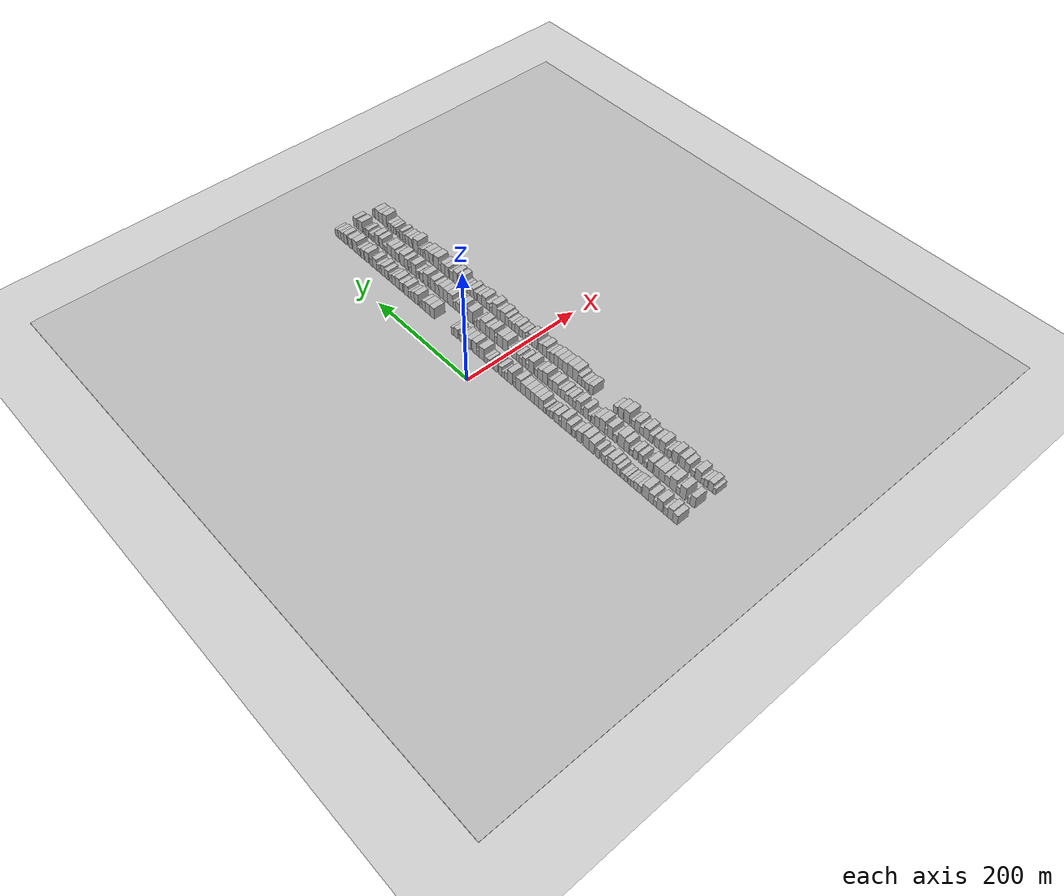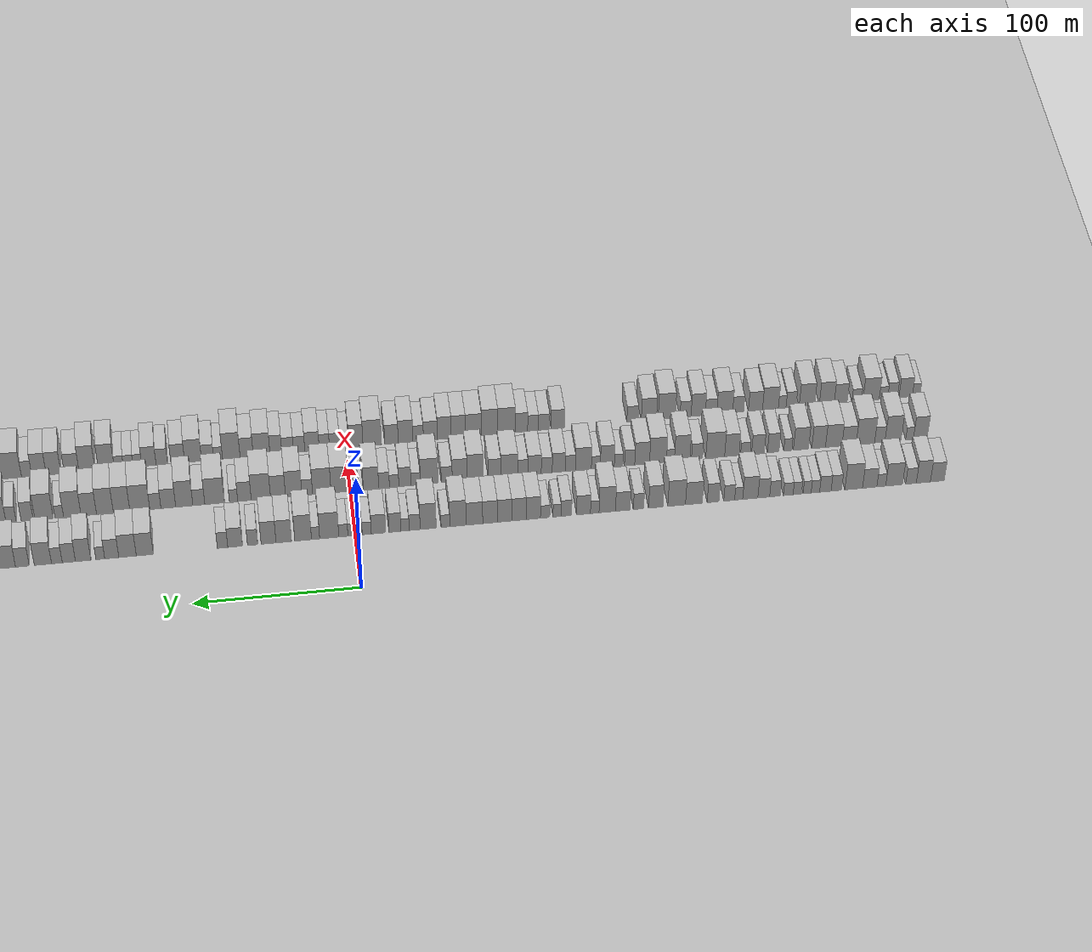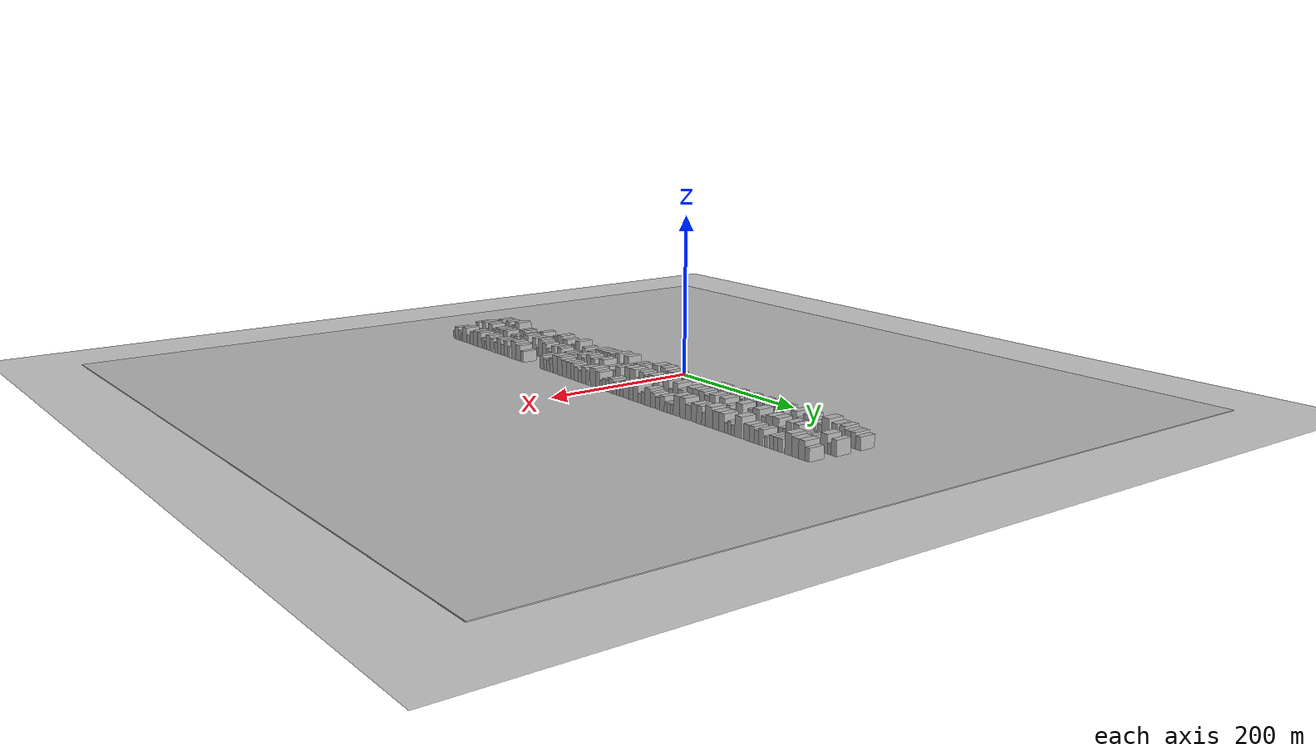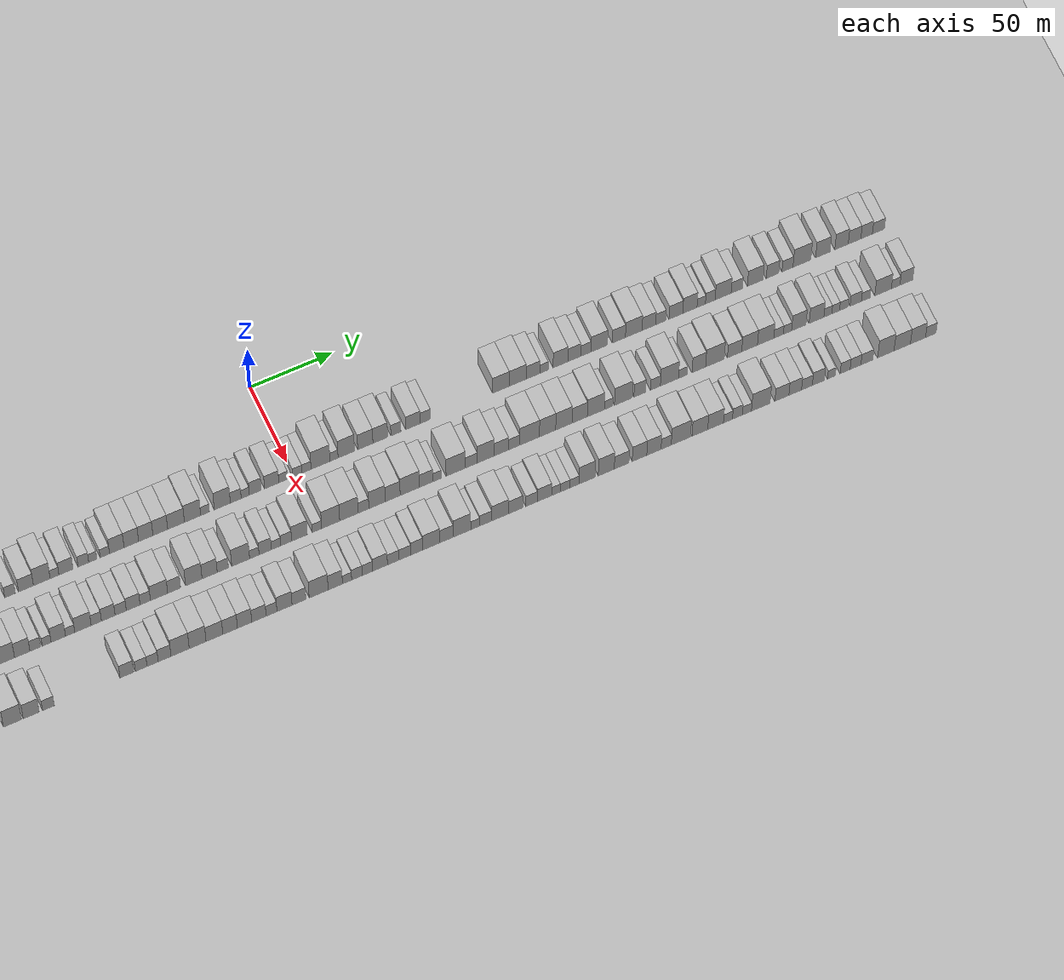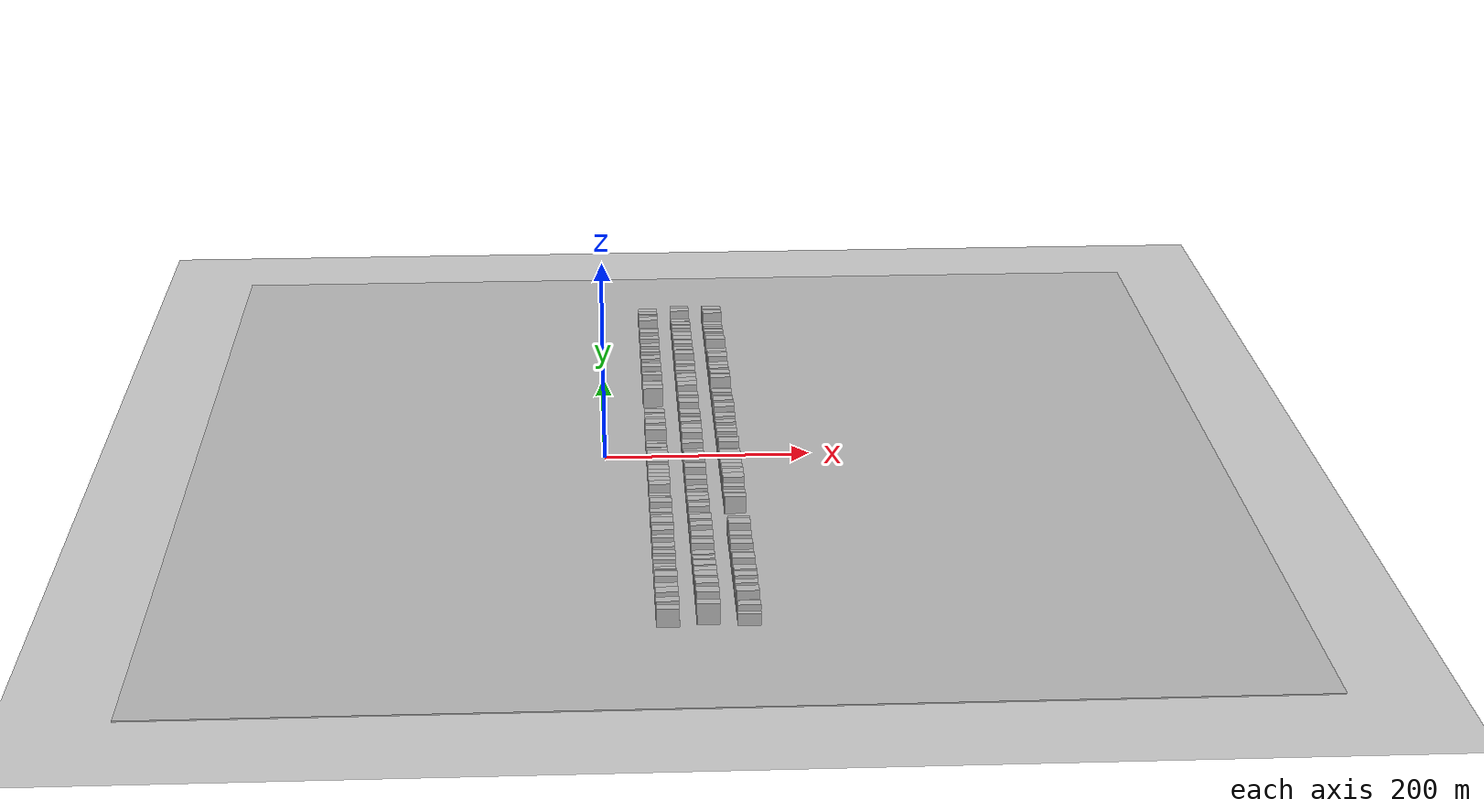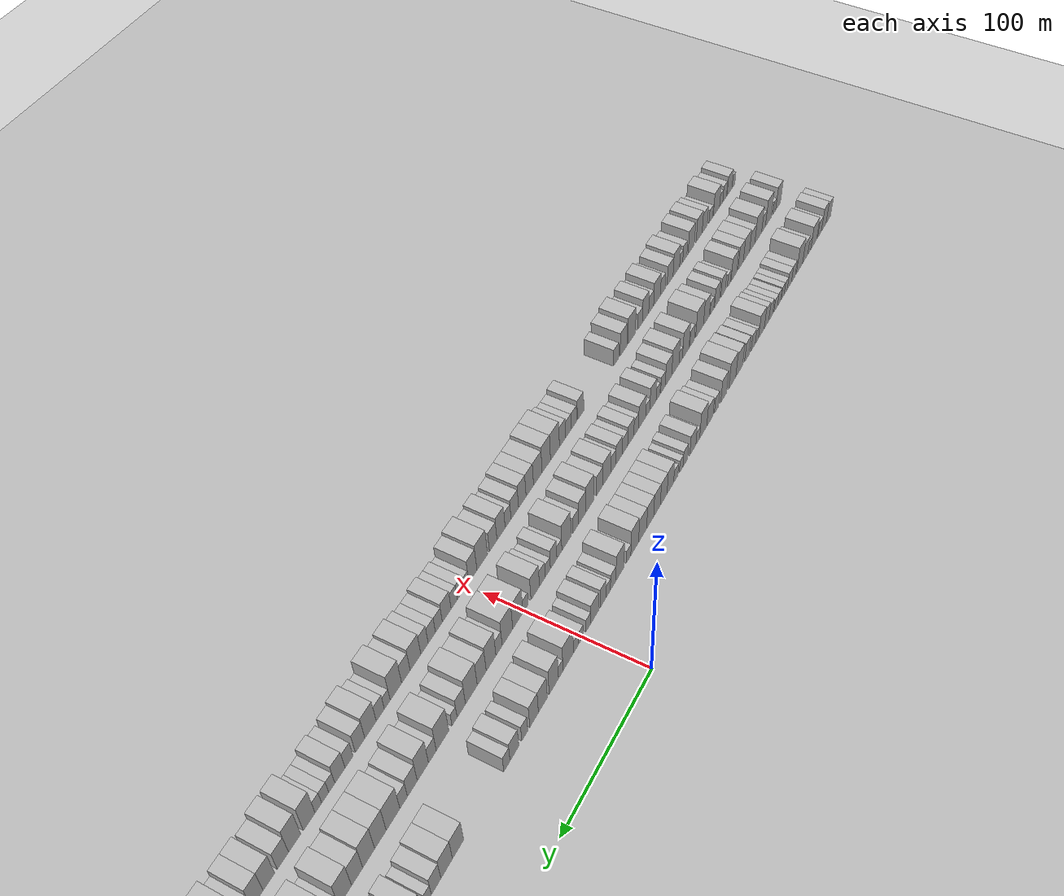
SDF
<?xml version="1.0" encoding="utf-8"?>

<sdf version="1.6">

   <world name="default">

      <gui fullscreen="0">

         <camera name="user_camera">

            <pose>-15 0 4.57585 0 0 0</pose>

            <view_controller>orbit</view_controller>

         </camera>

      </gui>

      <scene>

         <sky>

           <clouds>

             <speed>12</speed>

           </clouds>

         </sky>

         <ambient>0.4 0.4 0.4 1</ambient>

         <background>0.7 0.7 0.7 1</background>

         <shadows>1</shadows>

      </scene>

      <gravity>0 0 -9.8066</gravity>

      <magnetic_field>6e-06 2.3e-05 -4.2e-05</magnetic_field>

      <physics default="0" name="default_physics" type="ode">

         <ode>

            <solver>

               <type>quick</type>

               <iters>10</iters>

               <sor>1.0</sor>

               <use_dynamic_moi_rescaling>0</use_dynamic_moi_rescaling>

            </solver>

            <constraints>

               <cfm>0</cfm>

               <erp>0.2</erp>

               <contact_max_correcting_vel>100</contact_max_correcting_vel>

               <contact_surface_layer>0.001</contact_surface_layer>

            </constraints>

         </ode>

         <max_step_size>0.004</max_step_size>

         <real_time_factor>1</real_time_factor>

         <real_time_update_rate>250</real_time_update_rate>

      </physics>

      <light name="sun" type="directional">

         <cast_shadows>1</cast_shadows>

         <pose>0 0 10 0 0 0</pose>

         <diffuse>0.8 0.8 0.8 1</diffuse>

         <specular>0.2 0.2 0.2 1</specular>

         <attenuation>

            <range>1000</range>

            <constant>0.9</constant>

            <linear>0.01</linear>

            <quadratic>0.001</quadratic>

         </attenuation>

         <direction>-0.5 0.1 -0.9</direction>

      </light>

      <include>

         <name>ground_plane_1</name>

         <uri>model://HANNAS_ground_plane</uri>

         <pose>0 0 0  0 0 0</pose>

      </include>

      <include>

         <name>ground_plane_2</name>

         <uri>model://HANNAS_ground_plane</uri>

         <pose>100 0 0  0 0 0</pose>

      </include>

      <model name="building_1">

         <static>1</static>

         <pose frame="">50.0000 -355.7108 0 0.000000 0.000000 0.000000</pose>

         <link name="link">

            <pose frame="">0 0 9.00 0 0 0</pose>

            <collision name="collision">

               <geometry>

                  <box>

                     <size>20.0000 8.5783 18.0000</size>

                  </box>

               </geometry>

               <max_contacts>10</max_contacts>

               <surface>

                  <contact>

                     <ode/>

                  </contact>

                  <bounce/>

                  <friction>

                     <torsional>

                        <ode/>

                     </torsional>

                     <ode/>

                  </friction>

               </surface>

            </collision>

            <visual name="visual">

               <cast_shadows>0</cast_shadows>

               <geometry>

                  <box>

                     <size>20.0000 8.5783 18.0000</size>

                  </box>

               </geometry>

               <material>

                  <script>

                     <uri>model://HANNAS_wall/materials/scripts</uri>

                     <uri>model://HANNAS_wall/materials/textures</uri>

                     <name>vrc/HANNAS_wall</name>

                  </script>

               </material>

            </visual>

            <self_collide>0</self_collide>

            <enable_wind>0</enable_wind>

            <kinematic>0</kinematic>

         </link>

      </model>

      <model name="building_2">

         <static>1</static>

         <pose frame="">50.0000 -347.0402 0 0.000000 0.000000 0.000000</pose>

         <link name="link">

            <pose frame="">0 0 10.50 0 0 0</pose>

            <collision name="collision">

               <geometry>

                  <box>

                     <size>20.0000 8.7629 21.0000</size>

                  </box>

               </geometry>

               <max_contacts>10</max_contacts>

               <surface>

                  <contact>

                     <ode/>

                  </contact>

                  <bounce/>

                  <friction>

                     <torsional>

                        <ode/>

                     </torsional>

                     <ode/>

                  </friction>

               </surface>

            </collision>

            <visual name="visual">

               <cast_shadows>0</cast_shadows>

               <geometry>

                  <box>

                     <size>20.0000 8.7629 21.0000</size>

                  </box>

               </geometry>

               <material>

                  <script>

                     <uri>model://HANNAS_wall/materials/scripts</uri>

                     <uri>model://HANNAS_wall/materials/textures</uri>

                     <name>vrc/HANNAS_wall</name>

                  </script>

               </material>

            </visual>

            <self_collide>0</self_collide>

            <enable_wind>0</enable_wind>

            <kinematic>0</kinematic>

         </link>

      </model>

      <model name="building_3">

         <static>1</static>

         <pose frame="">50.0000 -339.3646 0 0.000000 0.000000 0.000000</pose>

         <link name="link">

            <pose frame="">0 0 7.50 0 0 0</pose>

            <collision name="collision">

               <geometry>

                  <box>

                     <size>20.0000 6.5883 15.0000</size>

                  </box>

               </geometry>

               <max_contacts>10</max_contacts>

               <surface>

                  <contact>

                     <ode/>

                  </contact>

                  <bounce/>

                  <friction>

                     <torsional>

                        <ode/>

                     </torsional>

                     <ode/>

                  </friction>

               </surface>

            </collision>

            <visual name="visual">

               <cast_shadows>0</cast_shadows>

               <geometry>

                  <box>

                     <size>20.0000 6.5883 15.0000</size>

                  </box>

               </geometry>

               <material>

                  <script>

                     <uri>model://HANNAS_wall/materials/scripts</uri>

                     <uri>model://HANNAS_wall/materials/textures</uri>

                     <name>vrc/HANNAS_wall</name>

                  </script>

               </material>

            </visual>

            <self_collide>0</self_collide>

            <enable_wind>0</enable_wind>

            <kinematic>0</kinematic>

         </link>

      </model>

      <model name="building_4">

         <static>1</static>

         <pose frame="">50.0000 -328.8616 0 0.000000 0.000000 0.000000</pose>

         <link name="link">

            <pose frame="">0 0 10.50 0 0 0</pose>

            <collision name="collision">

               <geometry>

                  <box>

                     <size>20.0000 10.4178 21.0000</size>

                  </box>

               </geometry>

               <max_contacts>10</max_contacts>

               <surface>

                  <contact>

                     <ode/>

                  </contact>

                  <bounce/>

                  <friction>

                     <torsional>

                        <ode/>

                     </torsional>

                     <ode/>

                  </friction>

               </surface>

            </collision>

            <visual name="visual">

               <cast_shadows>0</cast_shadows>

               <geometry>

                  <box>

                     <size>20.0000 10.4178 21.0000</size>

                  </box>

               </geometry>

               <material>

                  <script>

                     <uri>model://HANNAS_wall/materials/scripts</uri>

                     <uri>model://HANNAS_wall/materials/textures</uri>

                     <name>vrc/HANNAS_wall</name>

                  </script>

               </material>

            </visual>

            <self_collide>0</self_collide>

            <enable_wind>0</enable_wind>

            <kinematic>0</kinematic>

         </link>

      </model>

      <model name="building_5">

         <static>1</static>

         <pose frame="">50.0000 -320.9417 0 0.000000 0.000000 0.000000</pose>

         <link name="link">

            <pose frame="">0 0 6.00 0 0 0</pose>

            <collision name="collision">

               <geometry>

                  <box>

                     <size>20.0000 5.4220 12.0000</size>

                  </box>

               </geometry>

               <max_contacts>10</max_contacts>

               <surface>

                  <contact>

                     <ode/>

                  </contact>

                  <bounce/>

                  <friction>

                     <torsional>

                        <ode/>

                     </torsional>

                     <ode/>

                  </friction>

               </surface>

            </collision>

            <visual name="visual">

               <cast_shadows>0</cast_shadows>

               <geometry>

                  <box>

                     <size>20.0000 5.4220 12.0000</size>

                  </box>

               </geometry>

               <material>

                  <script>

                     <uri>model://HANNAS_wall/materials/scripts</uri>

                     <uri>model://HANNAS_wall/materials/textures</uri>

                     <name>vrc/HANNAS_wall</name>

                  </script>

               </material>

            </visual>

            <self_collide>0</self_collide>

            <enable_wind>0</enable_wind>

            <kinematic>0</kinematic>

         </link>

      </model>

      <model name="building_6">

         <static>1</static>

         <pose frame="">50.0000 -313.7510 0 0.000000 0.000000 0.000000</pose>

         <link name="link">

            <pose frame="">0 0 9.00 0 0 0</pose>

            <collision name="collision">

               <geometry>

                  <box>

                     <size>20.0000 8.9593 18.0000</size>

                  </box>

               </geometry>

               <max_contacts>10</max_contacts>

               <surface>

                  <contact>

                     <ode/>

                  </contact>

                  <bounce/>

                  <friction>

                     <torsional>

                        <ode/>

                     </torsional>

                     <ode/>

                  </friction>

               </surface>

            </collision>

            <visual name="visual">

               <cast_shadows>0</cast_shadows>

               <geometry>

                  <box>

                     <size>20.0000 8.9593 18.0000</size>

                  </box>

               </geometry>

               <material>

                  <script>

                     <uri>model://HANNAS_wall/materials/scripts</uri>

                     <uri>model://HANNAS_wall/materials/textures</uri>

                     <name>vrc/HANNAS_wall</name>

                  </script>

               </material>

            </visual>

            <self_collide>0</self_collide>

            <enable_wind>0</enable_wind>

            <kinematic>0</kinematic>

         </link>

      </model>

      <model name="building_7">

         <static>1</static>

         <pose frame="">50.0000 -303.7959 0 0.000000 0.000000 0.000000</pose>

         <link name="link">

            <pose frame="">0 0 12.00 0 0 0</pose>

            <collision name="collision">

               <geometry>

                  <box>

                     <size>20.0000 10.9510 24.0000</size>

                  </box>

               </geometry>

               <max_contacts>10</max_contacts>

               <surface>

                  <contact>

                     <ode/>

                  </contact>

                  <bounce/>

                  <friction>

                     <torsional>

                        <ode/>

                     </torsional>

                     <ode/>

                  </friction>

               </surface>

            </collision>

            <visual name="visual">

               <cast_shadows>0</cast_shadows>

               <geometry>

                  <box>

                     <size>20.0000 10.9510 24.0000</size>

                  </box>

               </geometry>

               <material>

                  <script>

                     <uri>model://HANNAS_wall/materials/scripts</uri>

                     <uri>model://HANNAS_wall/materials/textures</uri>

                     <name>vrc/HANNAS_wall</name>

                  </script>

               </material>

            </visual>

            <self_collide>0</self_collide>

            <enable_wind>0</enable_wind>

            <kinematic>0</kinematic>

         </link>

      </model>

      <model name="building_8">

         <static>1</static>

         <pose frame="">50.0000 -293.0944 0 0.000000 0.000000 0.000000</pose>

         <link name="link">

            <pose frame="">0 0 7.50 0 0 0</pose>

            <collision name="collision">

               <geometry>

                  <box>

                     <size>20.0000 6.4519 15.0000</size>

                  </box>

               </geometry>

               <max_contacts>10</max_contacts>

               <surface>

                  <contact>

                     <ode/>

                  </contact>

                  <bounce/>

                  <friction>

                     <torsional>

                        <ode/>

                     </torsional>

                     <ode/>

                  </friction>

               </surface>

            </collision>

            <visual name="visual">

               <cast_shadows>0</cast_shadows>

               <geometry>

                  <box>

                     <size>20.0000 6.4519 15.0000</size>

                  </box>

               </geometry>

               <material>

                  <script>

                     <uri>model://HANNAS_wall/materials/scripts</uri>

                     <uri>model://HANNAS_wall/materials/textures</uri>

                     <name>vrc/HANNAS_wall</name>

                  </script>

               </material>

            </visual>

            <self_collide>0</self_collide>

            <enable_wind>0</enable_wind>

            <kinematic>0</kinematic>

         </link>

      </model>

      <model name="building_9">

         <static>1</static>

         <pose frame="">50.0000 -286.3283 0 0.000000 0.000000 0.000000</pose>

         <link name="link">

            <pose frame="">0 0 7.50 0 0 0</pose>

            <collision name="collision">

               <geometry>

                  <box>

                     <size>20.0000 7.0803 15.0000</size>

                  </box>

               </geometry>

               <max_contacts>10</max_contacts>

               <surface>

                  <contact>

                     <ode/>

                  </contact>

                  <bounce/>

                  <friction>

                     <torsional>

                        <ode/>

                     </torsional>

                     <ode/>

                  </friction>

               </surface>

            </collision>

            <visual name="visual">

               <cast_shadows>0</cast_shadows>

               <geometry>

                  <box>

                     <size>20.0000 7.0803 15.0000</size>

                  </box>

               </geometry>

               <material>

                  <script>

                     <uri>model://HANNAS_wall/materials/scripts</uri>

                     <uri>model://HANNAS_wall/materials/textures</uri>

                     <name>vrc/HANNAS_wall</name>

                  </script>

               </material>

            </visual>

            <self_collide>0</self_collide>

            <enable_wind>0</enable_wind>

            <kinematic>0</kinematic>

         </link>

      </model>

      <model name="building_10">

         <static>1</static>

         <pose frame="">50.0000 -280.1579 0 0.000000 0.000000 0.000000</pose>

         <link name="link">

            <pose frame="">0 0 6.00 0 0 0</pose>

            <collision name="collision">

               <geometry>

                  <box>

                     <size>20.0000 5.2603 12.0000</size>

                  </box>

               </geometry>

               <max_contacts>10</max_contacts>

               <surface>

                  <contact>

                     <ode/>

                  </contact>

                  <bounce/>

                  <friction>

                     <torsional>

                        <ode/>

                     </torsional>

                     <ode/>

                  </friction>

               </surface>

            </collision>

            <visual name="visual">

               <cast_shadows>0</cast_shadows>

               <geometry>

                  <box>

                     <size>20.0000 5.2603 12.0000</size>

                  </box>

               </geometry>

               <material>

                  <script>

                     <uri>model://HANNAS_wall/materials/scripts</uri>

                     <uri>model://HANNAS_wall/materials/textures</uri>

                     <name>vrc/HANNAS_wall</name>

                  </script>

               </material>

            </visual>

            <self_collide>0</self_collide>

            <enable_wind>0</enable_wind>

            <kinematic>0</kinematic>

         </link>

      </model>

      <model name="building_11">

         <static>1</static>

         <pose frame="">50.0000 -275.0595 0 0.000000 0.000000 0.000000</pose>

         <link name="link">

            <pose frame="">0 0 6.00 0 0 0</pose>

            <collision name="collision">

               <geometry>

                  <box>

                     <size>20.0000 4.9366 12.0000</size>

                  </box>

               </geometry>

               <max_contacts>10</max_contacts>

               <surface>

                  <contact>

                     <ode/>

                  </contact>

                  <bounce/>

                  <friction>

                     <torsional>

                        <ode/>

                     </torsional>

                     <ode/>

                  </friction>

               </surface>

            </collision>

            <visual name="visual">

               <cast_shadows>0</cast_shadows>

               <geometry>

                  <box>

                     <size>20.0000 4.9366 12.0000</size>

                  </box>

               </geometry>

               <material>

                  <script>

                     <uri>model://HANNAS_wall/materials/scripts</uri>

                     <uri>model://HANNAS_wall/materials/textures</uri>

                     <name>vrc/HANNAS_wall</name>

                  </script>

               </material>

            </visual>

            <self_collide>0</self_collide>

            <enable_wind>0</enable_wind>

            <kinematic>0</kinematic>

         </link>

      </model>

      <model name="building_12">

         <static>1</static>

         <pose frame="">50.0000 -269.0004 0 0.000000 0.000000 0.000000</pose>

         <link name="link">

            <pose frame="">0 0 6.00 0 0 0</pose>

            <collision name="collision">

               <geometry>

                  <box>

                     <size>20.0000 5.1815 12.0000</size>

                  </box>

               </geometry>

               <max_contacts>10</max_contacts>

               <surface>

                  <contact>

                     <ode/>

                  </contact>

                  <bounce/>

                  <friction>

                     <torsional>

                        <ode/>

                     </torsional>

                     <ode/>

                  </friction>

               </surface>

            </collision>

            <visual name="visual">

               <cast_shadows>0</cast_shadows>

               <geometry>

                  <box>

                     <size>20.0000 5.1815 12.0000</size>

                  </box>

               </geometry>

               <material>

                  <script>

                     <uri>model://HANNAS_wall/materials/scripts</uri>

                     <uri>model://HANNAS_wall/materials/textures</uri>

                     <name>vrc/HANNAS_wall</name>

                  </script>

               </material>

            </visual>

            <self_collide>0</self_collide>

            <enable_wind>0</enable_wind>

            <kinematic>0</kinematic>

         </link>

      </model>

      <model name="building_13">

         <static>1</static>

         <pose frame="">50.0000 -263.4154 0 0.000000 0.000000 0.000000</pose>

         <link name="link">

            <pose frame="">0 0 6.00 0 0 0</pose>

            <collision name="collision">

               <geometry>

                  <box>

                     <size>20.0000 5.9884 12.0000</size>

                  </box>

               </geometry>

               <max_contacts>10</max_contacts>

               <surface>

                  <contact>

                     <ode/>

                  </contact>

                  <bounce/>

                  <friction>

                     <torsional>

                        <ode/>

                     </torsional>

                     <ode/>

                  </friction>

               </surface>

            </collision>

            <visual name="visual">

               <cast_shadows>0</cast_shadows>

               <geometry>

                  <box>

                     <size>20.0000 5.9884 12.0000</size>

                  </box>

               </geometry>

               <material>

                  <script>

                     <uri>model://HANNAS_wall/materials/scripts</uri>

                     <uri>model://HANNAS_wall/materials/textures</uri>

                     <name>vrc/HANNAS_wall</name>

                  </script>

               </material>

            </visual>

            <self_collide>0</self_collide>

            <enable_wind>0</enable_wind>

            <kinematic>0</kinematic>

         </link>

      </model>

      <model name="building_14">

         <static>1</static>

         <pose frame="">50.0000 -255.1728 0 0.000000 0.000000 0.000000</pose>

         <link name="link">

            <pose frame="">0 0 7.50 0 0 0</pose>

            <collision name="collision">

               <geometry>

                  <box>

                     <size>20.0000 6.4968 15.0000</size>

                  </box>

               </geometry>

               <max_contacts>10</max_contacts>

               <surface>

                  <contact>

                     <ode/>

                  </contact>

                  <bounce/>

                  <friction>

                     <torsional>

                        <ode/>

                     </torsional>

                     <ode/>

                  </friction>

               </surface>

            </collision>

            <visual name="visual">

               <cast_shadows>0</cast_shadows>

               <geometry>

                  <box>

                     <size>20.0000 6.4968 15.0000</size>

                  </box>

               </geometry>

               <material>

                  <script>

                     <uri>model://HANNAS_wall/materials/scripts</uri>

                     <uri>model://HANNAS_wall/materials/textures</uri>

                     <name>vrc/HANNAS_wall</name>

                  </script>

               </material>

            </visual>

            <self_collide>0</self_collide>

            <enable_wind>0</enable_wind>

            <kinematic>0</kinematic>

         </link>

      </model>

      <model name="building_15">

         <static>1</static>

         <pose frame="">50.0000 -248.3059 0 0.000000 0.000000 0.000000</pose>

         <link name="link">

            <pose frame="">0 0 9.00 0 0 0</pose>

            <collision name="collision">

               <geometry>

                  <box>

                     <size>20.0000 7.2370 18.0000</size>

                  </box>

               </geometry>

               <max_contacts>10</max_contacts>

               <surface>

                  <contact>

                     <ode/>

                  </contact>

                  <bounce/>

                  <friction>

                     <torsional>

                        <ode/>

                     </torsional>

                     <ode/>

                  </friction>

               </surface>

            </collision>

            <visual name="visual">

               <cast_shadows>0</cast_shadows>

               <geometry>

                  <box>

                     <size>20.0000 7.2370 18.0000</size>

                  </box>

               </geometry>

               <material>

                  <script>

                     <uri>model://HANNAS_wall/materials/scripts</uri>

                     <uri>model://HANNAS_wall/materials/textures</uri>

                     <name>vrc/HANNAS_wall</name>

                  </script>

               </material>

            </visual>

            <self_collide>0</self_collide>

            <enable_wind>0</enable_wind>

            <kinematic>0</kinematic>

         </link>

      </model>

      <model name="building_16">

         <static>1</static>

         <pose frame="">50.0000 -240.0128 0 0.000000 0.000000 0.000000</pose>

         <link name="link">

            <pose frame="">0 0 10.50 0 0 0</pose>

            <collision name="collision">

               <geometry>

                  <box>

                     <size>20.0000 9.3492 21.0000</size>

                  </box>

               </geometry>

               <max_contacts>10</max_contacts>

               <surface>

                  <contact>

                     <ode/>

                  </contact>

                  <bounce/>

                  <friction>

                     <torsional>

                        <ode/>

                     </torsional>

                     <ode/>

                  </friction>

               </surface>

            </collision>

            <visual name="visual">

               <cast_shadows>0</cast_shadows>

               <geometry>

                  <box>

                     <size>20.0000 9.3492 21.0000</size>

                  </box>

               </geometry>

               <material>

                  <script>

                     <uri>model://HANNAS_wall/materials/scripts</uri>

                     <uri>model://HANNAS_wall/materials/textures</uri>

                     <name>vrc/HANNAS_wall</name>

                  </script>

               </material>

            </visual>

            <self_collide>0</self_collide>

            <enable_wind>0</enable_wind>

            <kinematic>0</kinematic>

         </link>

      </model>

      <model name="building_17">

         <static>1</static>

         <pose frame="">50.0000 -232.8654 0 0.000000 0.000000 0.000000</pose>

         <link name="link">

            <pose frame="">0 0 6.00 0 0 0</pose>

            <collision name="collision">

               <geometry>

                  <box>

                     <size>20.0000 4.9455 12.0000</size>

                  </box>

               </geometry>

               <max_contacts>10</max_contacts>

               <surface>

                  <contact>

                     <ode/>

                  </contact>

                  <bounce/>

                  <friction>

                     <torsional>

                        <ode/>

                     </torsional>

                     <ode/>

                  </friction>

               </surface>

            </collision>

            <visual name="visual">

               <cast_shadows>0</cast_shadows>

               <geometry>

                  <box>

                     <size>20.0000 4.9455 12.0000</size>

                  </box>

               </geometry>

               <material>

                  <script>

                     <uri>model://HANNAS_wall/materials/scripts</uri>

                     <uri>model://HANNAS_wall/materials/textures</uri>

                     <name>vrc/HANNAS_wall</name>

                  </script>

               </material>

            </visual>

            <self_collide>0</self_collide>

            <enable_wind>0</enable_wind>

            <kinematic>0</kinematic>

         </link>

      </model>

      <model name="building_18">

         <static>1</static>

         <pose frame="">50.0000 -227.0547 0 0.000000 0.000000 0.000000</pose>

         <link name="link">

            <pose frame="">0 0 7.50 0 0 0</pose>

            <collision name="collision">

               <geometry>

                  <box>

                     <size>20.0000 6.6760 15.0000</size>

                  </box>

               </geometry>

               <max_contacts>10</max_contacts>

               <surface>

                  <contact>

                     <ode/>

                  </contact>

                  <bounce/>

                  <friction>

                     <torsional>

                        <ode/>

                     </torsional>

                     <ode/>

                  </friction>

               </surface>

            </collision>

            <visual name="visual">

               <cast_shadows>0</cast_shadows>

               <geometry>

                  <box>

                     <size>20.0000 6.6760 15.0000</size>

                  </box>

               </geometry>

               <material>

                  <script>

                     <uri>model://HANNAS_wall/materials/scripts</uri>

                     <uri>model://HANNAS_wall/materials/textures</uri>

                     <name>vrc/HANNAS_wall</name>

                  </script>

               </material>

            </visual>

            <self_collide>0</self_collide>

            <enable_wind>0</enable_wind>

            <kinematic>0</kinematic>

         </link>

      </model>

      <model name="building_19">

         <static>1</static>

         <pose frame="">50.0000 -217.1015 0 0.000000 0.000000 0.000000</pose>

         <link name="link">

            <pose frame="">0 0 9.00 0 0 0</pose>

            <collision name="collision">

               <geometry>

                  <box>

                     <size>20.0000 7.2303 18.0000</size>

                  </box>

               </geometry>

               <max_contacts>10</max_contacts>

               <surface>

                  <contact>

                     <ode/>

                  </contact>

                  <bounce/>

                  <friction>

                     <torsional>

                        <ode/>

                     </torsional>

                     <ode/>

                  </friction>

               </surface>

            </collision>

            <visual name="visual">

               <cast_shadows>0</cast_shadows>

               <geometry>

                  <box>

                     <size>20.0000 7.2303 18.0000</size>

                  </box>

               </geometry>

               <material>

                  <script>

                     <uri>model://HANNAS_wall/materials/scripts</uri>

                     <uri>model://HANNAS_wall/materials/textures</uri>

                     <name>vrc/HANNAS_wall</name>

                  </script>

               </material>

            </visual>

            <self_collide>0</self_collide>

            <enable_wind>0</enable_wind>

            <kinematic>0</kinematic>

         </link>

      </model>

      <model name="building_20">

         <static>1</static>

         <pose frame="">50.0000 -205.3397 0 0.000000 0.000000 0.000000</pose>

         <link name="link">

            <pose frame="">0 0 10.50 0 0 0</pose>

            <collision name="collision">

               <geometry>

                  <box>

                     <size>20.0000 10.2934 21.0000</size>

                  </box>

               </geometry>

               <max_contacts>10</max_contacts>

               <surface>

                  <contact>

                     <ode/>

                  </contact>

                  <bounce/>

                  <friction>

                     <torsional>

                        <ode/>

                     </torsional>

                     <ode/>

                  </friction>

               </surface>

            </collision>

            <visual name="visual">

               <cast_shadows>0</cast_shadows>

               <geometry>

                  <box>

                     <size>20.0000 10.2934 21.0000</size>

                  </box>

               </geometry>

               <material>

                  <script>

                     <uri>model://HANNAS_wall/materials/scripts</uri>

                     <uri>model://HANNAS_wall/materials/textures</uri>

                     <name>vrc/HANNAS_wall</name>

                  </script>

               </material>

            </visual>

            <self_collide>0</self_collide>

            <enable_wind>0</enable_wind>

            <kinematic>0</kinematic>

         </link>

      </model>

      <model name="building_21">

         <static>1</static>

         <pose frame="">50.0000 -194.7656 0 0.000000 0.000000 0.000000</pose>

         <link name="link">

            <pose frame="">0 0 12.00 0 0 0</pose>

            <collision name="collision">

               <geometry>

                  <box>

                     <size>20.0000 10.8548 24.0000</size>

                  </box>

               </geometry>

               <max_contacts>10</max_contacts>

               <surface>

                  <contact>

                     <ode/>

                  </contact>

                  <bounce/>

                  <friction>

                     <torsional>

                        <ode/>

                     </torsional>

                     <ode/>

                  </friction>

               </surface>

            </collision>

            <visual name="visual">

               <cast_shadows>0</cast_shadows>

               <geometry>

                  <box>

                     <size>20.0000 10.8548 24.0000</size>

                  </box>

               </geometry>

               <material>

                  <script>

                     <uri>model://HANNAS_wall/materials/scripts</uri>

                     <uri>model://HANNAS_wall/materials/textures</uri>

                     <name>vrc/HANNAS_wall</name>

                  </script>

               </material>

            </visual>

            <self_collide>0</self_collide>

            <enable_wind>0</enable_wind>

            <kinematic>0</kinematic>

         </link>

      </model>

      <model name="building_22">

         <static>1</static>

         <pose frame="">50.0000 -181.9417 0 0.000000 0.000000 0.000000</pose>

         <link name="link">

            <pose frame="">0 0 10.50 0 0 0</pose>

            <collision name="collision">

               <geometry>

                  <box>

                     <size>20.0000 8.7929 21.0000</size>

                  </box>

               </geometry>

               <max_contacts>10</max_contacts>

               <surface>

                  <contact>

                     <ode/>

                  </contact>

                  <bounce/>

                  <friction>

                     <torsional>

                        <ode/>

                     </torsional>

                     <ode/>

                  </friction>

               </surface>

            </collision>

            <visual name="visual">

               <cast_shadows>0</cast_shadows>

               <geometry>

                  <box>

                     <size>20.0000 8.7929 21.0000</size>

                  </box>

               </geometry>

               <material>

                  <script>

                     <uri>model://HANNAS_wall/materials/scripts</uri>

                     <uri>model://HANNAS_wall/materials/textures</uri>

                     <name>vrc/HANNAS_wall</name>

                  </script>

               </material>

            </visual>

            <self_collide>0</self_collide>

            <enable_wind>0</enable_wind>

            <kinematic>0</kinematic>

         </link>

      </model>

      <model name="building_23">

         <static>1</static>

         <pose frame="">50.0000 -171.4032 0 0.000000 0.000000 0.000000</pose>

         <link name="link">

            <pose frame="">0 0 7.50 0 0 0</pose>

            <collision name="collision">

               <geometry>

                  <box>

                     <size>20.0000 6.2841 15.0000</size>

                  </box>

               </geometry>

               <max_contacts>10</max_contacts>

               <surface>

                  <contact>

                     <ode/>

                  </contact>

                  <bounce/>

                  <friction>

                     <torsional>

                        <ode/>

                     </torsional>

                     <ode/>

                  </friction>

               </surface>

            </collision>

            <visual name="visual">

               <cast_shadows>0</cast_shadows>

               <geometry>

                  <box>

                     <size>20.0000 6.2841 15.0000</size>

                  </box>

               </geometry>

               <material>

                  <script>

                     <uri>model://HANNAS_wall/materials/scripts</uri>

                     <uri>model://HANNAS_wall/materials/textures</uri>

                     <name>vrc/HANNAS_wall</name>

                  </script>

               </material>

            </visual>

            <self_collide>0</self_collide>

            <enable_wind>0</enable_wind>

            <kinematic>0</kinematic>

         </link>

      </model>

      <model name="building_24">

         <static>1</static>

         <pose frame="">50.0000 -161.8031 0 0.000000 0.000000 0.000000</pose>

         <link name="link">

            <pose frame="">0 0 9.00 0 0 0</pose>

            <collision name="collision">

               <geometry>

                  <box>

                     <size>20.0000 8.9161 18.0000</size>

                  </box>

               </geometry>

               <max_contacts>10</max_contacts>

               <surface>

                  <contact>

                     <ode/>

                  </contact>

                  <bounce/>

                  <friction>

                     <torsional>

                        <ode/>

                     </torsional>

                     <ode/>

                  </friction>

               </surface>

            </collision>

            <visual name="visual">

               <cast_shadows>0</cast_shadows>

               <geometry>

                  <box>

                     <size>20.0000 8.9161 18.0000</size>

                  </box>

               </geometry>

               <material>

                  <script>

                     <uri>model://HANNAS_wall/materials/scripts</uri>

                     <uri>model://HANNAS_wall/materials/textures</uri>

                     <name>vrc/HANNAS_wall</name>

                  </script>

               </material>

            </visual>

            <self_collide>0</self_collide>

            <enable_wind>0</enable_wind>

            <kinematic>0</kinematic>

         </link>

      </model>

      <model name="building_25">

         <static>1</static>

         <pose frame="">50.0000 -152.3166 0 0.000000 0.000000 0.000000</pose>

         <link name="link">

            <pose frame="">0 0 12.00 0 0 0</pose>

            <collision name="collision">

               <geometry>

                  <box>

                     <size>20.0000 10.0570 24.0000</size>

                  </box>

               </geometry>

               <max_contacts>10</max_contacts>

               <surface>

                  <contact>

                     <ode/>

                  </contact>

                  <bounce/>

                  <friction>

                     <torsional>

                        <ode/>

                     </torsional>

                     <ode/>

                  </friction>

               </surface>

            </collision>

            <visual name="visual">

               <cast_shadows>0</cast_shadows>

               <geometry>

                  <box>

                     <size>20.0000 10.0570 24.0000</size>

                  </box>

               </geometry>

               <material>

                  <script>

                     <uri>model://HANNAS_wall/materials/scripts</uri>

                     <uri>model://HANNAS_wall/materials/textures</uri>

                     <name>vrc/HANNAS_wall</name>

                  </script>

               </material>

            </visual>

            <self_collide>0</self_collide>

            <enable_wind>0</enable_wind>

            <kinematic>0</kinematic>

         </link>

      </model>

      <model name="building_26">

         <static>1</static>

         <pose frame="">50.0000 -144.6645 0 0.000000 0.000000 0.000000</pose>

         <link name="link">

            <pose frame="">0 0 6.00 0 0 0</pose>

            <collision name="collision">

               <geometry>

                  <box>

                     <size>20.0000 5.2472 12.0000</size>

                  </box>

               </geometry>

               <max_contacts>10</max_contacts>

               <surface>

                  <contact>

                     <ode/>

                  </contact>

                  <bounce/>

                  <friction>

                     <torsional>

                        <ode/>

                     </torsional>

                     <ode/>

                  </friction>

               </surface>

            </collision>

            <visual name="visual">

               <cast_shadows>0</cast_shadows>

               <geometry>

                  <box>

                     <size>20.0000 5.2472 12.0000</size>

                  </box>

               </geometry>

               <material>

                  <script>

                     <uri>model://HANNAS_wall/materials/scripts</uri>

                     <uri>model://HANNAS_wall/materials/textures</uri>

                     <name>vrc/HANNAS_wall</name>

                  </script>

               </material>

            </visual>

            <self_collide>0</self_collide>

            <enable_wind>0</enable_wind>

            <kinematic>0</kinematic>

         </link>

      </model>

      <model name="building_27">

         <static>1</static>

         <pose frame="">50.0000 -137.7980 0 0.000000 0.000000 0.000000</pose>

         <link name="link">

            <pose frame="">0 0 9.00 0 0 0</pose>

            <collision name="collision">

               <geometry>

                  <box>

                     <size>20.0000 8.4859 18.0000</size>

                  </box>

               </geometry>

               <max_contacts>10</max_contacts>

               <surface>

                  <contact>

                     <ode/>

                  </contact>

                  <bounce/>

                  <friction>

                     <torsional>

                        <ode/>

                     </torsional>

                     <ode/>

                  </friction>

               </surface>

            </collision>

            <visual name="visual">

               <cast_shadows>0</cast_shadows>

               <geometry>

                  <box>

                     <size>20.0000 8.4859 18.0000</size>

                  </box>

               </geometry>

               <material>

                  <script>

                     <uri>model://HANNAS_wall/materials/scripts</uri>

                     <uri>model://HANNAS_wall/materials/textures</uri>

                     <name>vrc/HANNAS_wall</name>

                  </script>

               </material>

            </visual>

            <self_collide>0</self_collide>

            <enable_wind>0</enable_wind>

            <kinematic>0</kinematic>

         </link>

      </model>

      <model name="building_28">

         <static>1</static>

         <pose frame="">50.0000 -127.3299 0 0.000000 0.000000 0.000000</pose>

         <link name="link">

            <pose frame="">0 0 7.50 0 0 0</pose>

            <collision name="collision">

               <geometry>

                  <box>

                     <size>20.0000 6.4503 15.0000</size>

                  </box>

               </geometry>

               <max_contacts>10</max_contacts>

               <surface>

                  <contact>

                     <ode/>

                  </contact>

                  <bounce/>

                  <friction>

                     <torsional>

                        <ode/>

                     </torsional>

                     <ode/>

                  </friction>

               </surface>

            </collision>

            <visual name="visual">

               <cast_shadows>0</cast_shadows>

               <geometry>

                  <box>

                     <size>20.0000 6.4503 15.0000</size>

                  </box>

               </geometry>

               <material>

                  <script>

                     <uri>model://HANNAS_wall/materials/scripts</uri>

                     <uri>model://HANNAS_wall/materials/textures</uri>

                     <name>vrc/HANNAS_wall</name>

                  </script>

               </material>

            </visual>

            <self_collide>0</self_collide>

            <enable_wind>0</enable_wind>

            <kinematic>0</kinematic>

         </link>

      </model>

      <model name="building_29">

         <static>1</static>

         <pose frame="">50.0000 -121.6723 0 0.000000 0.000000 0.000000</pose>

         <link name="link">

            <pose frame="">0 0 6.00 0 0 0</pose>

            <collision name="collision">

               <geometry>

                  <box>

                     <size>20.0000 4.8649 12.0000</size>

                  </box>

               </geometry>

               <max_contacts>10</max_contacts>

               <surface>

                  <contact>

                     <ode/>

                  </contact>

                  <bounce/>

                  <friction>

                     <torsional>

                        <ode/>

                     </torsional>

                     <ode/>

                  </friction>

               </surface>

            </collision>

            <visual name="visual">

               <cast_shadows>0</cast_shadows>

               <geometry>

                  <box>

                     <size>20.0000 4.8649 12.0000</size>

                  </box>

               </geometry>

               <material>

                  <script>

                     <uri>model://HANNAS_wall/materials/scripts</uri>

                     <uri>model://HANNAS_wall/materials/textures</uri>

                     <name>vrc/HANNAS_wall</name>

                  </script>

               </material>

            </visual>

            <self_collide>0</self_collide>

            <enable_wind>0</enable_wind>

            <kinematic>0</kinematic>

         </link>

      </model>

      <model name="building_30">

         <static>1</static>

         <pose frame="">50.0000 -114.3965 0 0.000000 0.000000 0.000000</pose>

         <link name="link">

            <pose frame="">0 0 6.00 0 0 0</pose>

            <collision name="collision">

               <geometry>

                  <box>

                     <size>20.0000 5.6867 12.0000</size>

                  </box>

               </geometry>

               <max_contacts>10</max_contacts>

               <surface>

                  <contact>

                     <ode/>

                  </contact>

                  <bounce/>

                  <friction>

                     <torsional>

                        <ode/>

                     </torsional>

                     <ode/>

                  </friction>

               </surface>

            </collision>

            <visual name="visual">

               <cast_shadows>0</cast_shadows>

               <geometry>

                  <box>

                     <size>20.0000 5.6867 12.0000</size>

                  </box>

               </geometry>

               <material>

                  <script>

                     <uri>model://HANNAS_wall/materials/scripts</uri>

                     <uri>model://HANNAS_wall/materials/textures</uri>

                     <name>vrc/HANNAS_wall</name>

                  </script>

               </material>

            </visual>

            <self_collide>0</self_collide>

            <enable_wind>0</enable_wind>

            <kinematic>0</kinematic>

         </link>

      </model>

      <model name="building_31">

         <static>1</static>

         <pose frame="">50.0000 -107.1871 0 0.000000 0.000000 0.000000</pose>

         <link name="link">

            <pose frame="">0 0 10.50 0 0 0</pose>

            <collision name="collision">

               <geometry>

                  <box>

                     <size>20.0000 8.7320 21.0000</size>

                  </box>

               </geometry>

               <max_contacts>10</max_contacts>

               <surface>

                  <contact>

                     <ode/>

                  </contact>

                  <bounce/>

                  <friction>

                     <torsional>

                        <ode/>

                     </torsional>

                     <ode/>

                  </friction>

               </surface>

            </collision>

            <visual name="visual">

               <cast_shadows>0</cast_shadows>

               <geometry>

                  <box>

                     <size>20.0000 8.7320 21.0000</size>

                  </box>

               </geometry>

               <material>

                  <script>

                     <uri>model://HANNAS_wall/materials/scripts</uri>

                     <uri>model://HANNAS_wall/materials/textures</uri>

                     <name>vrc/HANNAS_wall</name>

                  </script>

               </material>

            </visual>

            <self_collide>0</self_collide>

            <enable_wind>0</enable_wind>

            <kinematic>0</kinematic>

         </link>

      </model>

      <model name="building_32">

         <static>1</static>

         <pose frame="">50.0000 -98.4116 0 0.000000 0.000000 0.000000</pose>

         <link name="link">

            <pose frame="">0 0 10.50 0 0 0</pose>

            <collision name="collision">

               <geometry>

                  <box>

                     <size>20.0000 8.8189 21.0000</size>

                  </box>

               </geometry>

               <max_contacts>10</max_contacts>

               <surface>

                  <contact>

                     <ode/>

                  </contact>

                  <bounce/>

                  <friction>

                     <torsional>

                        <ode/>

                     </torsional>

                     <ode/>

                  </friction>

               </surface>

            </collision>

            <visual name="visual">

               <cast_shadows>0</cast_shadows>

               <geometry>

                  <box>

                     <size>20.0000 8.8189 21.0000</size>

                  </box>

               </geometry>

               <material>

                  <script>

                     <uri>model://HANNAS_wall/materials/scripts</uri>

                     <uri>model://HANNAS_wall/materials/textures</uri>

                     <name>vrc/HANNAS_wall</name>

                  </script>

               </material>

            </visual>

            <self_collide>0</self_collide>

            <enable_wind>0</enable_wind>

            <kinematic>0</kinematic>

         </link>

      </model>

      <model name="building_33">

         <static>1</static>

         <pose frame="">50.0000 -89.6995 0 0.000000 0.000000 0.000000</pose>

         <link name="link">

            <pose frame="">0 0 10.50 0 0 0</pose>

            <collision name="collision">

               <geometry>

                  <box>

                     <size>20.0000 8.6054 21.0000</size>

                  </box>

               </geometry>

               <max_contacts>10</max_contacts>

               <surface>

                  <contact>

                     <ode/>

                  </contact>

                  <bounce/>

                  <friction>

                     <torsional>

                        <ode/>

                     </torsional>

                     <ode/>

                  </friction>

               </surface>

            </collision>

            <visual name="visual">

               <cast_shadows>0</cast_shadows>

               <geometry>

                  <box>

                     <size>20.0000 8.6054 21.0000</size>

                  </box>

               </geometry>

               <material>

                  <script>

                     <uri>model://HANNAS_wall/materials/scripts</uri>

                     <uri>model://HANNAS_wall/materials/textures</uri>

                     <name>vrc/HANNAS_wall</name>

                  </script>

               </material>

            </visual>

            <self_collide>0</self_collide>

            <enable_wind>0</enable_wind>

            <kinematic>0</kinematic>

         </link>

      </model>

      <model name="building_34">

         <static>1</static>

         <pose frame="">50.0000 -80.9385 0 0.000000 0.000000 0.000000</pose>

         <link name="link">

            <pose frame="">0 0 10.50 0 0 0</pose>

            <collision name="collision">

               <geometry>

                  <box>

                     <size>20.0000 8.9166 21.0000</size>

                  </box>

               </geometry>

               <max_contacts>10</max_contacts>

               <surface>

                  <contact>

                     <ode/>

                  </contact>

                  <bounce/>

                  <friction>

                     <torsional>

                        <ode/>

                     </torsional>

                     <ode/>

                  </friction>

               </surface>

            </collision>

            <visual name="visual">

               <cast_shadows>0</cast_shadows>

               <geometry>

                  <box>

                     <size>20.0000 8.9166 21.0000</size>

                  </box>

               </geometry>

               <material>

                  <script>

                     <uri>model://HANNAS_wall/materials/scripts</uri>

                     <uri>model://HANNAS_wall/materials/textures</uri>

                     <name>vrc/HANNAS_wall</name>

                  </script>

               </material>

            </visual>

            <self_collide>0</self_collide>

            <enable_wind>0</enable_wind>

            <kinematic>0</kinematic>

         </link>

      </model>

      <model name="building_35">

         <static>1</static>

         <pose frame="">50.0000 -71.4100 0 0.000000 0.000000 0.000000</pose>

         <link name="link">

            <pose frame="">0 0 10.50 0 0 0</pose>

            <collision name="collision">

               <geometry>

                  <box>

                     <size>20.0000 10.1404 21.0000</size>

                  </box>

               </geometry>

               <max_contacts>10</max_contacts>

               <surface>

                  <contact>

                     <ode/>

                  </contact>

                  <bounce/>

                  <friction>

                     <torsional>

                        <ode/>

                     </torsional>

                     <ode/>

                  </friction>

               </surface>

            </collision>

            <visual name="visual">

               <cast_shadows>0</cast_shadows>

               <geometry>

                  <box>

                     <size>20.0000 10.1404 21.0000</size>

                  </box>

               </geometry>

               <material>

                  <script>

                     <uri>model://HANNAS_wall/materials/scripts</uri>

                     <uri>model://HANNAS_wall/materials/textures</uri>

                     <name>vrc/HANNAS_wall</name>

                  </script>

               </material>

            </visual>

            <self_collide>0</self_collide>

            <enable_wind>0</enable_wind>

            <kinematic>0</kinematic>

         </link>

      </model>

      <model name="building_36">

         <static>1</static>

         <pose frame="">50.0000 -61.4313 0 0.000000 0.000000 0.000000</pose>

         <link name="link">

            <pose frame="">0 0 12.00 0 0 0</pose>

            <collision name="collision">

               <geometry>

                  <box>

                     <size>20.0000 9.8170 24.0000</size>

                  </box>

               </geometry>

               <max_contacts>10</max_contacts>

               <surface>

                  <contact>

                     <ode/>

                  </contact>

                  <bounce/>

                  <friction>

                     <torsional>

                        <ode/>

                     </torsional>

                     <ode/>

                  </friction>

               </surface>

            </collision>

            <visual name="visual">

               <cast_shadows>0</cast_shadows>

               <geometry>

                  <box>

                     <size>20.0000 9.8170 24.0000</size>

                  </box>

               </geometry>

               <material>

                  <script>

                     <uri>model://HANNAS_wall/materials/scripts</uri>

                     <uri>model://HANNAS_wall/materials/textures</uri>

                     <name>vrc/HANNAS_wall</name>

                  </script>

               </material>

            </visual>

            <self_collide>0</self_collide>

            <enable_wind>0</enable_wind>

            <kinematic>0</kinematic>

         </link>

      </model>

      <model name="building_37">

         <static>1</static>

         <pose frame="">50.0000 -53.8903 0 0.000000 0.000000 0.000000</pose>

         <link name="link">

            <pose frame="">0 0 6.00 0 0 0</pose>

            <collision name="collision">

               <geometry>

                  <box>

                     <size>20.0000 5.2652 12.0000</size>

                  </box>

               </geometry>

               <max_contacts>10</max_contacts>

               <surface>

                  <contact>

                     <ode/>

                  </contact>

                  <bounce/>

                  <friction>

                     <torsional>

                        <ode/>

                     </torsional>

                     <ode/>

                  </friction>

               </surface>

            </collision>

            <visual name="visual">

               <cast_shadows>0</cast_shadows>

               <geometry>

                  <box>

                     <size>20.0000 5.2652 12.0000</size>

                  </box>

               </geometry>

               <material>

                  <script>

                     <uri>model://HANNAS_wall/materials/scripts</uri>

                     <uri>model://HANNAS_wall/materials/textures</uri>

                     <name>vrc/HANNAS_wall</name>

                  </script>

               </material>

            </visual>

            <self_collide>0</self_collide>

            <enable_wind>0</enable_wind>

            <kinematic>0</kinematic>

         </link>

      </model>

      <model name="building_38">

         <static>1</static>

         <pose frame="">50.0000 -43.4119 0 0.000000 0.000000 0.000000</pose>

         <link name="link">

            <pose frame="">0 0 12.00 0 0 0</pose>

            <collision name="collision">

               <geometry>

                  <box>

                     <size>20.0000 9.6916 24.0000</size>

                  </box>

               </geometry>

               <max_contacts>10</max_contacts>

               <surface>

                  <contact>

                     <ode/>

                  </contact>

                  <bounce/>

                  <friction>

                     <torsional>

                        <ode/>

                     </torsional>

                     <ode/>

                  </friction>

               </surface>

            </collision>

            <visual name="visual">

               <cast_shadows>0</cast_shadows>

               <geometry>

                  <box>

                     <size>20.0000 9.6916 24.0000</size>

                  </box>

               </geometry>

               <material>

                  <script>

                     <uri>model://HANNAS_wall/materials/scripts</uri>

                     <uri>model://HANNAS_wall/materials/textures</uri>

                     <name>vrc/HANNAS_wall</name>

                  </script>

               </material>

            </visual>

            <self_collide>0</self_collide>

            <enable_wind>0</enable_wind>

            <kinematic>0</kinematic>

         </link>

      </model>

      <model name="building_39">

         <static>1</static>

         <pose frame="">50.0000 -35.2519 0 0.000000 0.000000 0.000000</pose>

         <link name="link">

            <pose frame="">0 0 7.50 0 0 0</pose>

            <collision name="collision">

               <geometry>

                  <box>

                     <size>20.0000 6.6284 15.0000</size>

                  </box>

               </geometry>

               <max_contacts>10</max_contacts>

               <surface>

                  <contact>

                     <ode/>

                  </contact>

                  <bounce/>

                  <friction>

                     <torsional>

                        <ode/>

                     </torsional>

                     <ode/>

                  </friction>

               </surface>

            </collision>

            <visual name="visual">

               <cast_shadows>0</cast_shadows>

               <geometry>

                  <box>

                     <size>20.0000 6.6284 15.0000</size>

                  </box>

               </geometry>

               <material>

                  <script>

                     <uri>model://HANNAS_wall/materials/scripts</uri>

                     <uri>model://HANNAS_wall/materials/textures</uri>

                     <name>vrc/HANNAS_wall</name>

                  </script>

               </material>

            </visual>

            <self_collide>0</self_collide>

            <enable_wind>0</enable_wind>

            <kinematic>0</kinematic>

         </link>

      </model>

      <model name="building_40">

         <static>1</static>

         <pose frame="">50.0000 -29.4817 0 0.000000 0.000000 0.000000</pose>

         <link name="link">

            <pose frame="">0 0 6.00 0 0 0</pose>

            <collision name="collision">

               <geometry>

                  <box>

                     <size>20.0000 4.9120 12.0000</size>

                  </box>

               </geometry>

               <max_contacts>10</max_contacts>

               <surface>

                  <contact>

                     <ode/>

                  </contact>

                  <bounce/>

                  <friction>

                     <torsional>

                        <ode/>

                     </torsional>

                     <ode/>

                  </friction>

               </surface>

            </collision>

            <visual name="visual">

               <cast_shadows>0</cast_shadows>

               <geometry>

                  <box>

                     <size>20.0000 4.9120 12.0000</size>

                  </box>

               </geometry>

               <material>

                  <script>

                     <uri>model://HANNAS_wall/materials/scripts</uri>

                     <uri>model://HANNAS_wall/materials/textures</uri>

                     <name>vrc/HANNAS_wall</name>

                  </script>

               </material>

            </visual>

            <self_collide>0</self_collide>

            <enable_wind>0</enable_wind>

            <kinematic>0</kinematic>

         </link>

      </model>

      <model name="building_41">

         <static>1</static>

         <pose frame="">50.0000 -23.4032 0 0.000000 0.000000 0.000000</pose>

         <link name="link">

            <pose frame="">0 0 9.00 0 0 0</pose>

            <collision name="collision">

               <geometry>

                  <box>

                     <size>20.0000 7.2448 18.0000</size>

                  </box>

               </geometry>

               <max_contacts>10</max_contacts>

               <surface>

                  <contact>

                     <ode/>

                  </contact>

                  <bounce/>

                  <friction>

                     <torsional>

                        <ode/>

                     </torsional>

                     <ode/>

                  </friction>

               </surface>

            </collision>

            <visual name="visual">

               <cast_shadows>0</cast_shadows>

               <geometry>

                  <box>

                     <size>20.0000 7.2448 18.0000</size>

                  </box>

               </geometry>

               <material>

                  <script>

                     <uri>model://HANNAS_wall/materials/scripts</uri>

                     <uri>model://HANNAS_wall/materials/textures</uri>

                     <name>vrc/HANNAS_wall</name>

                  </script>

               </material>

            </visual>

            <self_collide>0</self_collide>

            <enable_wind>0</enable_wind>

            <kinematic>0</kinematic>

         </link>

      </model>

      <model name="building_42">

         <static>1</static>

         <pose frame="">50.0000 -13.4413 0 0.000000 0.000000 0.000000</pose>

         <link name="link">

            <pose frame="">0 0 9.00 0 0 0</pose>

            <collision name="collision">

               <geometry>

                  <box>

                     <size>20.0000 8.6791 18.0000</size>

                  </box>

               </geometry>

               <max_contacts>10</max_contacts>

               <surface>

                  <contact>

                     <ode/>

                  </contact>

                  <bounce/>

                  <friction>

                     <torsional>

                        <ode/>

                     </torsional>

                     <ode/>

                  </friction>

               </surface>

            </collision>

            <visual name="visual">

               <cast_shadows>0</cast_shadows>

               <geometry>

                  <box>

                     <size>20.0000 8.6791 18.0000</size>

                  </box>

               </geometry>

               <material>

                  <script>

                     <uri>model://HANNAS_wall/materials/scripts</uri>

                     <uri>model://HANNAS_wall/materials/textures</uri>

                     <name>vrc/HANNAS_wall</name>

                  </script>

               </material>

            </visual>

            <self_collide>0</self_collide>

            <enable_wind>0</enable_wind>

            <kinematic>0</kinematic>

         </link>

      </model>

      <model name="building_43">

         <static>1</static>

         <pose frame="">50.0000 -6.3569 0 0.000000 0.000000 0.000000</pose>

         <link name="link">

            <pose frame="">0 0 6.00 0 0 0</pose>

            <collision name="collision">

               <geometry>

                  <box>

                     <size>20.0000 5.4895 12.0000</size>

                  </box>

               </geometry>

               <max_contacts>10</max_contacts>

               <surface>

                  <contact>

                     <ode/>

                  </contact>

                  <bounce/>

                  <friction>

                     <torsional>

                        <ode/>

                     </torsional>

                     <ode/>

                  </friction>

               </surface>

            </collision>

            <visual name="visual">

               <cast_shadows>0</cast_shadows>

               <geometry>

                  <box>

                     <size>20.0000 5.4895 12.0000</size>

                  </box>

               </geometry>

               <material>

                  <script>

                     <uri>model://HANNAS_wall/materials/scripts</uri>

                     <uri>model://HANNAS_wall/materials/textures</uri>

                     <name>vrc/HANNAS_wall</name>

                  </script>

               </material>

            </visual>

            <self_collide>0</self_collide>

            <enable_wind>0</enable_wind>

            <kinematic>0</kinematic>

         </link>

      </model>

      <model name="building_44">

         <static>1</static>

         <pose frame="">50.0000 2.2003 0 0.000000 0.000000 0.000000</pose>

         <link name="link">

            <pose frame="">0 0 6.00 0 0 0</pose>

            <collision name="collision">

               <geometry>

                  <box>

                     <size>20.0000 5.6250 12.0000</size>

                  </box>

               </geometry>

               <max_contacts>10</max_contacts>

               <surface>

                  <contact>

                     <ode/>

                  </contact>

                  <bounce/>

                  <friction>

                     <torsional>

                        <ode/>

                     </torsional>

                     <ode/>

                  </friction>

               </surface>

            </collision>

            <visual name="visual">

               <cast_shadows>0</cast_shadows>

               <geometry>

                  <box>

                     <size>20.0000 5.6250 12.0000</size>

                  </box>

               </geometry>

               <material>

                  <script>

                     <uri>model://HANNAS_wall/materials/scripts</uri>

                     <uri>model://HANNAS_wall/materials/textures</uri>

                     <name>vrc/HANNAS_wall</name>

                  </script>

               </material>

            </visual>

            <self_collide>0</self_collide>

            <enable_wind>0</enable_wind>

            <kinematic>0</kinematic>

         </link>

      </model>

      <model name="building_45">

         <static>1</static>

         <pose frame="">50.0000 7.7510 0 0.000000 0.000000 0.000000</pose>

         <link name="link">

            <pose frame="">0 0 6.00 0 0 0</pose>

            <collision name="collision">

               <geometry>

                  <box>

                     <size>20.0000 5.4763 12.0000</size>

                  </box>

               </geometry>

               <max_contacts>10</max_contacts>

               <surface>

                  <contact>

                     <ode/>

                  </contact>

                  <bounce/>

                  <friction>

                     <torsional>

                        <ode/>

                     </torsional>

                     <ode/>

                  </friction>

               </surface>

            </collision>

            <visual name="visual">

               <cast_shadows>0</cast_shadows>

               <geometry>

                  <box>

                     <size>20.0000 5.4763 12.0000</size>

                  </box>

               </geometry>

               <material>

                  <script>

                     <uri>model://HANNAS_wall/materials/scripts</uri>

                     <uri>model://HANNAS_wall/materials/textures</uri>

                     <name>vrc/HANNAS_wall</name>

                  </script>

               </material>

            </visual>

            <self_collide>0</self_collide>

            <enable_wind>0</enable_wind>

            <kinematic>0</kinematic>

         </link>

      </model>

      <model name="building_46">

         <static>1</static>

         <pose frame="">50.0000 16.2468 0 0.000000 0.000000 0.000000</pose>

         <link name="link">

            <pose frame="">0 0 12.00 0 0 0</pose>

            <collision name="collision">

               <geometry>

                  <box>

                     <size>20.0000 11.5153 24.0000</size>

                  </box>

               </geometry>

               <max_contacts>10</max_contacts>

               <surface>

                  <contact>

                     <ode/>

                  </contact>

                  <bounce/>

                  <friction>

                     <torsional>

                        <ode/>

                     </torsional>

                     <ode/>

                  </friction>

               </surface>

            </collision>

            <visual name="visual">

               <cast_shadows>0</cast_shadows>

               <geometry>

                  <box>

                     <size>20.0000 11.5153 24.0000</size>

                  </box>

               </geometry>

               <material>

                  <script>

                     <uri>model://HANNAS_wall/materials/scripts</uri>

                     <uri>model://HANNAS_wall/materials/textures</uri>

                     <name>vrc/HANNAS_wall</name>

                  </script>

               </material>

            </visual>

            <self_collide>0</self_collide>

            <enable_wind>0</enable_wind>

            <kinematic>0</kinematic>

         </link>

      </model>

      <model name="building_47">

         <static>1</static>

         <pose frame="">50.0000 24.4752 0 0.000000 0.000000 0.000000</pose>

         <link name="link">

            <pose frame="">0 0 6.00 0 0 0</pose>

            <collision name="collision">

               <geometry>

                  <box>

                     <size>20.0000 4.9416 12.0000</size>

                  </box>

               </geometry>

               <max_contacts>10</max_contacts>

               <surface>

                  <contact>

                     <ode/>

                  </contact>

                  <bounce/>

                  <friction>

                     <torsional>

                        <ode/>

                     </torsional>

                     <ode/>

                  </friction>

               </surface>

            </collision>

            <visual name="visual">

               <cast_shadows>0</cast_shadows>

               <geometry>

                  <box>

                     <size>20.0000 4.9416 12.0000</size>

                  </box>

               </geometry>

               <material>

                  <script>

                     <uri>model://HANNAS_wall/materials/scripts</uri>

                     <uri>model://HANNAS_wall/materials/textures</uri>

                     <name>vrc/HANNAS_wall</name>

                  </script>

               </material>

            </visual>

            <self_collide>0</self_collide>

            <enable_wind>0</enable_wind>

            <kinematic>0</kinematic>

         </link>

      </model>

      <model name="building_48">

         <static>1</static>

         <pose frame="">50.0000 31.9420 0 0.000000 0.000000 0.000000</pose>

         <link name="link">

            <pose frame="">0 0 12.00 0 0 0</pose>

            <collision name="collision">

               <geometry>

                  <box>

                     <size>20.0000 9.9919 24.0000</size>

                  </box>

               </geometry>

               <max_contacts>10</max_contacts>

               <surface>

                  <contact>

                     <ode/>

                  </contact>

                  <bounce/>

                  <friction>

                     <torsional>

                        <ode/>

                     </torsional>

                     <ode/>

                  </friction>

               </surface>

            </collision>

            <visual name="visual">

               <cast_shadows>0</cast_shadows>

               <geometry>

                  <box>

                     <size>20.0000 9.9919 24.0000</size>

                  </box>

               </geometry>

               <material>

                  <script>

                     <uri>model://HANNAS_wall/materials/scripts</uri>

                     <uri>model://HANNAS_wall/materials/textures</uri>

                     <name>vrc/HANNAS_wall</name>

                  </script>

               </material>

            </visual>

            <self_collide>0</self_collide>

            <enable_wind>0</enable_wind>

            <kinematic>0</kinematic>

         </link>

      </model>

      <model name="building_49">

         <static>1</static>

         <pose frame="">50.0000 43.5863 0 0.000000 0.000000 0.000000</pose>

         <link name="link">

            <pose frame="">0 0 10.50 0 0 0</pose>

            <collision name="collision">

               <geometry>

                  <box>

                     <size>20.0000 9.2966 21.0000</size>

                  </box>

               </geometry>

               <max_contacts>10</max_contacts>

               <surface>

                  <contact>

                     <ode/>

                  </contact>

                  <bounce/>

                  <friction>

                     <torsional>

                        <ode/>

                     </torsional>

                     <ode/>

                  </friction>

               </surface>

            </collision>

            <visual name="visual">

               <cast_shadows>0</cast_shadows>

               <geometry>

                  <box>

                     <size>20.0000 9.2966 21.0000</size>

                  </box>

               </geometry>

               <material>

                  <script>

                     <uri>model://HANNAS_wall/materials/scripts</uri>

                     <uri>model://HANNAS_wall/materials/textures</uri>

                     <name>vrc/HANNAS_wall</name>

                  </script>

               </material>

            </visual>

            <self_collide>0</self_collide>

            <enable_wind>0</enable_wind>

            <kinematic>0</kinematic>

         </link>

      </model>

      <model name="building_50">

         <static>1</static>

         <pose frame="">50.0000 52.7178 0 0.000000 0.000000 0.000000</pose>

         <link name="link">

            <pose frame="">0 0 10.50 0 0 0</pose>

            <collision name="collision">

               <geometry>

                  <box>

                     <size>20.0000 8.9664 21.0000</size>

                  </box>

               </geometry>

               <max_contacts>10</max_contacts>

               <surface>

                  <contact>

                     <ode/>

                  </contact>

                  <bounce/>

                  <friction>

                     <torsional>

                        <ode/>

                     </torsional>

                     <ode/>

                  </friction>

               </surface>

            </collision>

            <visual name="visual">

               <cast_shadows>0</cast_shadows>

               <geometry>

                  <box>

                     <size>20.0000 8.9664 21.0000</size>

                  </box>

               </geometry>

               <material>

                  <script>

                     <uri>model://HANNAS_wall/materials/scripts</uri>

                     <uri>model://HANNAS_wall/materials/textures</uri>

                     <name>vrc/HANNAS_wall</name>

                  </script>

               </material>

            </visual>

            <self_collide>0</self_collide>

            <enable_wind>0</enable_wind>

            <kinematic>0</kinematic>

         </link>

      </model>

      <model name="building_51">

         <static>1</static>

         <pose frame="">50.0000 62.2641 0 0.000000 0.000000 0.000000</pose>

         <link name="link">

            <pose frame="">0 0 7.50 0 0 0</pose>

            <collision name="collision">

               <geometry>

                  <box>

                     <size>20.0000 6.1261 15.0000</size>

                  </box>

               </geometry>

               <max_contacts>10</max_contacts>

               <surface>

                  <contact>

                     <ode/>

                  </contact>

                  <bounce/>

                  <friction>

                     <torsional>

                        <ode/>

                     </torsional>

                     <ode/>

                  </friction>

               </surface>

            </collision>

            <visual name="visual">

               <cast_shadows>0</cast_shadows>

               <geometry>

                  <box>

                     <size>20.0000 6.1261 15.0000</size>

                  </box>

               </geometry>

               <material>

                  <script>

                     <uri>model://HANNAS_wall/materials/scripts</uri>

                     <uri>model://HANNAS_wall/materials/textures</uri>

                     <name>vrc/HANNAS_wall</name>

                  </script>

               </material>

            </visual>

            <self_collide>0</self_collide>

            <enable_wind>0</enable_wind>

            <kinematic>0</kinematic>

         </link>

      </model>

      <model name="building_52">

         <static>1</static>

         <pose frame="">50.0000 72.7436 0 0.000000 0.000000 0.000000</pose>

         <link name="link">

            <pose frame="">0 0 9.00 0 0 0</pose>

            <collision name="collision">

               <geometry>

                  <box>

                     <size>20.0000 8.8330 18.0000</size>

                  </box>

               </geometry>

               <max_contacts>10</max_contacts>

               <surface>

                  <contact>

                     <ode/>

                  </contact>

                  <bounce/>

                  <friction>

                     <torsional>

                        <ode/>

                     </torsional>

                     <ode/>

                  </friction>

               </surface>

            </collision>

            <visual name="visual">

               <cast_shadows>0</cast_shadows>

               <geometry>

                  <box>

                     <size>20.0000 8.8330 18.0000</size>

                  </box>

               </geometry>

               <material>

                  <script>

                     <uri>model://HANNAS_wall/materials/scripts</uri>

                     <uri>model://HANNAS_wall/materials/textures</uri>

                     <name>vrc/HANNAS_wall</name>

                  </script>

               </material>

            </visual>

            <self_collide>0</self_collide>

            <enable_wind>0</enable_wind>

            <kinematic>0</kinematic>

         </link>

      </model>

      <model name="building_53">

         <static>1</static>

         <pose frame="">50.0000 80.2752 0 0.000000 0.000000 0.000000</pose>

         <link name="link">

            <pose frame="">0 0 7.50 0 0 0</pose>

            <collision name="collision">

               <geometry>

                  <box>

                     <size>20.0000 6.2301 15.0000</size>

                  </box>

               </geometry>

               <max_contacts>10</max_contacts>

               <surface>

                  <contact>

                     <ode/>

                  </contact>

                  <bounce/>

                  <friction>

                     <torsional>

                        <ode/>

                     </torsional>

                     <ode/>

                  </friction>

               </surface>

            </collision>

            <visual name="visual">

               <cast_shadows>0</cast_shadows>

               <geometry>

                  <box>

                     <size>20.0000 6.2301 15.0000</size>

                  </box>

               </geometry>

               <material>

                  <script>

                     <uri>model://HANNAS_wall/materials/scripts</uri>

                     <uri>model://HANNAS_wall/materials/textures</uri>

                     <name>vrc/HANNAS_wall</name>

                  </script>

               </material>

            </visual>

            <self_collide>0</self_collide>

            <enable_wind>0</enable_wind>

            <kinematic>0</kinematic>

         </link>

      </model>

      <model name="building_54">

         <static>1</static>

         <pose frame="">50.0000 126.6879 0 0.000000 0.000000 0.000000</pose>

         <link name="link">

            <pose frame="">0 0 10.50 0 0 0</pose>

            <collision name="collision">

               <geometry>

                  <box>

                     <size>20.0000 10.1985 21.0000</size>

                  </box>

               </geometry>

               <max_contacts>10</max_contacts>

               <surface>

                  <contact>

                     <ode/>

                  </contact>

                  <bounce/>

                  <friction>

                     <torsional>

                        <ode/>

                     </torsional>

                     <ode/>

                  </friction>

               </surface>

            </collision>

            <visual name="visual">

               <cast_shadows>0</cast_shadows>

               <geometry>

                  <box>

                     <size>20.0000 10.1985 21.0000</size>

                  </box>

               </geometry>

               <material>

                  <script>

                     <uri>model://HANNAS_wall/materials/scripts</uri>

                     <uri>model://HANNAS_wall/materials/textures</uri>

                     <name>vrc/HANNAS_wall</name>

                  </script>

               </material>

            </visual>

            <self_collide>0</self_collide>

            <enable_wind>0</enable_wind>

            <kinematic>0</kinematic>

         </link>

      </model>

      <model name="building_55">

         <static>1</static>

         <pose frame="">50.0000 136.9837 0 0.000000 0.000000 0.000000</pose>

         <link name="link">

            <pose frame="">0 0 10.50 0 0 0</pose>

            <collision name="collision">

               <geometry>

                  <box>

                     <size>20.0000 10.3931 21.0000</size>

                  </box>

               </geometry>

               <max_contacts>10</max_contacts>

               <surface>

                  <contact>

                     <ode/>

                  </contact>

                  <bounce/>

                  <friction>

                     <torsional>

                        <ode/>

                     </torsional>

                     <ode/>

                  </friction>

               </surface>

            </collision>

            <visual name="visual">

               <cast_shadows>0</cast_shadows>

               <geometry>

                  <box>

                     <size>20.0000 10.3931 21.0000</size>

                  </box>

               </geometry>

               <material>

                  <script>

                     <uri>model://HANNAS_wall/materials/scripts</uri>

                     <uri>model://HANNAS_wall/materials/textures</uri>

                     <name>vrc/HANNAS_wall</name>

                  </script>

               </material>

            </visual>

            <self_collide>0</self_collide>

            <enable_wind>0</enable_wind>

            <kinematic>0</kinematic>

         </link>

      </model>

      <model name="building_56">

         <static>1</static>

         <pose frame="">50.0000 146.3656 0 0.000000 0.000000 0.000000</pose>

         <link name="link">

            <pose frame="">0 0 9.00 0 0 0</pose>

            <collision name="collision">

               <geometry>

                  <box>

                     <size>20.0000 8.3706 18.0000</size>

                  </box>

               </geometry>

               <max_contacts>10</max_contacts>

               <surface>

                  <contact>

                     <ode/>

                  </contact>

                  <bounce/>

                  <friction>

                     <torsional>

                        <ode/>

                     </torsional>

                     <ode/>

                  </friction>

               </surface>

            </collision>

            <visual name="visual">

               <cast_shadows>0</cast_shadows>

               <geometry>

                  <box>

                     <size>20.0000 8.3706 18.0000</size>

                  </box>

               </geometry>

               <material>

                  <script>

                     <uri>model://HANNAS_wall/materials/scripts</uri>

                     <uri>model://HANNAS_wall/materials/textures</uri>

                     <name>vrc/HANNAS_wall</name>

                  </script>

               </material>

            </visual>

            <self_collide>0</self_collide>

            <enable_wind>0</enable_wind>

            <kinematic>0</kinematic>

         </link>

      </model>

      <model name="building_57">

         <static>1</static>

         <pose frame="">50.0000 153.1683 0 0.000000 0.000000 0.000000</pose>

         <link name="link">

            <pose frame="">0 0 6.00 0 0 0</pose>

            <collision name="collision">

               <geometry>

                  <box>

                     <size>20.0000 5.2348 12.0000</size>

                  </box>

               </geometry>

               <max_contacts>10</max_contacts>

               <surface>

                  <contact>

                     <ode/>

                  </contact>

                  <bounce/>

                  <friction>

                     <torsional>

                        <ode/>

                     </torsional>

                     <ode/>

                  </friction>

               </surface>

            </collision>

            <visual name="visual">

               <cast_shadows>0</cast_shadows>

               <geometry>

                  <box>

                     <size>20.0000 5.2348 12.0000</size>

                  </box>

               </geometry>

               <material>

                  <script>

                     <uri>model://HANNAS_wall/materials/scripts</uri>

                     <uri>model://HANNAS_wall/materials/textures</uri>

                     <name>vrc/HANNAS_wall</name>

                  </script>

               </material>

            </visual>

            <self_collide>0</self_collide>

            <enable_wind>0</enable_wind>

            <kinematic>0</kinematic>

         </link>

      </model>

      <model name="building_58">

         <static>1</static>

         <pose frame="">50.0000 163.3653 0 0.000000 0.000000 0.000000</pose>

         <link name="link">

            <pose frame="">0 0 10.50 0 0 0</pose>

            <collision name="collision">

               <geometry>

                  <box>

                     <size>20.0000 9.1591 21.0000</size>

                  </box>

               </geometry>

               <max_contacts>10</max_contacts>

               <surface>

                  <contact>

                     <ode/>

                  </contact>

                  <bounce/>

                  <friction>

                     <torsional>

                        <ode/>

                     </torsional>

                     <ode/>

                  </friction>

               </surface>

            </collision>

            <visual name="visual">

               <cast_shadows>0</cast_shadows>

               <geometry>

                  <box>

                     <size>20.0000 9.1591 21.0000</size>

                  </box>

               </geometry>

               <material>

                  <script>

                     <uri>model://HANNAS_wall/materials/scripts</uri>

                     <uri>model://HANNAS_wall/materials/textures</uri>

                     <name>vrc/HANNAS_wall</name>

                  </script>

               </material>

            </visual>

            <self_collide>0</self_collide>

            <enable_wind>0</enable_wind>

            <kinematic>0</kinematic>

         </link>

      </model>

      <model name="building_59">

         <static>1</static>

         <pose frame="">50.0000 171.8690 0 0.000000 0.000000 0.000000</pose>

         <link name="link">

            <pose frame="">0 0 9.00 0 0 0</pose>

            <collision name="collision">

               <geometry>

                  <box>

                     <size>20.0000 7.8484 18.0000</size>

                  </box>

               </geometry>

               <max_contacts>10</max_contacts>

               <surface>

                  <contact>

                     <ode/>

                  </contact>

                  <bounce/>

                  <friction>

                     <torsional>

                        <ode/>

                     </torsional>

                     <ode/>

                  </friction>

               </surface>

            </collision>

            <visual name="visual">

               <cast_shadows>0</cast_shadows>

               <geometry>

                  <box>

                     <size>20.0000 7.8484 18.0000</size>

                  </box>

               </geometry>

               <material>

                  <script>

                     <uri>model://HANNAS_wall/materials/scripts</uri>

                     <uri>model://HANNAS_wall/materials/textures</uri>

                     <name>vrc/HANNAS_wall</name>

                  </script>

               </material>

            </visual>

            <self_collide>0</self_collide>

            <enable_wind>0</enable_wind>

            <kinematic>0</kinematic>

         </link>

      </model>

      <model name="building_60">

         <static>1</static>

         <pose frame="">50.0000 178.9690 0 0.000000 0.000000 0.000000</pose>

         <link name="link">

            <pose frame="">0 0 7.50 0 0 0</pose>

            <collision name="collision">

               <geometry>

                  <box>

                     <size>20.0000 6.3515 15.0000</size>

                  </box>

               </geometry>

               <max_contacts>10</max_contacts>

               <surface>

                  <contact>

                     <ode/>

                  </contact>

                  <bounce/>

                  <friction>

                     <torsional>

                        <ode/>

                     </torsional>

                     <ode/>

                  </friction>

               </surface>

            </collision>

            <visual name="visual">

               <cast_shadows>0</cast_shadows>

               <geometry>

                  <box>

                     <size>20.0000 6.3515 15.0000</size>

                  </box>

               </geometry>

               <material>

                  <script>

                     <uri>model://HANNAS_wall/materials/scripts</uri>

                     <uri>model://HANNAS_wall/materials/textures</uri>

                     <name>vrc/HANNAS_wall</name>

                  </script>

               </material>

            </visual>

            <self_collide>0</self_collide>

            <enable_wind>0</enable_wind>

            <kinematic>0</kinematic>

         </link>

      </model>

      <model name="building_61">

         <static>1</static>

         <pose frame="">50.0000 187.2679 0 0.000000 0.000000 0.000000</pose>

         <link name="link">

            <pose frame="">0 0 10.50 0 0 0</pose>

            <collision name="collision">

               <geometry>

                  <box>

                     <size>20.0000 10.2464 21.0000</size>

                  </box>

               </geometry>

               <max_contacts>10</max_contacts>

               <surface>

                  <contact>

                     <ode/>

                  </contact>

                  <bounce/>

                  <friction>

                     <torsional>

                        <ode/>

                     </torsional>

                     <ode/>

                  </friction>

               </surface>

            </collision>

            <visual name="visual">

               <cast_shadows>0</cast_shadows>

               <geometry>

                  <box>

                     <size>20.0000 10.2464 21.0000</size>

                  </box>

               </geometry>

               <material>

                  <script>

                     <uri>model://HANNAS_wall/materials/scripts</uri>

                     <uri>model://HANNAS_wall/materials/textures</uri>

                     <name>vrc/HANNAS_wall</name>

                  </script>

               </material>

            </visual>

            <self_collide>0</self_collide>

            <enable_wind>0</enable_wind>

            <kinematic>0</kinematic>

         </link>

      </model>

      <model name="building_62">

         <static>1</static>

         <pose frame="">50.0000 199.4339 0 0.000000 0.000000 0.000000</pose>

         <link name="link">

            <pose frame="">0 0 9.00 0 0 0</pose>

            <collision name="collision">

               <geometry>

                  <box>

                     <size>20.0000 8.0856 18.0000</size>

                  </box>

               </geometry>

               <max_contacts>10</max_contacts>

               <surface>

                  <contact>

                     <ode/>

                  </contact>

                  <bounce/>

                  <friction>

                     <torsional>

                        <ode/>

                     </torsional>

                     <ode/>

                  </friction>

               </surface>

            </collision>

            <visual name="visual">

               <cast_shadows>0</cast_shadows>

               <geometry>

                  <box>

                     <size>20.0000 8.0856 18.0000</size>

                  </box>

               </geometry>

               <material>

                  <script>

                     <uri>model://HANNAS_wall/materials/scripts</uri>

                     <uri>model://HANNAS_wall/materials/textures</uri>

                     <name>vrc/HANNAS_wall</name>

                  </script>

               </material>

            </visual>

            <self_collide>0</self_collide>

            <enable_wind>0</enable_wind>

            <kinematic>0</kinematic>

         </link>

      </model>

      <model name="building_63">

         <static>1</static>

         <pose frame="">50.0000 208.6387 0 0.000000 0.000000 0.000000</pose>

         <link name="link">

            <pose frame="">0 0 10.50 0 0 0</pose>

            <collision name="collision">

               <geometry>

                  <box>

                     <size>20.0000 10.3241 21.0000</size>

                  </box>

               </geometry>

               <max_contacts>10</max_contacts>

               <surface>

                  <contact>

                     <ode/>

                  </contact>

                  <bounce/>

                  <friction>

                     <torsional>

                        <ode/>

                     </torsional>

                     <ode/>

                  </friction>

               </surface>

            </collision>

            <visual name="visual">

               <cast_shadows>0</cast_shadows>

               <geometry>

                  <box>

                     <size>20.0000 10.3241 21.0000</size>

                  </box>

               </geometry>

               <material>

                  <script>

                     <uri>model://HANNAS_wall/materials/scripts</uri>

                     <uri>model://HANNAS_wall/materials/textures</uri>

                     <name>vrc/HANNAS_wall</name>

                  </script>

               </material>

            </visual>

            <self_collide>0</self_collide>

            <enable_wind>0</enable_wind>

            <kinematic>0</kinematic>

         </link>

      </model>

      <model name="building_64">

         <static>1</static>

         <pose frame="">50.0000 218.0024 0 0.000000 0.000000 0.000000</pose>

         <link name="link">

            <pose frame="">0 0 9.00 0 0 0</pose>

            <collision name="collision">

               <geometry>

                  <box>

                     <size>20.0000 8.4034 18.0000</size>

                  </box>

               </geometry>

               <max_contacts>10</max_contacts>

               <surface>

                  <contact>

                     <ode/>

                  </contact>

                  <bounce/>

                  <friction>

                     <torsional>

                        <ode/>

                     </torsional>

                     <ode/>

                  </friction>

               </surface>

            </collision>

            <visual name="visual">

               <cast_shadows>0</cast_shadows>

               <geometry>

                  <box>

                     <size>20.0000 8.4034 18.0000</size>

                  </box>

               </geometry>

               <material>

                  <script>

                     <uri>model://HANNAS_wall/materials/scripts</uri>

                     <uri>model://HANNAS_wall/materials/textures</uri>

                     <name>vrc/HANNAS_wall</name>

                  </script>

               </material>

            </visual>

            <self_collide>0</self_collide>

            <enable_wind>0</enable_wind>

            <kinematic>0</kinematic>

         </link>

      </model>

      <model name="building_65">

         <static>1</static>

         <pose frame="">50.0000 225.3311 0 0.000000 0.000000 0.000000</pose>

         <link name="link">

            <pose frame="">0 0 7.50 0 0 0</pose>

            <collision name="collision">

               <geometry>

                  <box>

                     <size>20.0000 6.2540 15.0000</size>

                  </box>

               </geometry>

               <max_contacts>10</max_contacts>

               <surface>

                  <contact>

                     <ode/>

                  </contact>

                  <bounce/>

                  <friction>

                     <torsional>

                        <ode/>

                     </torsional>

                     <ode/>

                  </friction>

               </surface>

            </collision>

            <visual name="visual">

               <cast_shadows>0</cast_shadows>

               <geometry>

                  <box>

                     <size>20.0000 6.2540 15.0000</size>

                  </box>

               </geometry>

               <material>

                  <script>

                     <uri>model://HANNAS_wall/materials/scripts</uri>

                     <uri>model://HANNAS_wall/materials/textures</uri>

                     <name>vrc/HANNAS_wall</name>

                  </script>

               </material>

            </visual>

            <self_collide>0</self_collide>

            <enable_wind>0</enable_wind>

            <kinematic>0</kinematic>

         </link>

      </model>

      <model name="building_66">

         <static>1</static>

         <pose frame="">50.0000 234.7401 0 0.000000 0.000000 0.000000</pose>

         <link name="link">

            <pose frame="">0 0 9.00 0 0 0</pose>

            <collision name="collision">

               <geometry>

                  <box>

                     <size>20.0000 8.5640 18.0000</size>

                  </box>

               </geometry>

               <max_contacts>10</max_contacts>

               <surface>

                  <contact>

                     <ode/>

                  </contact>

                  <bounce/>

                  <friction>

                     <torsional>

                        <ode/>

                     </torsional>

                     <ode/>

                  </friction>

               </surface>

            </collision>

            <visual name="visual">

               <cast_shadows>0</cast_shadows>

               <geometry>

                  <box>

                     <size>20.0000 8.5640 18.0000</size>

                  </box>

               </geometry>

               <material>

                  <script>

                     <uri>model://HANNAS_wall/materials/scripts</uri>

                     <uri>model://HANNAS_wall/materials/textures</uri>

                     <name>vrc/HANNAS_wall</name>

                  </script>

               </material>

            </visual>

            <self_collide>0</self_collide>

            <enable_wind>0</enable_wind>

            <kinematic>0</kinematic>

         </link>

      </model>

      <model name="building_67">

         <static>1</static>

         <pose frame="">50.0000 243.4571 0 0.000000 0.000000 0.000000</pose>

         <link name="link">

            <pose frame="">0 0 10.50 0 0 0</pose>

            <collision name="collision">

               <geometry>

                  <box>

                     <size>20.0000 8.8699 21.0000</size>

                  </box>

               </geometry>

               <max_contacts>10</max_contacts>

               <surface>

                  <contact>

                     <ode/>

                  </contact>

                  <bounce/>

                  <friction>

                     <torsional>

                        <ode/>

                     </torsional>

                     <ode/>

                  </friction>

               </surface>

            </collision>

            <visual name="visual">

               <cast_shadows>0</cast_shadows>

               <geometry>

                  <box>

                     <size>20.0000 8.8699 21.0000</size>

                  </box>

               </geometry>

               <material>

                  <script>

                     <uri>model://HANNAS_wall/materials/scripts</uri>

                     <uri>model://HANNAS_wall/materials/textures</uri>

                     <name>vrc/HANNAS_wall</name>

                  </script>

               </material>

            </visual>

            <self_collide>0</self_collide>

            <enable_wind>0</enable_wind>

            <kinematic>0</kinematic>

         </link>

      </model>

      <model name="building_68">

         <static>1</static>

         <pose frame="">50.0000 250.4916 0 0.000000 0.000000 0.000000</pose>

         <link name="link">

            <pose frame="">0 0 6.00 0 0 0</pose>

            <collision name="collision">

               <geometry>

                  <box>

                     <size>20.0000 5.1992 12.0000</size>

                  </box>

               </geometry>

               <max_contacts>10</max_contacts>

               <surface>

                  <contact>

                     <ode/>

                  </contact>

                  <bounce/>

                  <friction>

                     <torsional>

                        <ode/>

                     </torsional>

                     <ode/>

                  </friction>

               </surface>

            </collision>

            <visual name="visual">

               <cast_shadows>0</cast_shadows>

               <geometry>

                  <box>

                     <size>20.0000 5.1992 12.0000</size>

                  </box>

               </geometry>

               <material>

                  <script>

                     <uri>model://HANNAS_wall/materials/scripts</uri>

                     <uri>model://HANNAS_wall/materials/textures</uri>

                     <name>vrc/HANNAS_wall</name>

                  </script>

               </material>

            </visual>

            <self_collide>0</self_collide>

            <enable_wind>0</enable_wind>

            <kinematic>0</kinematic>

         </link>

      </model>

      <model name="building_69">

         <static>1</static>

         <pose frame="">50.0000 256.1137 0 0.000000 0.000000 0.000000</pose>

         <link name="link">

            <pose frame="">0 0 7.50 0 0 0</pose>

            <collision name="collision">

               <geometry>

                  <box>

                     <size>20.0000 6.0450 15.0000</size>

                  </box>

               </geometry>

               <max_contacts>10</max_contacts>

               <surface>

                  <contact>

                     <ode/>

                  </contact>

                  <bounce/>

                  <friction>

                     <torsional>

                        <ode/>

                     </torsional>

                     <ode/>

                  </friction>

               </surface>

            </collision>

            <visual name="visual">

               <cast_shadows>0</cast_shadows>

               <geometry>

                  <box>

                     <size>20.0000 6.0450 15.0000</size>

                  </box>

               </geometry>

               <material>

                  <script>

                     <uri>model://HANNAS_wall/materials/scripts</uri>

                     <uri>model://HANNAS_wall/materials/textures</uri>

                     <name>vrc/HANNAS_wall</name>

                  </script>

               </material>

            </visual>

            <self_collide>0</self_collide>

            <enable_wind>0</enable_wind>

            <kinematic>0</kinematic>

         </link>

      </model>

      <model name="building_70">

         <static>1</static>

         <pose frame="">50.0000 264.1032 0 0.000000 0.000000 0.000000</pose>

         <link name="link">

            <pose frame="">0 0 10.50 0 0 0</pose>

            <collision name="collision">

               <geometry>

                  <box>

                     <size>20.0000 9.9339 21.0000</size>

                  </box>

               </geometry>

               <max_contacts>10</max_contacts>

               <surface>

                  <contact>

                     <ode/>

                  </contact>

                  <bounce/>

                  <friction>

                     <torsional>

                        <ode/>

                     </torsional>

                     <ode/>

                  </friction>

               </surface>

            </collision>

            <visual name="visual">

               <cast_shadows>0</cast_shadows>

               <geometry>

                  <box>

                     <size>20.0000 9.9339 21.0000</size>

                  </box>

               </geometry>

               <material>

                  <script>

                     <uri>model://HANNAS_wall/materials/scripts</uri>

                     <uri>model://HANNAS_wall/materials/textures</uri>

                     <name>vrc/HANNAS_wall</name>

                  </script>

               </material>

            </visual>

            <self_collide>0</self_collide>

            <enable_wind>0</enable_wind>

            <kinematic>0</kinematic>

         </link>

      </model>

      <model name="building_71">

         <static>1</static>

         <pose frame="">50.0000 272.6266 0 0.000000 0.000000 0.000000</pose>

         <link name="link">

            <pose frame="">0 0 7.50 0 0 0</pose>

            <collision name="collision">

               <geometry>

                  <box>

                     <size>20.0000 7.1130 15.0000</size>

                  </box>

               </geometry>

               <max_contacts>10</max_contacts>

               <surface>

                  <contact>

                     <ode/>

                  </contact>

                  <bounce/>

                  <friction>

                     <torsional>

                        <ode/>

                     </torsional>

                     <ode/>

                  </friction>

               </surface>

            </collision>

            <visual name="visual">

               <cast_shadows>0</cast_shadows>

               <geometry>

                  <box>

                     <size>20.0000 7.1130 15.0000</size>

                  </box>

               </geometry>

               <material>

                  <script>

                     <uri>model://HANNAS_wall/materials/scripts</uri>

                     <uri>model://HANNAS_wall/materials/textures</uri>

                     <name>vrc/HANNAS_wall</name>

                  </script>

               </material>

            </visual>

            <self_collide>0</self_collide>

            <enable_wind>0</enable_wind>

            <kinematic>0</kinematic>

         </link>

      </model>

      <model name="building_72">

         <static>1</static>

         <pose frame="">50.0000 284.0668 0 0.000000 0.000000 0.000000</pose>

         <link name="link">

            <pose frame="">0 0 10.50 0 0 0</pose>

            <collision name="collision">

               <geometry>

                  <box>

                     <size>20.0000 9.7673 21.0000</size>

                  </box>

               </geometry>

               <max_contacts>10</max_contacts>

               <surface>

                  <contact>

                     <ode/>

                  </contact>

                  <bounce/>

                  <friction>

                     <torsional>

                        <ode/>

                     </torsional>

                     <ode/>

                  </friction>

               </surface>

            </collision>

            <visual name="visual">

               <cast_shadows>0</cast_shadows>

               <geometry>

                  <box>

                     <size>20.0000 9.7673 21.0000</size>

                  </box>

               </geometry>

               <material>

                  <script>

                     <uri>model://HANNAS_wall/materials/scripts</uri>

                     <uri>model://HANNAS_wall/materials/textures</uri>

                     <name>vrc/HANNAS_wall</name>

                  </script>

               </material>

            </visual>

            <self_collide>0</self_collide>

            <enable_wind>0</enable_wind>

            <kinematic>0</kinematic>

         </link>

      </model>

      <model name="building_73">

         <static>1</static>

         <pose frame="">50.0000 294.8404 0 0.000000 0.000000 0.000000</pose>

         <link name="link">

            <pose frame="">0 0 9.00 0 0 0</pose>

            <collision name="collision">

               <geometry>

                  <box>

                     <size>20.0000 7.7799 18.0000</size>

                  </box>

               </geometry>

               <max_contacts>10</max_contacts>

               <surface>

                  <contact>

                     <ode/>

                  </contact>

                  <bounce/>

                  <friction>

                     <torsional>

                        <ode/>

                     </torsional>

                     <ode/>

                  </friction>

               </surface>

            </collision>

            <visual name="visual">

               <cast_shadows>0</cast_shadows>

               <geometry>

                  <box>

                     <size>20.0000 7.7799 18.0000</size>

                  </box>

               </geometry>

               <material>

                  <script>

                     <uri>model://HANNAS_wall/materials/scripts</uri>

                     <uri>model://HANNAS_wall/materials/textures</uri>

                     <name>vrc/HANNAS_wall</name>

                  </script>

               </material>

            </visual>

            <self_collide>0</self_collide>

            <enable_wind>0</enable_wind>

            <kinematic>0</kinematic>

         </link>

      </model>

      <model name="building_74">

         <static>1</static>

         <pose frame="">50.0000 304.1834 0 0.000000 0.000000 0.000000</pose>

         <link name="link">

            <pose frame="">0 0 7.50 0 0 0</pose>

            <collision name="collision">

               <geometry>

                  <box>

                     <size>20.0000 6.9059 15.0000</size>

                  </box>

               </geometry>

               <max_contacts>10</max_contacts>

               <surface>

                  <contact>

                     <ode/>

                  </contact>

                  <bounce/>

                  <friction>

                     <torsional>

                        <ode/>

                     </torsional>

                     <ode/>

                  </friction>

               </surface>

            </collision>

            <visual name="visual">

               <cast_shadows>0</cast_shadows>

               <geometry>

                  <box>

                     <size>20.0000 6.9059 15.0000</size>

                  </box>

               </geometry>

               <material>

                  <script>

                     <uri>model://HANNAS_wall/materials/scripts</uri>

                     <uri>model://HANNAS_wall/materials/textures</uri>

                     <name>vrc/HANNAS_wall</name>

                  </script>

               </material>

            </visual>

            <self_collide>0</self_collide>

            <enable_wind>0</enable_wind>

            <kinematic>0</kinematic>

         </link>

      </model>

      <model name="building_75">

         <static>1</static>

         <pose frame="">50.0000 313.1946 0 0.000000 0.000000 0.000000</pose>

         <link name="link">

            <pose frame="">0 0 12.00 0 0 0</pose>

            <collision name="collision">

               <geometry>

                  <box>

                     <size>20.0000 11.1164 24.0000</size>

                  </box>

               </geometry>

               <max_contacts>10</max_contacts>

               <surface>

                  <contact>

                     <ode/>

                  </contact>

                  <bounce/>

                  <friction>

                     <torsional>

                        <ode/>

                     </torsional>

                     <ode/>

                  </friction>

               </surface>

            </collision>

            <visual name="visual">

               <cast_shadows>0</cast_shadows>

               <geometry>

                  <box>

                     <size>20.0000 11.1164 24.0000</size>

                  </box>

               </geometry>

               <material>

                  <script>

                     <uri>model://HANNAS_wall/materials/scripts</uri>

                     <uri>model://HANNAS_wall/materials/textures</uri>

                     <name>vrc/HANNAS_wall</name>

                  </script>

               </material>

            </visual>

            <self_collide>0</self_collide>

            <enable_wind>0</enable_wind>

            <kinematic>0</kinematic>

         </link>

      </model>

      <model name="building_76">

         <static>1</static>

         <pose frame="">50.0000 326.2550 0 0.000000 0.000000 0.000000</pose>

         <link name="link">

            <pose frame="">0 0 10.50 0 0 0</pose>

            <collision name="collision">

               <geometry>

                  <box>

                     <size>20.0000 9.0044 21.0000</size>

                  </box>

               </geometry>

               <max_contacts>10</max_contacts>

               <surface>

                  <contact>

                     <ode/>

                  </contact>

                  <bounce/>

                  <friction>

                     <torsional>

                        <ode/>

                     </torsional>

                     <ode/>

                  </friction>

               </surface>

            </collision>

            <visual name="visual">

               <cast_shadows>0</cast_shadows>

               <geometry>

                  <box>

                     <size>20.0000 9.0044 21.0000</size>

                  </box>

               </geometry>

               <material>

                  <script>

                     <uri>model://HANNAS_wall/materials/scripts</uri>

                     <uri>model://HANNAS_wall/materials/textures</uri>

                     <name>vrc/HANNAS_wall</name>

                  </script>

               </material>

            </visual>

            <self_collide>0</self_collide>

            <enable_wind>0</enable_wind>

            <kinematic>0</kinematic>

         </link>

      </model>

      <model name="building_77">

         <static>1</static>

         <pose frame="">50.0000 337.9638 0 0.000000 0.000000 0.000000</pose>

         <link name="link">

            <pose frame="">0 0 10.50 0 0 0</pose>

            <collision name="collision">

               <geometry>

                  <box>

                     <size>20.0000 8.4134 21.0000</size>

                  </box>

               </geometry>

               <max_contacts>10</max_contacts>

               <surface>

                  <contact>

                     <ode/>

                  </contact>

                  <bounce/>

                  <friction>

                     <torsional>

                        <ode/>

                     </torsional>

                     <ode/>

                  </friction>

               </surface>

            </collision>

            <visual name="visual">

               <cast_shadows>0</cast_shadows>

               <geometry>

                  <box>

                     <size>20.0000 8.4134 21.0000</size>

                  </box>

               </geometry>

               <material>

                  <script>

                     <uri>model://HANNAS_wall/materials/scripts</uri>

                     <uri>model://HANNAS_wall/materials/textures</uri>

                     <name>vrc/HANNAS_wall</name>

                  </script>

               </material>

            </visual>

            <self_collide>0</self_collide>

            <enable_wind>0</enable_wind>

            <kinematic>0</kinematic>

         </link>

      </model>

      <model name="building_78">

         <static>1</static>

         <pose frame="">50.0000 346.1105 0 0.000000 0.000000 0.000000</pose>

         <link name="link">

            <pose frame="">0 0 9.00 0 0 0</pose>

            <collision name="collision">

               <geometry>

                  <box>

                     <size>20.0000 7.8799 18.0000</size>

                  </box>

               </geometry>

               <max_contacts>10</max_contacts>

               <surface>

                  <contact>

                     <ode/>

                  </contact>

                  <bounce/>

                  <friction>

                     <torsional>

                        <ode/>

                     </torsional>

                     <ode/>

                  </friction>

               </surface>

            </collision>

            <visual name="visual">

               <cast_shadows>0</cast_shadows>

               <geometry>

                  <box>

                     <size>20.0000 7.8799 18.0000</size>

                  </box>

               </geometry>

               <material>

                  <script>

                     <uri>model://HANNAS_wall/materials/scripts</uri>

                     <uri>model://HANNAS_wall/materials/textures</uri>

                     <name>vrc/HANNAS_wall</name>

                  </script>

               </material>

            </visual>

            <self_collide>0</self_collide>

            <enable_wind>0</enable_wind>

            <kinematic>0</kinematic>

         </link>

      </model>

      <model name="building_79">

         <static>1</static>

         <pose frame="">50.0000 353.6917 0 0.000000 0.000000 0.000000</pose>

         <link name="link">

            <pose frame="">0 0 9.00 0 0 0</pose>

            <collision name="collision">

               <geometry>

                  <box>

                     <size>20.0000 7.2826 18.0000</size>

                  </box>

               </geometry>

               <max_contacts>10</max_contacts>

               <surface>

                  <contact>

                     <ode/>

                  </contact>

                  <bounce/>

                  <friction>

                     <torsional>

                        <ode/>

                     </torsional>

                     <ode/>

                  </friction>

               </surface>

            </collision>

            <visual name="visual">

               <cast_shadows>0</cast_shadows>

               <geometry>

                  <box>

                     <size>20.0000 7.2826 18.0000</size>

                  </box>

               </geometry>

               <material>

                  <script>

                     <uri>model://HANNAS_wall/materials/scripts</uri>

                     <uri>model://HANNAS_wall/materials/textures</uri>

                     <name>vrc/HANNAS_wall</name>

                  </script>

               </material>

            </visual>

            <self_collide>0</self_collide>

            <enable_wind>0</enable_wind>

            <kinematic>0</kinematic>

         </link>

      </model>

      <model name="building_80">

         <static>1</static>

         <pose frame="">50.0000 361.0742 0 0.000000 0.000000 0.000000</pose>

         <link name="link">

            <pose frame="">0 0 7.50 0 0 0</pose>

            <collision name="collision">

               <geometry>

                  <box>

                     <size>20.0000 7.4824 15.0000</size>

                  </box>

               </geometry>

               <max_contacts>10</max_contacts>

               <surface>

                  <contact>

                     <ode/>

                  </contact>

                  <bounce/>

                  <friction>

                     <torsional>

                        <ode/>

                     </torsional>

                     <ode/>

                  </friction>

               </surface>

            </collision>

            <visual name="visual">

               <cast_shadows>0</cast_shadows>

               <geometry>

                  <box>

                     <size>20.0000 7.4824 15.0000</size>

                  </box>

               </geometry>

               <material>

                  <script>

                     <uri>model://HANNAS_wall/materials/scripts</uri>

                     <uri>model://HANNAS_wall/materials/textures</uri>

                     <name>vrc/HANNAS_wall</name>

                  </script>

               </material>

            </visual>

            <self_collide>0</self_collide>

            <enable_wind>0</enable_wind>

            <kinematic>0</kinematic>

         </link>

      </model>

      <model name="building_81">

         <static>1</static>

         <pose frame="">85.0000 -352.6554 0 0.000000 0.000000 0.000000</pose>

         <link name="link">

            <pose frame="">0 0 10.50 0 0 0</pose>

            <collision name="collision">

               <geometry>

                  <box>

                     <size>20.0000 8.6892 21.0000</size>

                  </box>

               </geometry>

               <max_contacts>10</max_contacts>

               <surface>

                  <contact>

                     <ode/>

                  </contact>

                  <bounce/>

                  <friction>

                     <torsional>

                        <ode/>

                     </torsional>

                     <ode/>

                  </friction>

               </surface>

            </collision>

            <visual name="visual">

               <cast_shadows>0</cast_shadows>

               <geometry>

                  <box>

                     <size>20.0000 8.6892 21.0000</size>

                  </box>

               </geometry>

               <material>

                  <script>

                     <uri>model://HANNAS_wall/materials/scripts</uri>

                     <uri>model://HANNAS_wall/materials/textures</uri>

                     <name>vrc/HANNAS_wall</name>

                  </script>

               </material>

            </visual>

            <self_collide>0</self_collide>

            <enable_wind>0</enable_wind>

            <kinematic>0</kinematic>

         </link>

      </model>

      <model name="building_82">

         <static>1</static>

         <pose frame="">85.0000 -345.9086 0 0.000000 0.000000 0.000000</pose>

         <link name="link">

            <pose frame="">0 0 6.00 0 0 0</pose>

            <collision name="collision">

               <geometry>

                  <box>

                     <size>20.0000 4.8044 12.0000</size>

                  </box>

               </geometry>

               <max_contacts>10</max_contacts>

               <surface>

                  <contact>

                     <ode/>

                  </contact>

                  <bounce/>

                  <friction>

                     <torsional>

                        <ode/>

                     </torsional>

                     <ode/>

                  </friction>

               </surface>

            </collision>

            <visual name="visual">

               <cast_shadows>0</cast_shadows>

               <geometry>

                  <box>

                     <size>20.0000 4.8044 12.0000</size>

                  </box>

               </geometry>

               <material>

                  <script>

                     <uri>model://HANNAS_wall/materials/scripts</uri>

                     <uri>model://HANNAS_wall/materials/textures</uri>

                     <name>vrc/HANNAS_wall</name>

                  </script>

               </material>

            </visual>

            <self_collide>0</self_collide>

            <enable_wind>0</enable_wind>

            <kinematic>0</kinematic>

         </link>

      </model>

      <model name="building_83">

         <static>1</static>

         <pose frame="">85.0000 -335.4656 0 0.000000 0.000000 0.000000</pose>

         <link name="link">

            <pose frame="">0 0 12.00 0 0 0</pose>

            <collision name="collision">

               <geometry>

                  <box>

                     <size>20.0000 10.0815 24.0000</size>

                  </box>

               </geometry>

               <max_contacts>10</max_contacts>

               <surface>

                  <contact>

                     <ode/>

                  </contact>

                  <bounce/>

                  <friction>

                     <torsional>

                        <ode/>

                     </torsional>

                     <ode/>

                  </friction>

               </surface>

            </collision>

            <visual name="visual">

               <cast_shadows>0</cast_shadows>

               <geometry>

                  <box>

                     <size>20.0000 10.0815 24.0000</size>

                  </box>

               </geometry>

               <material>

                  <script>

                     <uri>model://HANNAS_wall/materials/scripts</uri>

                     <uri>model://HANNAS_wall/materials/textures</uri>

                     <name>vrc/HANNAS_wall</name>

                  </script>

               </material>

            </visual>

            <self_collide>0</self_collide>

            <enable_wind>0</enable_wind>

            <kinematic>0</kinematic>

         </link>

      </model>

      <model name="building_84">

         <static>1</static>

         <pose frame="">85.0000 -327.1927 0 0.000000 0.000000 0.000000</pose>

         <link name="link">

            <pose frame="">0 0 7.50 0 0 0</pose>

            <collision name="collision">

               <geometry>

                  <box>

                     <size>20.0000 6.4643 15.0000</size>

                  </box>

               </geometry>

               <max_contacts>10</max_contacts>

               <surface>

                  <contact>

                     <ode/>

                  </contact>

                  <bounce/>

                  <friction>

                     <torsional>

                        <ode/>

                     </torsional>

                     <ode/>

                  </friction>

               </surface>

            </collision>

            <visual name="visual">

               <cast_shadows>0</cast_shadows>

               <geometry>

                  <box>

                     <size>20.0000 6.4643 15.0000</size>

                  </box>

               </geometry>

               <material>

                  <script>

                     <uri>model://HANNAS_wall/materials/scripts</uri>

                     <uri>model://HANNAS_wall/materials/textures</uri>

                     <name>vrc/HANNAS_wall</name>

                  </script>

               </material>

            </visual>

            <self_collide>0</self_collide>

            <enable_wind>0</enable_wind>

            <kinematic>0</kinematic>

         </link>

      </model>

      <model name="building_85">

         <static>1</static>

         <pose frame="">85.0000 -318.1513 0 0.000000 0.000000 0.000000</pose>

         <link name="link">

            <pose frame="">0 0 12.00 0 0 0</pose>

            <collision name="collision">

               <geometry>

                  <box>

                     <size>20.0000 11.6183 24.0000</size>

                  </box>

               </geometry>

               <max_contacts>10</max_contacts>

               <surface>

                  <contact>

                     <ode/>

                  </contact>

                  <bounce/>

                  <friction>

                     <torsional>

                        <ode/>

                     </torsional>

                     <ode/>

                  </friction>

               </surface>

            </collision>

            <visual name="visual">

               <cast_shadows>0</cast_shadows>

               <geometry>

                  <box>

                     <size>20.0000 11.6183 24.0000</size>

                  </box>

               </geometry>

               <material>

                  <script>

                     <uri>model://HANNAS_wall/materials/scripts</uri>

                     <uri>model://HANNAS_wall/materials/textures</uri>

                     <name>vrc/HANNAS_wall</name>

                  </script>

               </material>

            </visual>

            <self_collide>0</self_collide>

            <enable_wind>0</enable_wind>

            <kinematic>0</kinematic>

         </link>

      </model>

      <model name="building_86">

         <static>1</static>

         <pose frame="">85.0000 -307.8982 0 0.000000 0.000000 0.000000</pose>

         <link name="link">

            <pose frame="">0 0 9.00 0 0 0</pose>

            <collision name="collision">

               <geometry>

                  <box>

                     <size>20.0000 8.8880 18.0000</size>

                  </box>

               </geometry>

               <max_contacts>10</max_contacts>

               <surface>

                  <contact>

                     <ode/>

                  </contact>

                  <bounce/>

                  <friction>

                     <torsional>

                        <ode/>

                     </torsional>

                     <ode/>

                  </friction>

               </surface>

            </collision>

            <visual name="visual">

               <cast_shadows>0</cast_shadows>

               <geometry>

                  <box>

                     <size>20.0000 8.8880 18.0000</size>

                  </box>

               </geometry>

               <material>

                  <script>

                     <uri>model://HANNAS_wall/materials/scripts</uri>

                     <uri>model://HANNAS_wall/materials/textures</uri>

                     <name>vrc/HANNAS_wall</name>

                  </script>

               </material>

            </visual>

            <self_collide>0</self_collide>

            <enable_wind>0</enable_wind>

            <kinematic>0</kinematic>

         </link>

      </model>

      <model name="building_87">

         <static>1</static>

         <pose frame="">85.0000 -298.3016 0 0.000000 0.000000 0.000000</pose>

         <link name="link">

            <pose frame="">0 0 10.50 0 0 0</pose>

            <collision name="collision">

               <geometry>

                  <box>

                     <size>20.0000 10.3052 21.0000</size>

                  </box>

               </geometry>

               <max_contacts>10</max_contacts>

               <surface>

                  <contact>

                     <ode/>

                  </contact>

                  <bounce/>

                  <friction>

                     <torsional>

                        <ode/>

                     </torsional>

                     <ode/>

                  </friction>

               </surface>

            </collision>

            <visual name="visual">

               <cast_shadows>0</cast_shadows>

               <geometry>

                  <box>

                     <size>20.0000 10.3052 21.0000</size>

                  </box>

               </geometry>

               <material>

                  <script>

                     <uri>model://HANNAS_wall/materials/scripts</uri>

                     <uri>model://HANNAS_wall/materials/textures</uri>

                     <name>vrc/HANNAS_wall</name>

                  </script>

               </material>

            </visual>

            <self_collide>0</self_collide>

            <enable_wind>0</enable_wind>

            <kinematic>0</kinematic>

         </link>

      </model>

      <model name="building_88">

         <static>1</static>

         <pose frame="">85.0000 -288.8465 0 0.000000 0.000000 0.000000</pose>

         <link name="link">

            <pose frame="">0 0 10.50 0 0 0</pose>

            <collision name="collision">

               <geometry>

                  <box>

                     <size>20.0000 8.6051 21.0000</size>

                  </box>

               </geometry>

               <max_contacts>10</max_contacts>

               <surface>

                  <contact>

                     <ode/>

                  </contact>

                  <bounce/>

                  <friction>

                     <torsional>

                        <ode/>

                     </torsional>

                     <ode/>

                  </friction>

               </surface>

            </collision>

            <visual name="visual">

               <cast_shadows>0</cast_shadows>

               <geometry>

                  <box>

                     <size>20.0000 8.6051 21.0000</size>

                  </box>

               </geometry>

               <material>

                  <script>

                     <uri>model://HANNAS_wall/materials/scripts</uri>

                     <uri>model://HANNAS_wall/materials/textures</uri>

                     <name>vrc/HANNAS_wall</name>

                  </script>

               </material>

            </visual>

            <self_collide>0</self_collide>

            <enable_wind>0</enable_wind>

            <kinematic>0</kinematic>

         </link>

      </model>

      <model name="building_89">

         <static>1</static>

         <pose frame="">85.0000 -277.7893 0 0.000000 0.000000 0.000000</pose>

         <link name="link">

            <pose frame="">0 0 10.50 0 0 0</pose>

            <collision name="collision">

               <geometry>

                  <box>

                     <size>20.0000 9.5093 21.0000</size>

                  </box>

               </geometry>

               <max_contacts>10</max_contacts>

               <surface>

                  <contact>

                     <ode/>

                  </contact>

                  <bounce/>

                  <friction>

                     <torsional>

                        <ode/>

                     </torsional>

                     <ode/>

                  </friction>

               </surface>

            </collision>

            <visual name="visual">

               <cast_shadows>0</cast_shadows>

               <geometry>

                  <box>

                     <size>20.0000 9.5093 21.0000</size>

                  </box>

               </geometry>

               <material>

                  <script>

                     <uri>model://HANNAS_wall/materials/scripts</uri>

                     <uri>model://HANNAS_wall/materials/textures</uri>

                     <name>vrc/HANNAS_wall</name>

                  </script>

               </material>

            </visual>

            <self_collide>0</self_collide>

            <enable_wind>0</enable_wind>

            <kinematic>0</kinematic>

         </link>

      </model>

      <model name="building_90">

         <static>1</static>

         <pose frame="">85.0000 -269.5554 0 0.000000 0.000000 0.000000</pose>

         <link name="link">

            <pose frame="">0 0 6.00 0 0 0</pose>

            <collision name="collision">

               <geometry>

                  <box>

                     <size>20.0000 4.9585 12.0000</size>

                  </box>

               </geometry>

               <max_contacts>10</max_contacts>

               <surface>

                  <contact>

                     <ode/>

                  </contact>

                  <bounce/>

                  <friction>

                     <torsional>

                        <ode/>

                     </torsional>

                     <ode/>

                  </friction>

               </surface>

            </collision>

            <visual name="visual">

               <cast_shadows>0</cast_shadows>

               <geometry>

                  <box>

                     <size>20.0000 4.9585 12.0000</size>

                  </box>

               </geometry>

               <material>

                  <script>

                     <uri>model://HANNAS_wall/materials/scripts</uri>

                     <uri>model://HANNAS_wall/materials/textures</uri>

                     <name>vrc/HANNAS_wall</name>

                  </script>

               </material>

            </visual>

            <self_collide>0</self_collide>

            <enable_wind>0</enable_wind>

            <kinematic>0</kinematic>

         </link>

      </model>

      <model name="building_91">

         <static>1</static>

         <pose frame="">85.0000 -260.4645 0 0.000000 0.000000 0.000000</pose>

         <link name="link">

            <pose frame="">0 0 9.00 0 0 0</pose>

            <collision name="collision">

               <geometry>

                  <box>

                     <size>20.0000 7.2233 18.0000</size>

                  </box>

               </geometry>

               <max_contacts>10</max_contacts>

               <surface>

                  <contact>

                     <ode/>

                  </contact>

                  <bounce/>

                  <friction>

                     <torsional>

                        <ode/>

                     </torsional>

                     <ode/>

                  </friction>

               </surface>

            </collision>

            <visual name="visual">

               <cast_shadows>0</cast_shadows>

               <geometry>

                  <box>

                     <size>20.0000 7.2233 18.0000</size>

                  </box>

               </geometry>

               <material>

                  <script>

                     <uri>model://HANNAS_wall/materials/scripts</uri>

                     <uri>model://HANNAS_wall/materials/textures</uri>

                     <name>vrc/HANNAS_wall</name>

                  </script>

               </material>

            </visual>

            <self_collide>0</self_collide>

            <enable_wind>0</enable_wind>

            <kinematic>0</kinematic>

         </link>

      </model>

      <model name="building_92">

         <static>1</static>

         <pose frame="">85.0000 -250.8988 0 0.000000 0.000000 0.000000</pose>

         <link name="link">

            <pose frame="">0 0 9.00 0 0 0</pose>

            <collision name="collision">

               <geometry>

                  <box>

                     <size>20.0000 7.9082 18.0000</size>

                  </box>

               </geometry>

               <max_contacts>10</max_contacts>

               <surface>

                  <contact>

                     <ode/>

                  </contact>

                  <bounce/>

                  <friction>

                     <torsional>

                        <ode/>

                     </torsional>

                     <ode/>

                  </friction>

               </surface>

            </collision>

            <visual name="visual">

               <cast_shadows>0</cast_shadows>

               <geometry>

                  <box>

                     <size>20.0000 7.9082 18.0000</size>

                  </box>

               </geometry>

               <material>

                  <script>

                     <uri>model://HANNAS_wall/materials/scripts</uri>

                     <uri>model://HANNAS_wall/materials/textures</uri>

                     <name>vrc/HANNAS_wall</name>

                  </script>

               </material>

            </visual>

            <self_collide>0</self_collide>

            <enable_wind>0</enable_wind>

            <kinematic>0</kinematic>

         </link>

      </model>

      <model name="building_93">

         <static>1</static>

         <pose frame="">85.0000 -243.0256 0 0.000000 0.000000 0.000000</pose>

         <link name="link">

            <pose frame="">0 0 6.00 0 0 0</pose>

            <collision name="collision">

               <geometry>

                  <box>

                     <size>20.0000 5.8380 12.0000</size>

                  </box>

               </geometry>

               <max_contacts>10</max_contacts>

               <surface>

                  <contact>

                     <ode/>

                  </contact>

                  <bounce/>

                  <friction>

                     <torsional>

                        <ode/>

                     </torsional>

                     <ode/>

                  </friction>

               </surface>

            </collision>

            <visual name="visual">

               <cast_shadows>0</cast_shadows>

               <geometry>

                  <box>

                     <size>20.0000 5.8380 12.0000</size>

                  </box>

               </geometry>

               <material>

                  <script>

                     <uri>model://HANNAS_wall/materials/scripts</uri>

                     <uri>model://HANNAS_wall/materials/textures</uri>

                     <name>vrc/HANNAS_wall</name>

                  </script>

               </material>

            </visual>

            <self_collide>0</self_collide>

            <enable_wind>0</enable_wind>

            <kinematic>0</kinematic>

         </link>

      </model>

      <model name="building_94">

         <static>1</static>

         <pose frame="">85.0000 -234.6492 0 0.000000 0.000000 0.000000</pose>

         <link name="link">

            <pose frame="">0 0 10.50 0 0 0</pose>

            <collision name="collision">

               <geometry>

                  <box>

                     <size>20.0000 8.9148 21.0000</size>

                  </box>

               </geometry>

               <max_contacts>10</max_contacts>

               <surface>

                  <contact>

                     <ode/>

                  </contact>

                  <bounce/>

                  <friction>

                     <torsional>

                        <ode/>

                     </torsional>

                     <ode/>

                  </friction>

               </surface>

            </collision>

            <visual name="visual">

               <cast_shadows>0</cast_shadows>

               <geometry>

                  <box>

                     <size>20.0000 8.9148 21.0000</size>

                  </box>

               </geometry>

               <material>

                  <script>

                     <uri>model://HANNAS_wall/materials/scripts</uri>

                     <uri>model://HANNAS_wall/materials/textures</uri>

                     <name>vrc/HANNAS_wall</name>

                  </script>

               </material>

            </visual>

            <self_collide>0</self_collide>

            <enable_wind>0</enable_wind>

            <kinematic>0</kinematic>

         </link>

      </model>

      <model name="building_95">

         <static>1</static>

         <pose frame="">85.0000 -224.3128 0 0.000000 0.000000 0.000000</pose>

         <link name="link">

            <pose frame="">0 0 12.00 0 0 0</pose>

            <collision name="collision">

               <geometry>

                  <box>

                     <size>20.0000 11.7582 24.0000</size>

                  </box>

               </geometry>

               <max_contacts>10</max_contacts>

               <surface>

                  <contact>

                     <ode/>

                  </contact>

                  <bounce/>

                  <friction>

                     <torsional>

                        <ode/>

                     </torsional>

                     <ode/>

                  </friction>

               </surface>

            </collision>

            <visual name="visual">

               <cast_shadows>0</cast_shadows>

               <geometry>

                  <box>

                     <size>20.0000 11.7582 24.0000</size>

                  </box>

               </geometry>

               <material>

                  <script>

                     <uri>model://HANNAS_wall/materials/scripts</uri>

                     <uri>model://HANNAS_wall/materials/textures</uri>

                     <name>vrc/HANNAS_wall</name>

                  </script>

               </material>

            </visual>

            <self_collide>0</self_collide>

            <enable_wind>0</enable_wind>

            <kinematic>0</kinematic>

         </link>

      </model>

      <model name="building_96">

         <static>1</static>

         <pose frame="">85.0000 -212.9728 0 0.000000 0.000000 0.000000</pose>

         <link name="link">

            <pose frame="">0 0 7.50 0 0 0</pose>

            <collision name="collision">

               <geometry>

                  <box>

                     <size>20.0000 6.9217 15.0000</size>

                  </box>

               </geometry>

               <max_contacts>10</max_contacts>

               <surface>

                  <contact>

                     <ode/>

                  </contact>

                  <bounce/>

                  <friction>

                     <torsional>

                        <ode/>

                     </torsional>

                     <ode/>

                  </friction>

               </surface>

            </collision>

            <visual name="visual">

               <cast_shadows>0</cast_shadows>

               <geometry>

                  <box>

                     <size>20.0000 6.9217 15.0000</size>

                  </box>

               </geometry>

               <material>

                  <script>

                     <uri>model://HANNAS_wall/materials/scripts</uri>

                     <uri>model://HANNAS_wall/materials/textures</uri>

                     <name>vrc/HANNAS_wall</name>

                  </script>

               </material>

            </visual>

            <self_collide>0</self_collide>

            <enable_wind>0</enable_wind>

            <kinematic>0</kinematic>

         </link>

      </model>

      <model name="building_97">

         <static>1</static>

         <pose frame="">85.0000 -203.6924 0 0.000000 0.000000 0.000000</pose>

         <link name="link">

            <pose frame="">0 0 12.00 0 0 0</pose>

            <collision name="collision">

               <geometry>

                  <box>

                     <size>20.0000 9.6392 24.0000</size>

                  </box>

               </geometry>

               <max_contacts>10</max_contacts>

               <surface>

                  <contact>

                     <ode/>

                  </contact>

                  <bounce/>

                  <friction>

                     <torsional>

                        <ode/>

                     </torsional>

                     <ode/>

                  </friction>

               </surface>

            </collision>

            <visual name="visual">

               <cast_shadows>0</cast_shadows>

               <geometry>

                  <box>

                     <size>20.0000 9.6392 24.0000</size>

                  </box>

               </geometry>

               <material>

                  <script>

                     <uri>model://HANNAS_wall/materials/scripts</uri>

                     <uri>model://HANNAS_wall/materials/textures</uri>

                     <name>vrc/HANNAS_wall</name>

                  </script>

               </material>

            </visual>

            <self_collide>0</self_collide>

            <enable_wind>0</enable_wind>

            <kinematic>0</kinematic>

         </link>

      </model>

      <model name="building_98">

         <static>1</static>

         <pose frame="">85.0000 -196.4237 0 0.000000 0.000000 0.000000</pose>

         <link name="link">

            <pose frame="">0 0 6.00 0 0 0</pose>

            <collision name="collision">

               <geometry>

                  <box>

                     <size>20.0000 4.8981 12.0000</size>

                  </box>

               </geometry>

               <max_contacts>10</max_contacts>

               <surface>

                  <contact>

                     <ode/>

                  </contact>

                  <bounce/>

                  <friction>

                     <torsional>

                        <ode/>

                     </torsional>

                     <ode/>

                  </friction>

               </surface>

            </collision>

            <visual name="visual">

               <cast_shadows>0</cast_shadows>

               <geometry>

                  <box>

                     <size>20.0000 4.8981 12.0000</size>

                  </box>

               </geometry>

               <material>

                  <script>

                     <uri>model://HANNAS_wall/materials/scripts</uri>

                     <uri>model://HANNAS_wall/materials/textures</uri>

                     <name>vrc/HANNAS_wall</name>

                  </script>

               </material>

            </visual>

            <self_collide>0</self_collide>

            <enable_wind>0</enable_wind>

            <kinematic>0</kinematic>

         </link>

      </model>

      <model name="building_99">

         <static>1</static>

         <pose frame="">85.0000 -188.7379 0 0.000000 0.000000 0.000000</pose>

         <link name="link">

            <pose frame="">0 0 12.00 0 0 0</pose>

            <collision name="collision">

               <geometry>

                  <box>

                     <size>20.0000 10.4735 24.0000</size>

                  </box>

               </geometry>

               <max_contacts>10</max_contacts>

               <surface>

                  <contact>

                     <ode/>

                  </contact>

                  <bounce/>

                  <friction>

                     <torsional>

                        <ode/>

                     </torsional>

                     <ode/>

                  </friction>

               </surface>

            </collision>

            <visual name="visual">

               <cast_shadows>0</cast_shadows>

               <geometry>

                  <box>

                     <size>20.0000 10.4735 24.0000</size>

                  </box>

               </geometry>

               <material>

                  <script>

                     <uri>model://HANNAS_wall/materials/scripts</uri>

                     <uri>model://HANNAS_wall/materials/textures</uri>

                     <name>vrc/HANNAS_wall</name>

                  </script>

               </material>

            </visual>

            <self_collide>0</self_collide>

            <enable_wind>0</enable_wind>

            <kinematic>0</kinematic>

         </link>

      </model>

      <model name="building_100">

         <static>1</static>

         <pose frame="">85.0000 -178.9146 0 0.000000 0.000000 0.000000</pose>

         <link name="link">

            <pose frame="">0 0 10.50 0 0 0</pose>

            <collision name="collision">

               <geometry>

                  <box>

                     <size>20.0000 9.1731 21.0000</size>

                  </box>

               </geometry>

               <max_contacts>10</max_contacts>

               <surface>

                  <contact>

                     <ode/>

                  </contact>

                  <bounce/>

                  <friction>

                     <torsional>

                        <ode/>

                     </torsional>

                     <ode/>

                  </friction>

               </surface>

            </collision>

            <visual name="visual">

               <cast_shadows>0</cast_shadows>

               <geometry>

                  <box>

                     <size>20.0000 9.1731 21.0000</size>

                  </box>

               </geometry>

               <material>

                  <script>

                     <uri>model://HANNAS_wall/materials/scripts</uri>

                     <uri>model://HANNAS_wall/materials/textures</uri>

                     <name>vrc/HANNAS_wall</name>

                  </script>

               </material>

            </visual>

            <self_collide>0</self_collide>

            <enable_wind>0</enable_wind>

            <kinematic>0</kinematic>

         </link>

      </model>

      <model name="building_101">

         <static>1</static>

         <pose frame="">85.0000 -171.1550 0 0.000000 0.000000 0.000000</pose>

         <link name="link">

            <pose frame="">0 0 7.50 0 0 0</pose>

            <collision name="collision">

               <geometry>

                  <box>

                     <size>20.0000 6.3460 15.0000</size>

                  </box>

               </geometry>

               <max_contacts>10</max_contacts>

               <surface>

                  <contact>

                     <ode/>

                  </contact>

                  <bounce/>

                  <friction>

                     <torsional>

                        <ode/>

                     </torsional>

                     <ode/>

                  </friction>

               </surface>

            </collision>

            <visual name="visual">

               <cast_shadows>0</cast_shadows>

               <geometry>

                  <box>

                     <size>20.0000 6.3460 15.0000</size>

                  </box>

               </geometry>

               <material>

                  <script>

                     <uri>model://HANNAS_wall/materials/scripts</uri>

                     <uri>model://HANNAS_wall/materials/textures</uri>

                     <name>vrc/HANNAS_wall</name>

                  </script>

               </material>

            </visual>

            <self_collide>0</self_collide>

            <enable_wind>0</enable_wind>

            <kinematic>0</kinematic>

         </link>

      </model>

      <model name="building_102">

         <static>1</static>

         <pose frame="">85.0000 -164.3270 0 0.000000 0.000000 0.000000</pose>

         <link name="link">

            <pose frame="">0 0 6.00 0 0 0</pose>

            <collision name="collision">

               <geometry>

                  <box>

                     <size>20.0000 5.3101 12.0000</size>

                  </box>

               </geometry>

               <max_contacts>10</max_contacts>

               <surface>

                  <contact>

                     <ode/>

                  </contact>

                  <bounce/>

                  <friction>

                     <torsional>

                        <ode/>

                     </torsional>

                     <ode/>

                  </friction>

               </surface>

            </collision>

            <visual name="visual">

               <cast_shadows>0</cast_shadows>

               <geometry>

                  <box>

                     <size>20.0000 5.3101 12.0000</size>

                  </box>

               </geometry>

               <material>

                  <script>

                     <uri>model://HANNAS_wall/materials/scripts</uri>

                     <uri>model://HANNAS_wall/materials/textures</uri>

                     <name>vrc/HANNAS_wall</name>

                  </script>

               </material>

            </visual>

            <self_collide>0</self_collide>

            <enable_wind>0</enable_wind>

            <kinematic>0</kinematic>

         </link>

      </model>

      <model name="building_103">

         <static>1</static>

         <pose frame="">85.0000 -157.3492 0 0.000000 0.000000 0.000000</pose>

         <link name="link">

            <pose frame="">0 0 10.50 0 0 0</pose>

            <collision name="collision">

               <geometry>

                  <box>

                     <size>20.0000 8.6456 21.0000</size>

                  </box>

               </geometry>

               <max_contacts>10</max_contacts>

               <surface>

                  <contact>

                     <ode/>

                  </contact>

                  <bounce/>

                  <friction>

                     <torsional>

                        <ode/>

                     </torsional>

                     <ode/>

                  </friction>

               </surface>

            </collision>

            <visual name="visual">

               <cast_shadows>0</cast_shadows>

               <geometry>

                  <box>

                     <size>20.0000 8.6456 21.0000</size>

                  </box>

               </geometry>

               <material>

                  <script>

                     <uri>model://HANNAS_wall/materials/scripts</uri>

                     <uri>model://HANNAS_wall/materials/textures</uri>

                     <name>vrc/HANNAS_wall</name>

                  </script>

               </material>

            </visual>

            <self_collide>0</self_collide>

            <enable_wind>0</enable_wind>

            <kinematic>0</kinematic>

         </link>

      </model>

      <model name="building_104">

         <static>1</static>

         <pose frame="">85.0000 -150.2506 0 0.000000 0.000000 0.000000</pose>

         <link name="link">

            <pose frame="">0 0 6.00 0 0 0</pose>

            <collision name="collision">

               <geometry>

                  <box>

                     <size>20.0000 5.5515 12.0000</size>

                  </box>

               </geometry>

               <max_contacts>10</max_contacts>

               <surface>

                  <contact>

                     <ode/>

                  </contact>

                  <bounce/>

                  <friction>

                     <torsional>

                        <ode/>

                     </torsional>

                     <ode/>

                  </friction>

               </surface>

            </collision>

            <visual name="visual">

               <cast_shadows>0</cast_shadows>

               <geometry>

                  <box>

                     <size>20.0000 5.5515 12.0000</size>

                  </box>

               </geometry>

               <material>

                  <script>

                     <uri>model://HANNAS_wall/materials/scripts</uri>

                     <uri>model://HANNAS_wall/materials/textures</uri>

                     <name>vrc/HANNAS_wall</name>

                  </script>

               </material>

            </visual>

            <self_collide>0</self_collide>

            <enable_wind>0</enable_wind>

            <kinematic>0</kinematic>

         </link>

      </model>

      <model name="building_105">

         <static>1</static>

         <pose frame="">85.0000 -142.5724 0 0.000000 0.000000 0.000000</pose>

         <link name="link">

            <pose frame="">0 0 10.50 0 0 0</pose>

            <collision name="collision">

               <geometry>

                  <box>

                     <size>20.0000 9.8049 21.0000</size>

                  </box>

               </geometry>

               <max_contacts>10</max_contacts>

               <surface>

                  <contact>

                     <ode/>

                  </contact>

                  <bounce/>

                  <friction>

                     <torsional>

                        <ode/>

                     </torsional>

                     <ode/>

                  </friction>

               </surface>

            </collision>

            <visual name="visual">

               <cast_shadows>0</cast_shadows>

               <geometry>

                  <box>

                     <size>20.0000 9.8049 21.0000</size>

                  </box>

               </geometry>

               <material>

                  <script>

                     <uri>model://HANNAS_wall/materials/scripts</uri>

                     <uri>model://HANNAS_wall/materials/textures</uri>

                     <name>vrc/HANNAS_wall</name>

                  </script>

               </material>

            </visual>

            <self_collide>0</self_collide>

            <enable_wind>0</enable_wind>

            <kinematic>0</kinematic>

         </link>

      </model>

      <model name="building_106">

         <static>1</static>

         <pose frame="">85.0000 -134.5894 0 0.000000 0.000000 0.000000</pose>

         <link name="link">

            <pose frame="">0 0 7.50 0 0 0</pose>

            <collision name="collision">

               <geometry>

                  <box>

                     <size>20.0000 6.1611 15.0000</size>

                  </box>

               </geometry>

               <max_contacts>10</max_contacts>

               <surface>

                  <contact>

                     <ode/>

                  </contact>

                  <bounce/>

                  <friction>

                     <torsional>

                        <ode/>

                     </torsional>

                     <ode/>

                  </friction>

               </surface>

            </collision>

            <visual name="visual">

               <cast_shadows>0</cast_shadows>

               <geometry>

                  <box>

                     <size>20.0000 6.1611 15.0000</size>

                  </box>

               </geometry>

               <material>

                  <script>

                     <uri>model://HANNAS_wall/materials/scripts</uri>

                     <uri>model://HANNAS_wall/materials/textures</uri>

                     <name>vrc/HANNAS_wall</name>

                  </script>

               </material>

            </visual>

            <self_collide>0</self_collide>

            <enable_wind>0</enable_wind>

            <kinematic>0</kinematic>

         </link>

      </model>

      <model name="building_107">

         <static>1</static>

         <pose frame="">85.0000 -127.4179 0 0.000000 0.000000 0.000000</pose>

         <link name="link">

            <pose frame="">0 0 9.00 0 0 0</pose>

            <collision name="collision">

               <geometry>

                  <box>

                     <size>20.0000 8.1820 18.0000</size>

                  </box>

               </geometry>

               <max_contacts>10</max_contacts>

               <surface>

                  <contact>

                     <ode/>

                  </contact>

                  <bounce/>

                  <friction>

                     <torsional>

                        <ode/>

                     </torsional>

                     <ode/>

                  </friction>

               </surface>

            </collision>

            <visual name="visual">

               <cast_shadows>0</cast_shadows>

               <geometry>

                  <box>

                     <size>20.0000 8.1820 18.0000</size>

                  </box>

               </geometry>

               <material>

                  <script>

                     <uri>model://HANNAS_wall/materials/scripts</uri>

                     <uri>model://HANNAS_wall/materials/textures</uri>

                     <name>vrc/HANNAS_wall</name>

                  </script>

               </material>

            </visual>

            <self_collide>0</self_collide>

            <enable_wind>0</enable_wind>

            <kinematic>0</kinematic>

         </link>

      </model>

      <model name="building_108">

         <static>1</static>

         <pose frame="">85.0000 -119.9391 0 0.000000 0.000000 0.000000</pose>

         <link name="link">

            <pose frame="">0 0 7.50 0 0 0</pose>

            <collision name="collision">

               <geometry>

                  <box>

                     <size>20.0000 6.7755 15.0000</size>

                  </box>

               </geometry>

               <max_contacts>10</max_contacts>

               <surface>

                  <contact>

                     <ode/>

                  </contact>

                  <bounce/>

                  <friction>

                     <torsional>

                        <ode/>

                     </torsional>

                     <ode/>

                  </friction>

               </surface>

            </collision>

            <visual name="visual">

               <cast_shadows>0</cast_shadows>

               <geometry>

                  <box>

                     <size>20.0000 6.7755 15.0000</size>

                  </box>

               </geometry>

               <material>

                  <script>

                     <uri>model://HANNAS_wall/materials/scripts</uri>

                     <uri>model://HANNAS_wall/materials/textures</uri>

                     <name>vrc/HANNAS_wall</name>

                  </script>

               </material>

            </visual>

            <self_collide>0</self_collide>

            <enable_wind>0</enable_wind>

            <kinematic>0</kinematic>

         </link>

      </model>

      <model name="building_109">

         <static>1</static>

         <pose frame="">85.0000 -112.4272 0 0.000000 0.000000 0.000000</pose>

         <link name="link">

            <pose frame="">0 0 9.00 0 0 0</pose>

            <collision name="collision">

               <geometry>

                  <box>

                     <size>20.0000 8.2484 18.0000</size>

                  </box>

               </geometry>

               <max_contacts>10</max_contacts>

               <surface>

                  <contact>

                     <ode/>

                  </contact>

                  <bounce/>

                  <friction>

                     <torsional>

                        <ode/>

                     </torsional>

                     <ode/>

                  </friction>

               </surface>

            </collision>

            <visual name="visual">

               <cast_shadows>0</cast_shadows>

               <geometry>

                  <box>

                     <size>20.0000 8.2484 18.0000</size>

                  </box>

               </geometry>

               <material>

                  <script>

                     <uri>model://HANNAS_wall/materials/scripts</uri>

                     <uri>model://HANNAS_wall/materials/textures</uri>

                     <name>vrc/HANNAS_wall</name>

                  </script>

               </material>

            </visual>

            <self_collide>0</self_collide>

            <enable_wind>0</enable_wind>

            <kinematic>0</kinematic>

         </link>

      </model>

      <model name="building_110">

         <static>1</static>

         <pose frame="">85.0000 -105.1720 0 0.000000 0.000000 0.000000</pose>

         <link name="link">

            <pose frame="">0 0 7.50 0 0 0</pose>

            <collision name="collision">

               <geometry>

                  <box>

                     <size>20.0000 6.2620 15.0000</size>

                  </box>

               </geometry>

               <max_contacts>10</max_contacts>

               <surface>

                  <contact>

                     <ode/>

                  </contact>

                  <bounce/>

                  <friction>

                     <torsional>

                        <ode/>

                     </torsional>

                     <ode/>

                  </friction>

               </surface>

            </collision>

            <visual name="visual">

               <cast_shadows>0</cast_shadows>

               <geometry>

                  <box>

                     <size>20.0000 6.2620 15.0000</size>

                  </box>

               </geometry>

               <material>

                  <script>

                     <uri>model://HANNAS_wall/materials/scripts</uri>

                     <uri>model://HANNAS_wall/materials/textures</uri>

                     <name>vrc/HANNAS_wall</name>

                  </script>

               </material>

            </visual>

            <self_collide>0</self_collide>

            <enable_wind>0</enable_wind>

            <kinematic>0</kinematic>

         </link>

      </model>

      <model name="building_111">

         <static>1</static>

         <pose frame="">85.0000 -96.8709 0 0.000000 0.000000 0.000000</pose>

         <link name="link">

            <pose frame="">0 0 10.50 0 0 0</pose>

            <collision name="collision">

               <geometry>

                  <box>

                     <size>20.0000 10.3402 21.0000</size>

                  </box>

               </geometry>

               <max_contacts>10</max_contacts>

               <surface>

                  <contact>

                     <ode/>

                  </contact>

                  <bounce/>

                  <friction>

                     <torsional>

                        <ode/>

                     </torsional>

                     <ode/>

                  </friction>

               </surface>

            </collision>

            <visual name="visual">

               <cast_shadows>0</cast_shadows>

               <geometry>

                  <box>

                     <size>20.0000 10.3402 21.0000</size>

                  </box>

               </geometry>

               <material>

                  <script>

                     <uri>model://HANNAS_wall/materials/scripts</uri>

                     <uri>model://HANNAS_wall/materials/textures</uri>

                     <name>vrc/HANNAS_wall</name>

                  </script>

               </material>

            </visual>

            <self_collide>0</self_collide>

            <enable_wind>0</enable_wind>

            <kinematic>0</kinematic>

         </link>

      </model>

      <model name="building_112">

         <static>1</static>

         <pose frame="">85.0000 -87.8020 0 0.000000 0.000000 0.000000</pose>

         <link name="link">

            <pose frame="">0 0 9.00 0 0 0</pose>

            <collision name="collision">

               <geometry>

                  <box>

                     <size>20.0000 7.7975 18.0000</size>

                  </box>

               </geometry>

               <max_contacts>10</max_contacts>

               <surface>

                  <contact>

                     <ode/>

                  </contact>

                  <bounce/>

                  <friction>

                     <torsional>

                        <ode/>

                     </torsional>

                     <ode/>

                  </friction>

               </surface>

            </collision>

            <visual name="visual">

               <cast_shadows>0</cast_shadows>

               <geometry>

                  <box>

                     <size>20.0000 7.7975 18.0000</size>

                  </box>

               </geometry>

               <material>

                  <script>

                     <uri>model://HANNAS_wall/materials/scripts</uri>

                     <uri>model://HANNAS_wall/materials/textures</uri>

                     <name>vrc/HANNAS_wall</name>

                  </script>

               </material>

            </visual>

            <self_collide>0</self_collide>

            <enable_wind>0</enable_wind>

            <kinematic>0</kinematic>

         </link>

      </model>

      <model name="building_113">

         <static>1</static>

         <pose frame="">85.0000 -75.9290 0 0.000000 0.000000 0.000000</pose>

         <link name="link">

            <pose frame="">0 0 12.00 0 0 0</pose>

            <collision name="collision">

               <geometry>

                  <box>

                     <size>20.0000 9.9487 24.0000</size>

                  </box>

               </geometry>

               <max_contacts>10</max_contacts>

               <surface>

                  <contact>

                     <ode/>

                  </contact>

                  <bounce/>

                  <friction>

                     <torsional>

                        <ode/>

                     </torsional>

                     <ode/>

                  </friction>

               </surface>

            </collision>

            <visual name="visual">

               <cast_shadows>0</cast_shadows>

               <geometry>

                  <box>

                     <size>20.0000 9.9487 24.0000</size>

                  </box>

               </geometry>

               <material>

                  <script>

                     <uri>model://HANNAS_wall/materials/scripts</uri>

                     <uri>model://HANNAS_wall/materials/textures</uri>

                     <name>vrc/HANNAS_wall</name>

                  </script>

               </material>

            </visual>

            <self_collide>0</self_collide>

            <enable_wind>0</enable_wind>

            <kinematic>0</kinematic>

         </link>

      </model>

      <model name="building_114">

         <static>1</static>

         <pose frame="">85.0000 -66.3865 0 0.000000 0.000000 0.000000</pose>

         <link name="link">

            <pose frame="">0 0 10.50 0 0 0</pose>

            <collision name="collision">

               <geometry>

                  <box>

                     <size>20.0000 9.1364 21.0000</size>

                  </box>

               </geometry>

               <max_contacts>10</max_contacts>

               <surface>

                  <contact>

                     <ode/>

                  </contact>

                  <bounce/>

                  <friction>

                     <torsional>

                        <ode/>

                     </torsional>

                     <ode/>

                  </friction>

               </surface>

            </collision>

            <visual name="visual">

               <cast_shadows>0</cast_shadows>

               <geometry>

                  <box>

                     <size>20.0000 9.1364 21.0000</size>

                  </box>

               </geometry>

               <material>

                  <script>

                     <uri>model://HANNAS_wall/materials/scripts</uri>

                     <uri>model://HANNAS_wall/materials/textures</uri>

                     <name>vrc/HANNAS_wall</name>

                  </script>

               </material>

            </visual>

            <self_collide>0</self_collide>

            <enable_wind>0</enable_wind>

            <kinematic>0</kinematic>

         </link>

      </model>

      <model name="building_115">

         <static>1</static>

         <pose frame="">85.0000 -58.4417 0 0.000000 0.000000 0.000000</pose>

         <link name="link">

            <pose frame="">0 0 7.50 0 0 0</pose>

            <collision name="collision">

               <geometry>

                  <box>

                     <size>20.0000 6.7532 15.0000</size>

                  </box>

               </geometry>

               <max_contacts>10</max_contacts>

               <surface>

                  <contact>

                     <ode/>

                  </contact>

                  <bounce/>

                  <friction>

                     <torsional>

                        <ode/>

                     </torsional>

                     <ode/>

                  </friction>

               </surface>

            </collision>

            <visual name="visual">

               <cast_shadows>0</cast_shadows>

               <geometry>

                  <box>

                     <size>20.0000 6.7532 15.0000</size>

                  </box>

               </geometry>

               <material>

                  <script>

                     <uri>model://HANNAS_wall/materials/scripts</uri>

                     <uri>model://HANNAS_wall/materials/textures</uri>

                     <name>vrc/HANNAS_wall</name>

                  </script>

               </material>

            </visual>

            <self_collide>0</self_collide>

            <enable_wind>0</enable_wind>

            <kinematic>0</kinematic>

         </link>

      </model>

      <model name="building_116">

         <static>1</static>

         <pose frame="">85.0000 -47.6607 0 0.000000 0.000000 0.000000</pose>

         <link name="link">

            <pose frame="">0 0 12.00 0 0 0</pose>

            <collision name="collision">

               <geometry>

                  <box>

                     <size>20.0000 10.8088 24.0000</size>

                  </box>

               </geometry>

               <max_contacts>10</max_contacts>

               <surface>

                  <contact>

                     <ode/>

                  </contact>

                  <bounce/>

                  <friction>

                     <torsional>

                        <ode/>

                     </torsional>

                     <ode/>

                  </friction>

               </surface>

            </collision>

            <visual name="visual">

               <cast_shadows>0</cast_shadows>

               <geometry>

                  <box>

                     <size>20.0000 10.8088 24.0000</size>

                  </box>

               </geometry>

               <material>

                  <script>

                     <uri>model://HANNAS_wall/materials/scripts</uri>

                     <uri>model://HANNAS_wall/materials/textures</uri>

                     <name>vrc/HANNAS_wall</name>

                  </script>

               </material>

            </visual>

            <self_collide>0</self_collide>

            <enable_wind>0</enable_wind>

            <kinematic>0</kinematic>

         </link>

      </model>

      <model name="building_117">

         <static>1</static>

         <pose frame="">85.0000 -39.3901 0 0.000000 0.000000 0.000000</pose>

         <link name="link">

            <pose frame="">0 0 6.00 0 0 0</pose>

            <collision name="collision">

               <geometry>

                  <box>

                     <size>20.0000 5.7324 12.0000</size>

                  </box>

               </geometry>

               <max_contacts>10</max_contacts>

               <surface>

                  <contact>

                     <ode/>

                  </contact>

                  <bounce/>

                  <friction>

                     <torsional>

                        <ode/>

                     </torsional>

                     <ode/>

                  </friction>

               </surface>

            </collision>

            <visual name="visual">

               <cast_shadows>0</cast_shadows>

               <geometry>

                  <box>

                     <size>20.0000 5.7324 12.0000</size>

                  </box>

               </geometry>

               <material>

                  <script>

                     <uri>model://HANNAS_wall/materials/scripts</uri>

                     <uri>model://HANNAS_wall/materials/textures</uri>

                     <name>vrc/HANNAS_wall</name>

                  </script>

               </material>

            </visual>

            <self_collide>0</self_collide>

            <enable_wind>0</enable_wind>

            <kinematic>0</kinematic>

         </link>

      </model>

      <model name="building_118">

         <static>1</static>

         <pose frame="">85.0000 -32.8099 0 0.000000 0.000000 0.000000</pose>

         <link name="link">

            <pose frame="">0 0 9.00 0 0 0</pose>

            <collision name="collision">

               <geometry>

                  <box>

                     <size>20.0000 7.4280 18.0000</size>

                  </box>

               </geometry>

               <max_contacts>10</max_contacts>

               <surface>

                  <contact>

                     <ode/>

                  </contact>

                  <bounce/>

                  <friction>

                     <torsional>

                        <ode/>

                     </torsional>

                     <ode/>

                  </friction>

               </surface>

            </collision>

            <visual name="visual">

               <cast_shadows>0</cast_shadows>

               <geometry>

                  <box>

                     <size>20.0000 7.4280 18.0000</size>

                  </box>

               </geometry>

               <material>

                  <script>

                     <uri>model://HANNAS_wall/materials/scripts</uri>

                     <uri>model://HANNAS_wall/materials/textures</uri>

                     <name>vrc/HANNAS_wall</name>

                  </script>

               </material>

            </visual>

            <self_collide>0</self_collide>

            <enable_wind>0</enable_wind>

            <kinematic>0</kinematic>

         </link>

      </model>

      <model name="building_119">

         <static>1</static>

         <pose frame="">85.0000 -26.2158 0 0.000000 0.000000 0.000000</pose>

         <link name="link">

            <pose frame="">0 0 6.00 0 0 0</pose>

            <collision name="collision">

               <geometry>

                  <box>

                     <size>20.0000 5.7602 12.0000</size>

                  </box>

               </geometry>

               <max_contacts>10</max_contacts>

               <surface>

                  <contact>

                     <ode/>

                  </contact>

                  <bounce/>

                  <friction>

                     <torsional>

                        <ode/>

                     </torsional>

                     <ode/>

                  </friction>

               </surface>

            </collision>

            <visual name="visual">

               <cast_shadows>0</cast_shadows>

               <geometry>

                  <box>

                     <size>20.0000 5.7602 12.0000</size>

                  </box>

               </geometry>

               <material>

                  <script>

                     <uri>model://HANNAS_wall/materials/scripts</uri>

                     <uri>model://HANNAS_wall/materials/textures</uri>

                     <name>vrc/HANNAS_wall</name>

                  </script>

               </material>

            </visual>

            <self_collide>0</self_collide>

            <enable_wind>0</enable_wind>

            <kinematic>0</kinematic>

         </link>

      </model>

      <model name="building_120">

         <static>1</static>

         <pose frame="">85.0000 -20.0678 0 0.000000 0.000000 0.000000</pose>

         <link name="link">

            <pose frame="">0 0 7.50 0 0 0</pose>

            <collision name="collision">

               <geometry>

                  <box>

                     <size>20.0000 6.5358 15.0000</size>

                  </box>

               </geometry>

               <max_contacts>10</max_contacts>

               <surface>

                  <contact>

                     <ode/>

                  </contact>

                  <bounce/>

                  <friction>

                     <torsional>

                        <ode/>

                     </torsional>

                     <ode/>

                  </friction>

               </surface>

            </collision>

            <visual name="visual">

               <cast_shadows>0</cast_shadows>

               <geometry>

                  <box>

                     <size>20.0000 6.5358 15.0000</size>

                  </box>

               </geometry>

               <material>

                  <script>

                     <uri>model://HANNAS_wall/materials/scripts</uri>

                     <uri>model://HANNAS_wall/materials/textures</uri>

                     <name>vrc/HANNAS_wall</name>

                  </script>

               </material>

            </visual>

            <self_collide>0</self_collide>

            <enable_wind>0</enable_wind>

            <kinematic>0</kinematic>

         </link>

      </model>

      <model name="building_121">

         <static>1</static>

         <pose frame="">85.0000 -12.0821 0 0.000000 0.000000 0.000000</pose>

         <link name="link">

            <pose frame="">0 0 10.50 0 0 0</pose>

            <collision name="collision">

               <geometry>

                  <box>

                     <size>20.0000 9.4357 21.0000</size>

                  </box>

               </geometry>

               <max_contacts>10</max_contacts>

               <surface>

                  <contact>

                     <ode/>

                  </contact>

                  <bounce/>

                  <friction>

                     <torsional>

                        <ode/>

                     </torsional>

                     <ode/>

                  </friction>

               </surface>

            </collision>

            <visual name="visual">

               <cast_shadows>0</cast_shadows>

               <geometry>

                  <box>

                     <size>20.0000 9.4357 21.0000</size>

                  </box>

               </geometry>

               <material>

                  <script>

                     <uri>model://HANNAS_wall/materials/scripts</uri>

                     <uri>model://HANNAS_wall/materials/textures</uri>

                     <name>vrc/HANNAS_wall</name>

                  </script>

               </material>

            </visual>

            <self_collide>0</self_collide>

            <enable_wind>0</enable_wind>

            <kinematic>0</kinematic>

         </link>

      </model>

      <model name="building_122">

         <static>1</static>

         <pose frame="">85.0000 -1.4962 0 0.000000 0.000000 0.000000</pose>

         <link name="link">

            <pose frame="">0 0 6.00 0 0 0</pose>

            <collision name="collision">

               <geometry>

                  <box>

                     <size>20.0000 5.7361 12.0000</size>

                  </box>

               </geometry>

               <max_contacts>10</max_contacts>

               <surface>

                  <contact>

                     <ode/>

                  </contact>

                  <bounce/>

                  <friction>

                     <torsional>

                        <ode/>

                     </torsional>

                     <ode/>

                  </friction>

               </surface>

            </collision>

            <visual name="visual">

               <cast_shadows>0</cast_shadows>

               <geometry>

                  <box>

                     <size>20.0000 5.7361 12.0000</size>

                  </box>

               </geometry>

               <material>

                  <script>

                     <uri>model://HANNAS_wall/materials/scripts</uri>

                     <uri>model://HANNAS_wall/materials/textures</uri>

                     <name>vrc/HANNAS_wall</name>

                  </script>

               </material>

            </visual>

            <self_collide>0</self_collide>

            <enable_wind>0</enable_wind>

            <kinematic>0</kinematic>

         </link>

      </model>

      <model name="building_123">

         <static>1</static>

         <pose frame="">85.0000 6.8493 0 0.000000 0.000000 0.000000</pose>

         <link name="link">

            <pose frame="">0 0 12.00 0 0 0</pose>

            <collision name="collision">

               <geometry>

                  <box>

                     <size>20.0000 10.9548 24.0000</size>

                  </box>

               </geometry>

               <max_contacts>10</max_contacts>

               <surface>

                  <contact>

                     <ode/>

                  </contact>

                  <bounce/>

                  <friction>

                     <torsional>

                        <ode/>

                     </torsional>

                     <ode/>

                  </friction>

               </surface>

            </collision>

            <visual name="visual">

               <cast_shadows>0</cast_shadows>

               <geometry>

                  <box>

                     <size>20.0000 10.9548 24.0000</size>

                  </box>

               </geometry>

               <material>

                  <script>

                     <uri>model://HANNAS_wall/materials/scripts</uri>

                     <uri>model://HANNAS_wall/materials/textures</uri>

                     <name>vrc/HANNAS_wall</name>

                  </script>

               </material>

            </visual>

            <self_collide>0</self_collide>

            <enable_wind>0</enable_wind>

            <kinematic>0</kinematic>

         </link>

      </model>

      <model name="building_124">

         <static>1</static>

         <pose frame="">85.0000 17.9413 0 0.000000 0.000000 0.000000</pose>

         <link name="link">

            <pose frame="">0 0 12.00 0 0 0</pose>

            <collision name="collision">

               <geometry>

                  <box>

                     <size>20.0000 11.2292 24.0000</size>

                  </box>

               </geometry>

               <max_contacts>10</max_contacts>

               <surface>

                  <contact>

                     <ode/>

                  </contact>

                  <bounce/>

                  <friction>

                     <torsional>

                        <ode/>

                     </torsional>

                     <ode/>

                  </friction>

               </surface>

            </collision>

            <visual name="visual">

               <cast_shadows>0</cast_shadows>

               <geometry>

                  <box>

                     <size>20.0000 11.2292 24.0000</size>

                  </box>

               </geometry>

               <material>

                  <script>

                     <uri>model://HANNAS_wall/materials/scripts</uri>

                     <uri>model://HANNAS_wall/materials/textures</uri>

                     <name>vrc/HANNAS_wall</name>

                  </script>

               </material>

            </visual>

            <self_collide>0</self_collide>

            <enable_wind>0</enable_wind>

            <kinematic>0</kinematic>

         </link>

      </model>

      <model name="building_125">

         <static>1</static>

         <pose frame="">85.0000 26.8105 0 0.000000 0.000000 0.000000</pose>

         <link name="link">

            <pose frame="">0 0 7.50 0 0 0</pose>

            <collision name="collision">

               <geometry>

                  <box>

                     <size>20.0000 6.5093 15.0000</size>

                  </box>

               </geometry>

               <max_contacts>10</max_contacts>

               <surface>

                  <contact>

                     <ode/>

                  </contact>

                  <bounce/>

                  <friction>

                     <torsional>

                        <ode/>

                     </torsional>

                     <ode/>

                  </friction>

               </surface>

            </collision>

            <visual name="visual">

               <cast_shadows>0</cast_shadows>

               <geometry>

                  <box>

                     <size>20.0000 6.5093 15.0000</size>

                  </box>

               </geometry>

               <material>

                  <script>

                     <uri>model://HANNAS_wall/materials/scripts</uri>

                     <uri>model://HANNAS_wall/materials/textures</uri>

                     <name>vrc/HANNAS_wall</name>

                  </script>

               </material>

            </visual>

            <self_collide>0</self_collide>

            <enable_wind>0</enable_wind>

            <kinematic>0</kinematic>

         </link>

      </model>

      <model name="building_126">

         <static>1</static>

         <pose frame="">85.0000 35.0439 0 0.000000 0.000000 0.000000</pose>

         <link name="link">

            <pose frame="">0 0 12.00 0 0 0</pose>

            <collision name="collision">

               <geometry>

                  <box>

                     <size>20.0000 9.9575 24.0000</size>

                  </box>

               </geometry>

               <max_contacts>10</max_contacts>

               <surface>

                  <contact>

                     <ode/>

                  </contact>

                  <bounce/>

                  <friction>

                     <torsional>

                        <ode/>

                     </torsional>

                     <ode/>

                  </friction>

               </surface>

            </collision>

            <visual name="visual">

               <cast_shadows>0</cast_shadows>

               <geometry>

                  <box>

                     <size>20.0000 9.9575 24.0000</size>

                  </box>

               </geometry>

               <material>

                  <script>

                     <uri>model://HANNAS_wall/materials/scripts</uri>

                     <uri>model://HANNAS_wall/materials/textures</uri>

                     <name>vrc/HANNAS_wall</name>

                  </script>

               </material>

            </visual>

            <self_collide>0</self_collide>

            <enable_wind>0</enable_wind>

            <kinematic>0</kinematic>

         </link>

      </model>

      <model name="building_127">

         <static>1</static>

         <pose frame="">85.0000 44.5752 0 0.000000 0.000000 0.000000</pose>

         <link name="link">

            <pose frame="">0 0 10.50 0 0 0</pose>

            <collision name="collision">

               <geometry>

                  <box>

                     <size>20.0000 9.1050 21.0000</size>

                  </box>

               </geometry>

               <max_contacts>10</max_contacts>

               <surface>

                  <contact>

                     <ode/>

                  </contact>

                  <bounce/>

                  <friction>

                     <torsional>

                        <ode/>

                     </torsional>

                     <ode/>

                  </friction>

               </surface>

            </collision>

            <visual name="visual">

               <cast_shadows>0</cast_shadows>

               <geometry>

                  <box>

                     <size>20.0000 9.1050 21.0000</size>

                  </box>

               </geometry>

               <material>

                  <script>

                     <uri>model://HANNAS_wall/materials/scripts</uri>

                     <uri>model://HANNAS_wall/materials/textures</uri>

                     <name>vrc/HANNAS_wall</name>

                  </script>

               </material>

            </visual>

            <self_collide>0</self_collide>

            <enable_wind>0</enable_wind>

            <kinematic>0</kinematic>

         </link>

      </model>

      <model name="building_128">

         <static>1</static>

         <pose frame="">85.0000 54.9824 0 0.000000 0.000000 0.000000</pose>

         <link name="link">

            <pose frame="">0 0 12.00 0 0 0</pose>

            <collision name="collision">

               <geometry>

                  <box>

                     <size>20.0000 11.7094 24.0000</size>

                  </box>

               </geometry>

               <max_contacts>10</max_contacts>

               <surface>

                  <contact>

                     <ode/>

                  </contact>

                  <bounce/>

                  <friction>

                     <torsional>

                        <ode/>

                     </torsional>

                     <ode/>

                  </friction>

               </surface>

            </collision>

            <visual name="visual">

               <cast_shadows>0</cast_shadows>

               <geometry>

                  <box>

                     <size>20.0000 11.7094 24.0000</size>

                  </box>

               </geometry>

               <material>

                  <script>

                     <uri>model://HANNAS_wall/materials/scripts</uri>

                     <uri>model://HANNAS_wall/materials/textures</uri>

                     <name>vrc/HANNAS_wall</name>

                  </script>

               </material>

            </visual>

            <self_collide>0</self_collide>

            <enable_wind>0</enable_wind>

            <kinematic>0</kinematic>

         </link>

      </model>

      <model name="building_129">

         <static>1</static>

         <pose frame="">85.0000 64.9468 0 0.000000 0.000000 0.000000</pose>

         <link name="link">

            <pose frame="">0 0 9.00 0 0 0</pose>

            <collision name="collision">

               <geometry>

                  <box>

                     <size>20.0000 8.2195 18.0000</size>

                  </box>

               </geometry>

               <max_contacts>10</max_contacts>

               <surface>

                  <contact>

                     <ode/>

                  </contact>

                  <bounce/>

                  <friction>

                     <torsional>

                        <ode/>

                     </torsional>

                     <ode/>

                  </friction>

               </surface>

            </collision>

            <visual name="visual">

               <cast_shadows>0</cast_shadows>

               <geometry>

                  <box>

                     <size>20.0000 8.2195 18.0000</size>

                  </box>

               </geometry>

               <material>

                  <script>

                     <uri>model://HANNAS_wall/materials/scripts</uri>

                     <uri>model://HANNAS_wall/materials/textures</uri>

                     <name>vrc/HANNAS_wall</name>

                  </script>

               </material>

            </visual>

            <self_collide>0</self_collide>

            <enable_wind>0</enable_wind>

            <kinematic>0</kinematic>

         </link>

      </model>

      <model name="building_130">

         <static>1</static>

         <pose frame="">85.0000 71.5806 0 0.000000 0.000000 0.000000</pose>

         <link name="link">

            <pose frame="">0 0 6.00 0 0 0</pose>

            <collision name="collision">

               <geometry>

                  <box>

                     <size>20.0000 5.0481 12.0000</size>

                  </box>

               </geometry>

               <max_contacts>10</max_contacts>

               <surface>

                  <contact>

                     <ode/>

                  </contact>

                  <bounce/>

                  <friction>

                     <torsional>

                        <ode/>

                     </torsional>

                     <ode/>

                  </friction>

               </surface>

            </collision>

            <visual name="visual">

               <cast_shadows>0</cast_shadows>

               <geometry>

                  <box>

                     <size>20.0000 5.0481 12.0000</size>

                  </box>

               </geometry>

               <material>

                  <script>

                     <uri>model://HANNAS_wall/materials/scripts</uri>

                     <uri>model://HANNAS_wall/materials/textures</uri>

                     <name>vrc/HANNAS_wall</name>

                  </script>

               </material>

            </visual>

            <self_collide>0</self_collide>

            <enable_wind>0</enable_wind>

            <kinematic>0</kinematic>

         </link>

      </model>

      <model name="building_131">

         <static>1</static>

         <pose frame="">85.0000 83.0615 0 0.000000 0.000000 0.000000</pose>

         <link name="link">

            <pose frame="">0 0 12.00 0 0 0</pose>

            <collision name="collision">

               <geometry>

                  <box>

                     <size>20.0000 11.9136 24.0000</size>

                  </box>

               </geometry>

               <max_contacts>10</max_contacts>

               <surface>

                  <contact>

                     <ode/>

                  </contact>

                  <bounce/>

                  <friction>

                     <torsional>

                        <ode/>

                     </torsional>

                     <ode/>

                  </friction>

               </surface>

            </collision>

            <visual name="visual">

               <cast_shadows>0</cast_shadows>

               <geometry>

                  <box>

                     <size>20.0000 11.9136 24.0000</size>

                  </box>

               </geometry>

               <material>

                  <script>

                     <uri>model://HANNAS_wall/materials/scripts</uri>

                     <uri>model://HANNAS_wall/materials/textures</uri>

                     <name>vrc/HANNAS_wall</name>

                  </script>

               </material>

            </visual>

            <self_collide>0</self_collide>

            <enable_wind>0</enable_wind>

            <kinematic>0</kinematic>

         </link>

      </model>

      <model name="building_132">

         <static>1</static>

         <pose frame="">85.0000 92.6340 0 0.000000 0.000000 0.000000</pose>

         <link name="link">

            <pose frame="">0 0 7.50 0 0 0</pose>

            <collision name="collision">

               <geometry>

                  <box>

                     <size>20.0000 7.2314 15.0000</size>

                  </box>

               </geometry>

               <max_contacts>10</max_contacts>

               <surface>

                  <contact>

                     <ode/>

                  </contact>

                  <bounce/>

                  <friction>

                     <torsional>

                        <ode/>

                     </torsional>

                     <ode/>

                  </friction>

               </surface>

            </collision>

            <visual name="visual">

               <cast_shadows>0</cast_shadows>

               <geometry>

                  <box>

                     <size>20.0000 7.2314 15.0000</size>

                  </box>

               </geometry>

               <material>

                  <script>

                     <uri>model://HANNAS_wall/materials/scripts</uri>

                     <uri>model://HANNAS_wall/materials/textures</uri>

                     <name>vrc/HANNAS_wall</name>

                  </script>

               </material>

            </visual>

            <self_collide>0</self_collide>

            <enable_wind>0</enable_wind>

            <kinematic>0</kinematic>

         </link>

      </model>

      <model name="building_133">

         <static>1</static>

         <pose frame="">85.0000 101.4247 0 0.000000 0.000000 0.000000</pose>

         <link name="link">

            <pose frame="">0 0 12.00 0 0 0</pose>

            <collision name="collision">

               <geometry>

                  <box>

                     <size>20.0000 10.3501 24.0000</size>

                  </box>

               </geometry>

               <max_contacts>10</max_contacts>

               <surface>

                  <contact>

                     <ode/>

                  </contact>

                  <bounce/>

                  <friction>

                     <torsional>

                        <ode/>

                     </torsional>

                     <ode/>

                  </friction>

               </surface>

            </collision>

            <visual name="visual">

               <cast_shadows>0</cast_shadows>

               <geometry>

                  <box>

                     <size>20.0000 10.3501 24.0000</size>

                  </box>

               </geometry>

               <material>

                  <script>

                     <uri>model://HANNAS_wall/materials/scripts</uri>

                     <uri>model://HANNAS_wall/materials/textures</uri>

                     <name>vrc/HANNAS_wall</name>

                  </script>

               </material>

            </visual>

            <self_collide>0</self_collide>

            <enable_wind>0</enable_wind>

            <kinematic>0</kinematic>

         </link>

      </model>

      <model name="building_134">

         <static>1</static>

         <pose frame="">85.0000 111.0692 0 0.000000 0.000000 0.000000</pose>

         <link name="link">

            <pose frame="">0 0 9.00 0 0 0</pose>

            <collision name="collision">

               <geometry>

                  <box>

                     <size>20.0000 8.9388 18.0000</size>

                  </box>

               </geometry>

               <max_contacts>10</max_contacts>

               <surface>

                  <contact>

                     <ode/>

                  </contact>

                  <bounce/>

                  <friction>

                     <torsional>

                        <ode/>

                     </torsional>

                     <ode/>

                  </friction>

               </surface>

            </collision>

            <visual name="visual">

               <cast_shadows>0</cast_shadows>

               <geometry>

                  <box>

                     <size>20.0000 8.9388 18.0000</size>

                  </box>

               </geometry>

               <material>

                  <script>

                     <uri>model://HANNAS_wall/materials/scripts</uri>

                     <uri>model://HANNAS_wall/materials/textures</uri>

                     <name>vrc/HANNAS_wall</name>

                  </script>

               </material>

            </visual>

            <self_collide>0</self_collide>

            <enable_wind>0</enable_wind>

            <kinematic>0</kinematic>

         </link>

      </model>

      <model name="building_135">

         <static>1</static>

         <pose frame="">85.0000 118.9207 0 0.000000 0.000000 0.000000</pose>

         <link name="link">

            <pose frame="">0 0 7.50 0 0 0</pose>

            <collision name="collision">

               <geometry>

                  <box>

                     <size>20.0000 6.7641 15.0000</size>

                  </box>

               </geometry>

               <max_contacts>10</max_contacts>

               <surface>

                  <contact>

                     <ode/>

                  </contact>

                  <bounce/>

                  <friction>

                     <torsional>

                        <ode/>

                     </torsional>

                     <ode/>

                  </friction>

               </surface>

            </collision>

            <visual name="visual">

               <cast_shadows>0</cast_shadows>

               <geometry>

                  <box>

                     <size>20.0000 6.7641 15.0000</size>

                  </box>

               </geometry>

               <material>

                  <script>

                     <uri>model://HANNAS_wall/materials/scripts</uri>

                     <uri>model://HANNAS_wall/materials/textures</uri>

                     <name>vrc/HANNAS_wall</name>

                  </script>

               </material>

            </visual>

            <self_collide>0</self_collide>

            <enable_wind>0</enable_wind>

            <kinematic>0</kinematic>

         </link>

      </model>

      <model name="building_136">

         <static>1</static>

         <pose frame="">85.0000 128.2996 0 0.000000 0.000000 0.000000</pose>

         <link name="link">

            <pose frame="">0 0 12.00 0 0 0</pose>

            <collision name="collision">

               <geometry>

                  <box>

                     <size>20.0000 11.9937 24.0000</size>

                  </box>

               </geometry>

               <max_contacts>10</max_contacts>

               <surface>

                  <contact>

                     <ode/>

                  </contact>

                  <bounce/>

                  <friction>

                     <torsional>

                        <ode/>

                     </torsional>

                     <ode/>

                  </friction>

               </surface>

            </collision>

            <visual name="visual">

               <cast_shadows>0</cast_shadows>

               <geometry>

                  <box>

                     <size>20.0000 11.9937 24.0000</size>

                  </box>

               </geometry>

               <material>

                  <script>

                     <uri>model://HANNAS_wall/materials/scripts</uri>

                     <uri>model://HANNAS_wall/materials/textures</uri>

                     <name>vrc/HANNAS_wall</name>

                  </script>

               </material>

            </visual>

            <self_collide>0</self_collide>

            <enable_wind>0</enable_wind>

            <kinematic>0</kinematic>

         </link>

      </model>

      <model name="building_137">

         <static>1</static>

         <pose frame="">85.0000 139.2874 0 0.000000 0.000000 0.000000</pose>

         <link name="link">

            <pose frame="">0 0 12.00 0 0 0</pose>

            <collision name="collision">

               <geometry>

                  <box>

                     <size>20.0000 9.9819 24.0000</size>

                  </box>

               </geometry>

               <max_contacts>10</max_contacts>

               <surface>

                  <contact>

                     <ode/>

                  </contact>

                  <bounce/>

                  <friction>

                     <torsional>

                        <ode/>

                     </torsional>

                     <ode/>

                  </friction>

               </surface>

            </collision>

            <visual name="visual">

               <cast_shadows>0</cast_shadows>

               <geometry>

                  <box>

                     <size>20.0000 9.9819 24.0000</size>

                  </box>

               </geometry>

               <material>

                  <script>

                     <uri>model://HANNAS_wall/materials/scripts</uri>

                     <uri>model://HANNAS_wall/materials/textures</uri>

                     <name>vrc/HANNAS_wall</name>

                  </script>

               </material>

            </visual>

            <self_collide>0</self_collide>

            <enable_wind>0</enable_wind>

            <kinematic>0</kinematic>

         </link>

      </model>

      <model name="building_138">

         <static>1</static>

         <pose frame="">85.0000 149.3374 0 0.000000 0.000000 0.000000</pose>

         <link name="link">

            <pose frame="">0 0 12.00 0 0 0</pose>

            <collision name="collision">

               <geometry>

                  <box>

                     <size>20.0000 10.1182 24.0000</size>

                  </box>

               </geometry>

               <max_contacts>10</max_contacts>

               <surface>

                  <contact>

                     <ode/>

                  </contact>

                  <bounce/>

                  <friction>

                     <torsional>

                        <ode/>

                     </torsional>

                     <ode/>

                  </friction>

               </surface>

            </collision>

            <visual name="visual">

               <cast_shadows>0</cast_shadows>

               <geometry>

                  <box>

                     <size>20.0000 10.1182 24.0000</size>

                  </box>

               </geometry>

               <material>

                  <script>

                     <uri>model://HANNAS_wall/materials/scripts</uri>

                     <uri>model://HANNAS_wall/materials/textures</uri>

                     <name>vrc/HANNAS_wall</name>

                  </script>

               </material>

            </visual>

            <self_collide>0</self_collide>

            <enable_wind>0</enable_wind>

            <kinematic>0</kinematic>

         </link>

      </model>

      <model name="building_139">

         <static>1</static>

         <pose frame="">85.0000 159.0385 0 0.000000 0.000000 0.000000</pose>

         <link name="link">

            <pose frame="">0 0 10.50 0 0 0</pose>

            <collision name="collision">

               <geometry>

                  <box>

                     <size>20.0000 9.2841 21.0000</size>

                  </box>

               </geometry>

               <max_contacts>10</max_contacts>

               <surface>

                  <contact>

                     <ode/>

                  </contact>

                  <bounce/>

                  <friction>

                     <torsional>

                        <ode/>

                     </torsional>

                     <ode/>

                  </friction>

               </surface>

            </collision>

            <visual name="visual">

               <cast_shadows>0</cast_shadows>

               <geometry>

                  <box>

                     <size>20.0000 9.2841 21.0000</size>

                  </box>

               </geometry>

               <material>

                  <script>

                     <uri>model://HANNAS_wall/materials/scripts</uri>

                     <uri>model://HANNAS_wall/materials/textures</uri>

                     <name>vrc/HANNAS_wall</name>

                  </script>

               </material>

            </visual>

            <self_collide>0</self_collide>

            <enable_wind>0</enable_wind>

            <kinematic>0</kinematic>

         </link>

      </model>

      <model name="building_140">

         <static>1</static>

         <pose frame="">85.0000 168.9399 0 0.000000 0.000000 0.000000</pose>

         <link name="link">

            <pose frame="">0 0 12.00 0 0 0</pose>

            <collision name="collision">

               <geometry>

                  <box>

                     <size>20.0000 10.5186 24.0000</size>

                  </box>

               </geometry>

               <max_contacts>10</max_contacts>

               <surface>

                  <contact>

                     <ode/>

                  </contact>

                  <bounce/>

                  <friction>

                     <torsional>

                        <ode/>

                     </torsional>

                     <ode/>

                  </friction>

               </surface>

            </collision>

            <visual name="visual">

               <cast_shadows>0</cast_shadows>

               <geometry>

                  <box>

                     <size>20.0000 10.5186 24.0000</size>

                  </box>

               </geometry>

               <material>

                  <script>

                     <uri>model://HANNAS_wall/materials/scripts</uri>

                     <uri>model://HANNAS_wall/materials/textures</uri>

                     <name>vrc/HANNAS_wall</name>

                  </script>

               </material>

            </visual>

            <self_collide>0</self_collide>

            <enable_wind>0</enable_wind>

            <kinematic>0</kinematic>

         </link>

      </model>

      <model name="building_141">

         <static>1</static>

         <pose frame="">85.0000 176.7960 0 0.000000 0.000000 0.000000</pose>

         <link name="link">

            <pose frame="">0 0 6.00 0 0 0</pose>

            <collision name="collision">

               <geometry>

                  <box>

                     <size>20.0000 5.1936 12.0000</size>

                  </box>

               </geometry>

               <max_contacts>10</max_contacts>

               <surface>

                  <contact>

                     <ode/>

                  </contact>

                  <bounce/>

                  <friction>

                     <torsional>

                        <ode/>

                     </torsional>

                     <ode/>

                  </friction>

               </surface>

            </collision>

            <visual name="visual">

               <cast_shadows>0</cast_shadows>

               <geometry>

                  <box>

                     <size>20.0000 5.1936 12.0000</size>

                  </box>

               </geometry>

               <material>

                  <script>

                     <uri>model://HANNAS_wall/materials/scripts</uri>

                     <uri>model://HANNAS_wall/materials/textures</uri>

                     <name>vrc/HANNAS_wall</name>

                  </script>

               </material>

            </visual>

            <self_collide>0</self_collide>

            <enable_wind>0</enable_wind>

            <kinematic>0</kinematic>

         </link>

      </model>

      <model name="building_142">

         <static>1</static>

         <pose frame="">85.0000 185.9102 0 0.000000 0.000000 0.000000</pose>

         <link name="link">

            <pose frame="">0 0 12.00 0 0 0</pose>

            <collision name="collision">

               <geometry>

                  <box>

                     <size>20.0000 11.0347 24.0000</size>

                  </box>

               </geometry>

               <max_contacts>10</max_contacts>

               <surface>

                  <contact>

                     <ode/>

                  </contact>

                  <bounce/>

                  <friction>

                     <torsional>

                        <ode/>

                     </torsional>

                     <ode/>

                  </friction>

               </surface>

            </collision>

            <visual name="visual">

               <cast_shadows>0</cast_shadows>

               <geometry>

                  <box>

                     <size>20.0000 11.0347 24.0000</size>

                  </box>

               </geometry>

               <material>

                  <script>

                     <uri>model://HANNAS_wall/materials/scripts</uri>

                     <uri>model://HANNAS_wall/materials/textures</uri>

                     <name>vrc/HANNAS_wall</name>

                  </script>

               </material>

            </visual>

            <self_collide>0</self_collide>

            <enable_wind>0</enable_wind>

            <kinematic>0</kinematic>

         </link>

      </model>

      <model name="building_143">

         <static>1</static>

         <pose frame="">85.0000 196.0362 0 0.000000 0.000000 0.000000</pose>

         <link name="link">

            <pose frame="">0 0 9.00 0 0 0</pose>

            <collision name="collision">

               <geometry>

                  <box>

                     <size>20.0000 7.2174 18.0000</size>

                  </box>

               </geometry>

               <max_contacts>10</max_contacts>

               <surface>

                  <contact>

                     <ode/>

                  </contact>

                  <bounce/>

                  <friction>

                     <torsional>

                        <ode/>

                     </torsional>

                     <ode/>

                  </friction>

               </surface>

            </collision>

            <visual name="visual">

               <cast_shadows>0</cast_shadows>

               <geometry>

                  <box>

                     <size>20.0000 7.2174 18.0000</size>

                  </box>

               </geometry>

               <material>

                  <script>

                     <uri>model://HANNAS_wall/materials/scripts</uri>

                     <uri>model://HANNAS_wall/materials/textures</uri>

                     <name>vrc/HANNAS_wall</name>

                  </script>

               </material>

            </visual>

            <self_collide>0</self_collide>

            <enable_wind>0</enable_wind>

            <kinematic>0</kinematic>

         </link>

      </model>

      <model name="building_144">

         <static>1</static>

         <pose frame="">85.0000 205.6955 0 0.000000 0.000000 0.000000</pose>

         <link name="link">

            <pose frame="">0 0 7.50 0 0 0</pose>

            <collision name="collision">

               <geometry>

                  <box>

                     <size>20.0000 6.1010 15.0000</size>

                  </box>

               </geometry>

               <max_contacts>10</max_contacts>

               <surface>

                  <contact>

                     <ode/>

                  </contact>

                  <bounce/>

                  <friction>

                     <torsional>

                        <ode/>

                     </torsional>

                     <ode/>

                  </friction>

               </surface>

            </collision>

            <visual name="visual">

               <cast_shadows>0</cast_shadows>

               <geometry>

                  <box>

                     <size>20.0000 6.1010 15.0000</size>

                  </box>

               </geometry>

               <material>

                  <script>

                     <uri>model://HANNAS_wall/materials/scripts</uri>

                     <uri>model://HANNAS_wall/materials/textures</uri>

                     <name>vrc/HANNAS_wall</name>

                  </script>

               </material>

            </visual>

            <self_collide>0</self_collide>

            <enable_wind>0</enable_wind>

            <kinematic>0</kinematic>

         </link>

      </model>

      <model name="building_145">

         <static>1</static>

         <pose frame="">85.0000 214.3514 0 0.000000 0.000000 0.000000</pose>

         <link name="link">

            <pose frame="">0 0 12.00 0 0 0</pose>

            <collision name="collision">

               <geometry>

                  <box>

                     <size>20.0000 11.2107 24.0000</size>

                  </box>

               </geometry>

               <max_contacts>10</max_contacts>

               <surface>

                  <contact>

                     <ode/>

                  </contact>

                  <bounce/>

                  <friction>

                     <torsional>

                        <ode/>

                     </torsional>

                     <ode/>

                  </friction>

               </surface>

            </collision>

            <visual name="visual">

               <cast_shadows>0</cast_shadows>

               <geometry>

                  <box>

                     <size>20.0000 11.2107 24.0000</size>

                  </box>

               </geometry>

               <material>

                  <script>

                     <uri>model://HANNAS_wall/materials/scripts</uri>

                     <uri>model://HANNAS_wall/materials/textures</uri>

                     <name>vrc/HANNAS_wall</name>

                  </script>

               </material>

            </visual>

            <self_collide>0</self_collide>

            <enable_wind>0</enable_wind>

            <kinematic>0</kinematic>

         </link>

      </model>

      <model name="building_146">

         <static>1</static>

         <pose frame="">85.0000 222.6321 0 0.000000 0.000000 0.000000</pose>

         <link name="link">

            <pose frame="">0 0 6.00 0 0 0</pose>

            <collision name="collision">

               <geometry>

                  <box>

                     <size>20.0000 5.3507 12.0000</size>

                  </box>

               </geometry>

               <max_contacts>10</max_contacts>

               <surface>

                  <contact>

                     <ode/>

                  </contact>

                  <bounce/>

                  <friction>

                     <torsional>

                        <ode/>

                     </torsional>

                     <ode/>

                  </friction>

               </surface>

            </collision>

            <visual name="visual">

               <cast_shadows>0</cast_shadows>

               <geometry>

                  <box>

                     <size>20.0000 5.3507 12.0000</size>

                  </box>

               </geometry>

               <material>

                  <script>

                     <uri>model://HANNAS_wall/materials/scripts</uri>

                     <uri>model://HANNAS_wall/materials/textures</uri>

                     <name>vrc/HANNAS_wall</name>

                  </script>

               </material>

            </visual>

            <self_collide>0</self_collide>

            <enable_wind>0</enable_wind>

            <kinematic>0</kinematic>

         </link>

      </model>

      <model name="building_147">

         <static>1</static>

         <pose frame="">85.0000 232.5090 0 0.000000 0.000000 0.000000</pose>

         <link name="link">

            <pose frame="">0 0 10.50 0 0 0</pose>

            <collision name="collision">

               <geometry>

                  <box>

                     <size>20.0000 8.4032 21.0000</size>

                  </box>

               </geometry>

               <max_contacts>10</max_contacts>

               <surface>

                  <contact>

                     <ode/>

                  </contact>

                  <bounce/>

                  <friction>

                     <torsional>

                        <ode/>

                     </torsional>

                     <ode/>

                  </friction>

               </surface>

            </collision>

            <visual name="visual">

               <cast_shadows>0</cast_shadows>

               <geometry>

                  <box>

                     <size>20.0000 8.4032 21.0000</size>

                  </box>

               </geometry>

               <material>

                  <script>

                     <uri>model://HANNAS_wall/materials/scripts</uri>

                     <uri>model://HANNAS_wall/materials/textures</uri>

                     <name>vrc/HANNAS_wall</name>

                  </script>

               </material>

            </visual>

            <self_collide>0</self_collide>

            <enable_wind>0</enable_wind>

            <kinematic>0</kinematic>

         </link>

      </model>

      <model name="building_148">

         <static>1</static>

         <pose frame="">85.0000 242.4690 0 0.000000 0.000000 0.000000</pose>

         <link name="link">

            <pose frame="">0 0 12.00 0 0 0</pose>

            <collision name="collision">

               <geometry>

                  <box>

                     <size>20.0000 11.5169 24.0000</size>

                  </box>

               </geometry>

               <max_contacts>10</max_contacts>

               <surface>

                  <contact>

                     <ode/>

                  </contact>

                  <bounce/>

                  <friction>

                     <torsional>

                        <ode/>

                     </torsional>

                     <ode/>

                  </friction>

               </surface>

            </collision>

            <visual name="visual">

               <cast_shadows>0</cast_shadows>

               <geometry>

                  <box>

                     <size>20.0000 11.5169 24.0000</size>

                  </box>

               </geometry>

               <material>

                  <script>

                     <uri>model://HANNAS_wall/materials/scripts</uri>

                     <uri>model://HANNAS_wall/materials/textures</uri>

                     <name>vrc/HANNAS_wall</name>

                  </script>

               </material>

            </visual>

            <self_collide>0</self_collide>

            <enable_wind>0</enable_wind>

            <kinematic>0</kinematic>

         </link>

      </model>

      <model name="building_149">

         <static>1</static>

         <pose frame="">85.0000 254.6485 0 0.000000 0.000000 0.000000</pose>

         <link name="link">

            <pose frame="">0 0 9.00 0 0 0</pose>

            <collision name="collision">

               <geometry>

                  <box>

                     <size>20.0000 8.8421 18.0000</size>

                  </box>

               </geometry>

               <max_contacts>10</max_contacts>

               <surface>

                  <contact>

                     <ode/>

                  </contact>

                  <bounce/>

                  <friction>

                     <torsional>

                        <ode/>

                     </torsional>

                     <ode/>

                  </friction>

               </surface>

            </collision>

            <visual name="visual">

               <cast_shadows>0</cast_shadows>

               <geometry>

                  <box>

                     <size>20.0000 8.8421 18.0000</size>

                  </box>

               </geometry>

               <material>

                  <script>

                     <uri>model://HANNAS_wall/materials/scripts</uri>

                     <uri>model://HANNAS_wall/materials/textures</uri>

                     <name>vrc/HANNAS_wall</name>

                  </script>

               </material>

            </visual>

            <self_collide>0</self_collide>

            <enable_wind>0</enable_wind>

            <kinematic>0</kinematic>

         </link>

      </model>

      <model name="building_150">

         <static>1</static>

         <pose frame="">85.0000 263.9497 0 0.000000 0.000000 0.000000</pose>

         <link name="link">

            <pose frame="">0 0 10.50 0 0 0</pose>

            <collision name="collision">

               <geometry>

                  <box>

                     <size>20.0000 9.7602 21.0000</size>

                  </box>

               </geometry>

               <max_contacts>10</max_contacts>

               <surface>

                  <contact>

                     <ode/>

                  </contact>

                  <bounce/>

                  <friction>

                     <torsional>

                        <ode/>

                     </torsional>

                     <ode/>

                  </friction>

               </surface>

            </collision>

            <visual name="visual">

               <cast_shadows>0</cast_shadows>

               <geometry>

                  <box>

                     <size>20.0000 9.7602 21.0000</size>

                  </box>

               </geometry>

               <material>

                  <script>

                     <uri>model://HANNAS_wall/materials/scripts</uri>

                     <uri>model://HANNAS_wall/materials/textures</uri>

                     <name>vrc/HANNAS_wall</name>

                  </script>

               </material>

            </visual>

            <self_collide>0</self_collide>

            <enable_wind>0</enable_wind>

            <kinematic>0</kinematic>

         </link>

      </model>

      <model name="building_151">

         <static>1</static>

         <pose frame="">85.0000 273.9224 0 0.000000 0.000000 0.000000</pose>

         <link name="link">

            <pose frame="">0 0 10.50 0 0 0</pose>

            <collision name="collision">

               <geometry>

                  <box>

                     <size>20.0000 10.1851 21.0000</size>

                  </box>

               </geometry>

               <max_contacts>10</max_contacts>

               <surface>

                  <contact>

                     <ode/>

                  </contact>

                  <bounce/>

                  <friction>

                     <torsional>

                        <ode/>

                     </torsional>

                     <ode/>

                  </friction>

               </surface>

            </collision>

            <visual name="visual">

               <cast_shadows>0</cast_shadows>

               <geometry>

                  <box>

                     <size>20.0000 10.1851 21.0000</size>

                  </box>

               </geometry>

               <material>

                  <script>

                     <uri>model://HANNAS_wall/materials/scripts</uri>

                     <uri>model://HANNAS_wall/materials/textures</uri>

                     <name>vrc/HANNAS_wall</name>

                  </script>

               </material>

            </visual>

            <self_collide>0</self_collide>

            <enable_wind>0</enable_wind>

            <kinematic>0</kinematic>

         </link>

      </model>

      <model name="building_152">

         <static>1</static>

         <pose frame="">85.0000 281.9936 0 0.000000 0.000000 0.000000</pose>

         <link name="link">

            <pose frame="">0 0 6.00 0 0 0</pose>

            <collision name="collision">

               <geometry>

                  <box>

                     <size>20.0000 5.9573 12.0000</size>

                  </box>

               </geometry>

               <max_contacts>10</max_contacts>

               <surface>

                  <contact>

                     <ode/>

                  </contact>

                  <bounce/>

                  <friction>

                     <torsional>

                        <ode/>

                     </torsional>

                     <ode/>

                  </friction>

               </surface>

            </collision>

            <visual name="visual">

               <cast_shadows>0</cast_shadows>

               <geometry>

                  <box>

                     <size>20.0000 5.9573 12.0000</size>

                  </box>

               </geometry>

               <material>

                  <script>

                     <uri>model://HANNAS_wall/materials/scripts</uri>

                     <uri>model://HANNAS_wall/materials/textures</uri>

                     <name>vrc/HANNAS_wall</name>

                  </script>

               </material>

            </visual>

            <self_collide>0</self_collide>

            <enable_wind>0</enable_wind>

            <kinematic>0</kinematic>

         </link>

      </model>

      <model name="building_153">

         <static>1</static>

         <pose frame="">85.0000 287.4957 0 0.000000 0.000000 0.000000</pose>

         <link name="link">

            <pose frame="">0 0 6.00 0 0 0</pose>

            <collision name="collision">

               <geometry>

                  <box>

                     <size>20.0000 5.0468 12.0000</size>

                  </box>

               </geometry>

               <max_contacts>10</max_contacts>

               <surface>

                  <contact>

                     <ode/>

                  </contact>

                  <bounce/>

                  <friction>

                     <torsional>

                        <ode/>

                     </torsional>

                     <ode/>

                  </friction>

               </surface>

            </collision>

            <visual name="visual">

               <cast_shadows>0</cast_shadows>

               <geometry>

                  <box>

                     <size>20.0000 5.0468 12.0000</size>

                  </box>

               </geometry>

               <material>

                  <script>

                     <uri>model://HANNAS_wall/materials/scripts</uri>

                     <uri>model://HANNAS_wall/materials/textures</uri>

                     <name>vrc/HANNAS_wall</name>

                  </script>

               </material>

            </visual>

            <self_collide>0</self_collide>

            <enable_wind>0</enable_wind>

            <kinematic>0</kinematic>

         </link>

      </model>

      <model name="building_154">

         <static>1</static>

         <pose frame="">85.0000 294.4958 0 0.000000 0.000000 0.000000</pose>

         <link name="link">

            <pose frame="">0 0 10.50 0 0 0</pose>

            <collision name="collision">

               <geometry>

                  <box>

                     <size>20.0000 8.9534 21.0000</size>

                  </box>

               </geometry>

               <max_contacts>10</max_contacts>

               <surface>

                  <contact>

                     <ode/>

                  </contact>

                  <bounce/>

                  <friction>

                     <torsional>

                        <ode/>

                     </torsional>

                     <ode/>

                  </friction>

               </surface>

            </collision>

            <visual name="visual">

               <cast_shadows>0</cast_shadows>

               <geometry>

                  <box>

                     <size>20.0000 8.9534 21.0000</size>

                  </box>

               </geometry>

               <material>

                  <script>

                     <uri>model://HANNAS_wall/materials/scripts</uri>

                     <uri>model://HANNAS_wall/materials/textures</uri>

                     <name>vrc/HANNAS_wall</name>

                  </script>

               </material>

            </visual>

            <self_collide>0</self_collide>

            <enable_wind>0</enable_wind>

            <kinematic>0</kinematic>

         </link>

      </model>

      <model name="building_155">

         <static>1</static>

         <pose frame="">85.0000 305.5621 0 0.000000 0.000000 0.000000</pose>

         <link name="link">

            <pose frame="">0 0 10.50 0 0 0</pose>

            <collision name="collision">

               <geometry>

                  <box>

                     <size>20.0000 9.1791 21.0000</size>

                  </box>

               </geometry>

               <max_contacts>10</max_contacts>

               <surface>

                  <contact>

                     <ode/>

                  </contact>

                  <bounce/>

                  <friction>

                     <torsional>

                        <ode/>

                     </torsional>

                     <ode/>

                  </friction>

               </surface>

            </collision>

            <visual name="visual">

               <cast_shadows>0</cast_shadows>

               <geometry>

                  <box>

                     <size>20.0000 9.1791 21.0000</size>

                  </box>

               </geometry>

               <material>

                  <script>

                     <uri>model://HANNAS_wall/materials/scripts</uri>

                     <uri>model://HANNAS_wall/materials/textures</uri>

                     <name>vrc/HANNAS_wall</name>

                  </script>

               </material>

            </visual>

            <self_collide>0</self_collide>

            <enable_wind>0</enable_wind>

            <kinematic>0</kinematic>

         </link>

      </model>

      <model name="building_156">

         <static>1</static>

         <pose frame="">85.0000 312.6324 0 0.000000 0.000000 0.000000</pose>

         <link name="link">

            <pose frame="">0 0 6.00 0 0 0</pose>

            <collision name="collision">

               <geometry>

                  <box>

                     <size>20.0000 4.9616 12.0000</size>

                  </box>

               </geometry>

               <max_contacts>10</max_contacts>

               <surface>

                  <contact>

                     <ode/>

                  </contact>

                  <bounce/>

                  <friction>

                     <torsional>

                        <ode/>

                     </torsional>

                     <ode/>

                  </friction>

               </surface>

            </collision>

            <visual name="visual">

               <cast_shadows>0</cast_shadows>

               <geometry>

                  <box>

                     <size>20.0000 4.9616 12.0000</size>

                  </box>

               </geometry>

               <material>

                  <script>

                     <uri>model://HANNAS_wall/materials/scripts</uri>

                     <uri>model://HANNAS_wall/materials/textures</uri>

                     <name>vrc/HANNAS_wall</name>

                  </script>

               </material>

            </visual>

            <self_collide>0</self_collide>

            <enable_wind>0</enable_wind>

            <kinematic>0</kinematic>

         </link>

      </model>

      <model name="building_157">

         <static>1</static>

         <pose frame="">85.0000 317.5183 0 0.000000 0.000000 0.000000</pose>

         <link name="link">

            <pose frame="">0 0 6.00 0 0 0</pose>

            <collision name="collision">

               <geometry>

                  <box>

                     <size>20.0000 4.8101 12.0000</size>

                  </box>

               </geometry>

               <max_contacts>10</max_contacts>

               <surface>

                  <contact>

                     <ode/>

                  </contact>

                  <bounce/>

                  <friction>

                     <torsional>

                        <ode/>

                     </torsional>

                     <ode/>

                  </friction>

               </surface>

            </collision>

            <visual name="visual">

               <cast_shadows>0</cast_shadows>

               <geometry>

                  <box>

                     <size>20.0000 4.8101 12.0000</size>

                  </box>

               </geometry>

               <material>

                  <script>

                     <uri>model://HANNAS_wall/materials/scripts</uri>

                     <uri>model://HANNAS_wall/materials/textures</uri>

                     <name>vrc/HANNAS_wall</name>

                  </script>

               </material>

            </visual>

            <self_collide>0</self_collide>

            <enable_wind>0</enable_wind>

            <kinematic>0</kinematic>

         </link>

      </model>

      <model name="building_158">

         <static>1</static>

         <pose frame="">85.0000 322.7087 0 0.000000 0.000000 0.000000</pose>

         <link name="link">

            <pose frame="">0 0 6.00 0 0 0</pose>

            <collision name="collision">

               <geometry>

                  <box>

                     <size>20.0000 5.5708 12.0000</size>

                  </box>

               </geometry>

               <max_contacts>10</max_contacts>

               <surface>

                  <contact>

                     <ode/>

                  </contact>

                  <bounce/>

                  <friction>

                     <torsional>

                        <ode/>

                     </torsional>

                     <ode/>

                  </friction>

               </surface>

            </collision>

            <visual name="visual">

               <cast_shadows>0</cast_shadows>

               <geometry>

                  <box>

                     <size>20.0000 5.5708 12.0000</size>

                  </box>

               </geometry>

               <material>

                  <script>

                     <uri>model://HANNAS_wall/materials/scripts</uri>

                     <uri>model://HANNAS_wall/materials/textures</uri>

                     <name>vrc/HANNAS_wall</name>

                  </script>

               </material>

            </visual>

            <self_collide>0</self_collide>

            <enable_wind>0</enable_wind>

            <kinematic>0</kinematic>

         </link>

      </model>

      <model name="building_159">

         <static>1</static>

         <pose frame="">85.0000 330.0045 0 0.000000 0.000000 0.000000</pose>

         <link name="link">

            <pose frame="">0 0 7.50 0 0 0</pose>

            <collision name="collision">

               <geometry>

                  <box>

                     <size>20.0000 7.0209 15.0000</size>

                  </box>

               </geometry>

               <max_contacts>10</max_contacts>

               <surface>

                  <contact>

                     <ode/>

                  </contact>

                  <bounce/>

                  <friction>

                     <torsional>

                        <ode/>

                     </torsional>

                     <ode/>

                  </friction>

               </surface>

            </collision>

            <visual name="visual">

               <cast_shadows>0</cast_shadows>

               <geometry>

                  <box>

                     <size>20.0000 7.0209 15.0000</size>

                  </box>

               </geometry>

               <material>

                  <script>

                     <uri>model://HANNAS_wall/materials/scripts</uri>

                     <uri>model://HANNAS_wall/materials/textures</uri>

                     <name>vrc/HANNAS_wall</name>

                  </script>

               </material>

            </visual>

            <self_collide>0</self_collide>

            <enable_wind>0</enable_wind>

            <kinematic>0</kinematic>

         </link>

      </model>

      <model name="building_160">

         <static>1</static>

         <pose frame="">85.0000 336.2128 0 0.000000 0.000000 0.000000</pose>

         <link name="link">

            <pose frame="">0 0 6.00 0 0 0</pose>

            <collision name="collision">

               <geometry>

                  <box>

                     <size>20.0000 5.3957 12.0000</size>

                  </box>

               </geometry>

               <max_contacts>10</max_contacts>

               <surface>

                  <contact>

                     <ode/>

                  </contact>

                  <bounce/>

                  <friction>

                     <torsional>

                        <ode/>

                     </torsional>

                     <ode/>

                  </friction>

               </surface>

            </collision>

            <visual name="visual">

               <cast_shadows>0</cast_shadows>

               <geometry>

                  <box>

                     <size>20.0000 5.3957 12.0000</size>

                  </box>

               </geometry>

               <material>

                  <script>

                     <uri>model://HANNAS_wall/materials/scripts</uri>

                     <uri>model://HANNAS_wall/materials/textures</uri>

                     <name>vrc/HANNAS_wall</name>

                  </script>

               </material>

            </visual>

            <self_collide>0</self_collide>

            <enable_wind>0</enable_wind>

            <kinematic>0</kinematic>

         </link>

      </model>

      <model name="building_161">

         <static>1</static>

         <pose frame="">85.0000 347.0623 0 0.000000 0.000000 0.000000</pose>

         <link name="link">

            <pose frame="">0 0 10.50 0 0 0</pose>

            <collision name="collision">

               <geometry>

                  <box>

                     <size>20.0000 10.3032 21.0000</size>

                  </box>

               </geometry>

               <max_contacts>10</max_contacts>

               <surface>

                  <contact>

                     <ode/>

                  </contact>

                  <bounce/>

                  <friction>

                     <torsional>

                        <ode/>

                     </torsional>

                     <ode/>

                  </friction>

               </surface>

            </collision>

            <visual name="visual">

               <cast_shadows>0</cast_shadows>

               <geometry>

                  <box>

                     <size>20.0000 10.3032 21.0000</size>

                  </box>

               </geometry>

               <material>

                  <script>

                     <uri>model://HANNAS_wall/materials/scripts</uri>

                     <uri>model://HANNAS_wall/materials/textures</uri>

                     <name>vrc/HANNAS_wall</name>

                  </script>

               </material>

            </visual>

            <self_collide>0</self_collide>

            <enable_wind>0</enable_wind>

            <kinematic>0</kinematic>

         </link>

      </model>

      <model name="building_162">

         <static>1</static>

         <pose frame="">85.0000 354.9226 0 0.000000 0.000000 0.000000</pose>

         <link name="link">

            <pose frame="">0 0 6.00 0 0 0</pose>

            <collision name="collision">

               <geometry>

                  <box>

                     <size>20.0000 5.4174 12.0000</size>

                  </box>

               </geometry>

               <max_contacts>10</max_contacts>

               <surface>

                  <contact>

                     <ode/>

                  </contact>

                  <bounce/>

                  <friction>

                     <torsional>

                        <ode/>

                     </torsional>

                     <ode/>

                  </friction>

               </surface>

            </collision>

            <visual name="visual">

               <cast_shadows>0</cast_shadows>

               <geometry>

                  <box>

                     <size>20.0000 5.4174 12.0000</size>

                  </box>

               </geometry>

               <material>

                  <script>

                     <uri>model://HANNAS_wall/materials/scripts</uri>

                     <uri>model://HANNAS_wall/materials/textures</uri>

                     <name>vrc/HANNAS_wall</name>

                  </script>

               </material>

            </visual>

            <self_collide>0</self_collide>

            <enable_wind>0</enable_wind>

            <kinematic>0</kinematic>

         </link>

      </model>

      <model name="building_163">

         <static>1</static>

         <pose frame="">85.0000 361.6230 0 0.000000 0.000000 0.000000</pose>

         <link name="link">

            <pose frame="">0 0 9.00 0 0 0</pose>

            <collision name="collision">

               <geometry>

                  <box>

                     <size>20.0000 7.9835 18.0000</size>

                  </box>

               </geometry>

               <max_contacts>10</max_contacts>

               <surface>

                  <contact>

                     <ode/>

                  </contact>

                  <bounce/>

                  <friction>

                     <torsional>

                        <ode/>

                     </torsional>

                     <ode/>

                  </friction>

               </surface>

            </collision>

            <visual name="visual">

               <cast_shadows>0</cast_shadows>

               <geometry>

                  <box>

                     <size>20.0000 7.9835 18.0000</size>

                  </box>

               </geometry>

               <material>

                  <script>

                     <uri>model://HANNAS_wall/materials/scripts</uri>

                     <uri>model://HANNAS_wall/materials/textures</uri>

                     <name>vrc/HANNAS_wall</name>

                  </script>

               </material>

            </visual>

            <self_collide>0</self_collide>

            <enable_wind>0</enable_wind>

            <kinematic>0</kinematic>

         </link>

      </model>

      <model name="building_164">

         <static>1</static>

         <pose frame="">120.0000 -357.5559 0 0.000000 0.000000 0.000000</pose>

         <link name="link">

            <pose frame="">0 0 6.00 0 0 0</pose>

            <collision name="collision">

               <geometry>

                  <box>

                     <size>20.0000 4.8882 12.0000</size>

                  </box>

               </geometry>

               <max_contacts>10</max_contacts>

               <surface>

                  <contact>

                     <ode/>

                  </contact>

                  <bounce/>

                  <friction>

                     <torsional>

                        <ode/>

                     </torsional>

                     <ode/>

                  </friction>

               </surface>

            </collision>

            <visual name="visual">

               <cast_shadows>0</cast_shadows>

               <geometry>

                  <box>

                     <size>20.0000 4.8882 12.0000</size>

                  </box>

               </geometry>

               <material>

                  <script>

                     <uri>model://HANNAS_wall/materials/scripts</uri>

                     <uri>model://HANNAS_wall/materials/textures</uri>

                     <name>vrc/HANNAS_wall</name>

                  </script>

               </material>

            </visual>

            <self_collide>0</self_collide>

            <enable_wind>0</enable_wind>

            <kinematic>0</kinematic>

         </link>

      </model>

      <model name="building_165">

         <static>1</static>

         <pose frame="">120.0000 -350.8604 0 0.000000 0.000000 0.000000</pose>

         <link name="link">

            <pose frame="">0 0 9.00 0 0 0</pose>

            <collision name="collision">

               <geometry>

                  <box>

                     <size>20.0000 8.5029 18.0000</size>

                  </box>

               </geometry>

               <max_contacts>10</max_contacts>

               <surface>

                  <contact>

                     <ode/>

                  </contact>

                  <bounce/>

                  <friction>

                     <torsional>

                        <ode/>

                     </torsional>

                     <ode/>

                  </friction>

               </surface>

            </collision>

            <visual name="visual">

               <cast_shadows>0</cast_shadows>

               <geometry>

                  <box>

                     <size>20.0000 8.5029 18.0000</size>

                  </box>

               </geometry>

               <material>

                  <script>

                     <uri>model://HANNAS_wall/materials/scripts</uri>

                     <uri>model://HANNAS_wall/materials/textures</uri>

                     <name>vrc/HANNAS_wall</name>

                  </script>

               </material>

            </visual>

            <self_collide>0</self_collide>

            <enable_wind>0</enable_wind>

            <kinematic>0</kinematic>

         </link>

      </model>

      <model name="building_166">

         <static>1</static>

         <pose frame="">120.0000 -342.5191 0 0.000000 0.000000 0.000000</pose>

         <link name="link">

            <pose frame="">0 0 7.50 0 0 0</pose>

            <collision name="collision">

               <geometry>

                  <box>

                     <size>20.0000 6.1798 15.0000</size>

                  </box>

               </geometry>

               <max_contacts>10</max_contacts>

               <surface>

                  <contact>

                     <ode/>

                  </contact>

                  <bounce/>

                  <friction>

                     <torsional>

                        <ode/>

                     </torsional>

                     <ode/>

                  </friction>

               </surface>

            </collision>

            <visual name="visual">

               <cast_shadows>0</cast_shadows>

               <geometry>

                  <box>

                     <size>20.0000 6.1798 15.0000</size>

                  </box>

               </geometry>

               <material>

                  <script>

                     <uri>model://HANNAS_wall/materials/scripts</uri>

                     <uri>model://HANNAS_wall/materials/textures</uri>

                     <name>vrc/HANNAS_wall</name>

                  </script>

               </material>

            </visual>

            <self_collide>0</self_collide>

            <enable_wind>0</enable_wind>

            <kinematic>0</kinematic>

         </link>

      </model>

      <model name="building_167">

         <static>1</static>

         <pose frame="">120.0000 -336.7616 0 0.000000 0.000000 0.000000</pose>

         <link name="link">

            <pose frame="">0 0 6.00 0 0 0</pose>

            <collision name="collision">

               <geometry>

                  <box>

                     <size>20.0000 5.3350 12.0000</size>

                  </box>

               </geometry>

               <max_contacts>10</max_contacts>

               <surface>

                  <contact>

                     <ode/>

                  </contact>

                  <bounce/>

                  <friction>

                     <torsional>

                        <ode/>

                     </torsional>

                     <ode/>

                  </friction>

               </surface>

            </collision>

            <visual name="visual">

               <cast_shadows>0</cast_shadows>

               <geometry>

                  <box>

                     <size>20.0000 5.3350 12.0000</size>

                  </box>

               </geometry>

               <material>

                  <script>

                     <uri>model://HANNAS_wall/materials/scripts</uri>

                     <uri>model://HANNAS_wall/materials/textures</uri>

                     <name>vrc/HANNAS_wall</name>

                  </script>

               </material>

            </visual>

            <self_collide>0</self_collide>

            <enable_wind>0</enable_wind>

            <kinematic>0</kinematic>

         </link>

      </model>

      <model name="building_168">

         <static>1</static>

         <pose frame="">120.0000 -328.8896 0 0.000000 0.000000 0.000000</pose>

         <link name="link">

            <pose frame="">0 0 10.50 0 0 0</pose>

            <collision name="collision">

               <geometry>

                  <box>

                     <size>20.0000 10.4089 21.0000</size>

                  </box>

               </geometry>

               <max_contacts>10</max_contacts>

               <surface>

                  <contact>

                     <ode/>

                  </contact>

                  <bounce/>

                  <friction>

                     <torsional>

                        <ode/>

                     </torsional>

                     <ode/>

                  </friction>

               </surface>

            </collision>

            <visual name="visual">

               <cast_shadows>0</cast_shadows>

               <geometry>

                  <box>

                     <size>20.0000 10.4089 21.0000</size>

                  </box>

               </geometry>

               <material>

                  <script>

                     <uri>model://HANNAS_wall/materials/scripts</uri>

                     <uri>model://HANNAS_wall/materials/textures</uri>

                     <name>vrc/HANNAS_wall</name>

                  </script>

               </material>

            </visual>

            <self_collide>0</self_collide>

            <enable_wind>0</enable_wind>

            <kinematic>0</kinematic>

         </link>

      </model>

      <model name="building_169">

         <static>1</static>

         <pose frame="">120.0000 -319.6894 0 0.000000 0.000000 0.000000</pose>

         <link name="link">

            <pose frame="">0 0 6.00 0 0 0</pose>

            <collision name="collision">

               <geometry>

                  <box>

                     <size>20.0000 5.9915 12.0000</size>

                  </box>

               </geometry>

               <max_contacts>10</max_contacts>

               <surface>

                  <contact>

                     <ode/>

                  </contact>

                  <bounce/>

                  <friction>

                     <torsional>

                        <ode/>

                     </torsional>

                     <ode/>

                  </friction>

               </surface>

            </collision>

            <visual name="visual">

               <cast_shadows>0</cast_shadows>

               <geometry>

                  <box>

                     <size>20.0000 5.9915 12.0000</size>

                  </box>

               </geometry>

               <material>

                  <script>

                     <uri>model://HANNAS_wall/materials/scripts</uri>

                     <uri>model://HANNAS_wall/materials/textures</uri>

                     <name>vrc/HANNAS_wall</name>

                  </script>

               </material>

            </visual>

            <self_collide>0</self_collide>

            <enable_wind>0</enable_wind>

            <kinematic>0</kinematic>

         </link>

      </model>

      <model name="building_170">

         <static>1</static>

         <pose frame="">120.0000 -309.5520 0 0.000000 0.000000 0.000000</pose>

         <link name="link">

            <pose frame="">0 0 9.00 0 0 0</pose>

            <collision name="collision">

               <geometry>

                  <box>

                     <size>20.0000 8.2835 18.0000</size>

                  </box>

               </geometry>

               <max_contacts>10</max_contacts>

               <surface>

                  <contact>

                     <ode/>

                  </contact>

                  <bounce/>

                  <friction>

                     <torsional>

                        <ode/>

                     </torsional>

                     <ode/>

                  </friction>

               </surface>

            </collision>

            <visual name="visual">

               <cast_shadows>0</cast_shadows>

               <geometry>

                  <box>

                     <size>20.0000 8.2835 18.0000</size>

                  </box>

               </geometry>

               <material>

                  <script>

                     <uri>model://HANNAS_wall/materials/scripts</uri>

                     <uri>model://HANNAS_wall/materials/textures</uri>

                     <name>vrc/HANNAS_wall</name>

                  </script>

               </material>

            </visual>

            <self_collide>0</self_collide>

            <enable_wind>0</enable_wind>

            <kinematic>0</kinematic>

         </link>

      </model>

      <model name="building_171">

         <static>1</static>

         <pose frame="">120.0000 -300.7069 0 0.000000 0.000000 0.000000</pose>

         <link name="link">

            <pose frame="">0 0 10.50 0 0 0</pose>

            <collision name="collision">

               <geometry>

                  <box>

                     <size>20.0000 9.4067 21.0000</size>

                  </box>

               </geometry>

               <max_contacts>10</max_contacts>

               <surface>

                  <contact>

                     <ode/>

                  </contact>

                  <bounce/>

                  <friction>

                     <torsional>

                        <ode/>

                     </torsional>

                     <ode/>

                  </friction>

               </surface>

            </collision>

            <visual name="visual">

               <cast_shadows>0</cast_shadows>

               <geometry>

                  <box>

                     <size>20.0000 9.4067 21.0000</size>

                  </box>

               </geometry>

               <material>

                  <script>

                     <uri>model://HANNAS_wall/materials/scripts</uri>

                     <uri>model://HANNAS_wall/materials/textures</uri>

                     <name>vrc/HANNAS_wall</name>

                  </script>

               </material>

            </visual>

            <self_collide>0</self_collide>

            <enable_wind>0</enable_wind>

            <kinematic>0</kinematic>

         </link>

      </model>

      <model name="building_172">

         <static>1</static>

         <pose frame="">120.0000 -288.1186 0 0.000000 0.000000 0.000000</pose>

         <link name="link">

            <pose frame="">0 0 10.50 0 0 0</pose>

            <collision name="collision">

               <geometry>

                  <box>

                     <size>20.0000 9.7699 21.0000</size>

                  </box>

               </geometry>

               <max_contacts>10</max_contacts>

               <surface>

                  <contact>

                     <ode/>

                  </contact>

                  <bounce/>

                  <friction>

                     <torsional>

                        <ode/>

                     </torsional>

                     <ode/>

                  </friction>

               </surface>

            </collision>

            <visual name="visual">

               <cast_shadows>0</cast_shadows>

               <geometry>

                  <box>

                     <size>20.0000 9.7699 21.0000</size>

                  </box>

               </geometry>

               <material>

                  <script>

                     <uri>model://HANNAS_wall/materials/scripts</uri>

                     <uri>model://HANNAS_wall/materials/textures</uri>

                     <name>vrc/HANNAS_wall</name>

                  </script>

               </material>

            </visual>

            <self_collide>0</self_collide>

            <enable_wind>0</enable_wind>

            <kinematic>0</kinematic>

         </link>

      </model>

      <model name="building_173">

         <static>1</static>

         <pose frame="">120.0000 -278.0820 0 0.000000 0.000000 0.000000</pose>

         <link name="link">

            <pose frame="">0 0 7.50 0 0 0</pose>

            <collision name="collision">

               <geometry>

                  <box>

                     <size>20.0000 6.3033 15.0000</size>

                  </box>

               </geometry>

               <max_contacts>10</max_contacts>

               <surface>

                  <contact>

                     <ode/>

                  </contact>

                  <bounce/>

                  <friction>

                     <torsional>

                        <ode/>

                     </torsional>

                     <ode/>

                  </friction>

               </surface>

            </collision>

            <visual name="visual">

               <cast_shadows>0</cast_shadows>

               <geometry>

                  <box>

                     <size>20.0000 6.3033 15.0000</size>

                  </box>

               </geometry>

               <material>

                  <script>

                     <uri>model://HANNAS_wall/materials/scripts</uri>

                     <uri>model://HANNAS_wall/materials/textures</uri>

                     <name>vrc/HANNAS_wall</name>

                  </script>

               </material>

            </visual>

            <self_collide>0</self_collide>

            <enable_wind>0</enable_wind>

            <kinematic>0</kinematic>

         </link>

      </model>

      <model name="building_174">

         <static>1</static>

         <pose frame="">120.0000 -272.5147 0 0.000000 0.000000 0.000000</pose>

         <link name="link">

            <pose frame="">0 0 6.00 0 0 0</pose>

            <collision name="collision">

               <geometry>

                  <box>

                     <size>20.0000 4.8313 12.0000</size>

                  </box>

               </geometry>

               <max_contacts>10</max_contacts>

               <surface>

                  <contact>

                     <ode/>

                  </contact>

                  <bounce/>

                  <friction>

                     <torsional>

                        <ode/>

                     </torsional>

                     <ode/>

                  </friction>

               </surface>

            </collision>

            <visual name="visual">

               <cast_shadows>0</cast_shadows>

               <geometry>

                  <box>

                     <size>20.0000 4.8313 12.0000</size>

                  </box>

               </geometry>

               <material>

                  <script>

                     <uri>model://HANNAS_wall/materials/scripts</uri>

                     <uri>model://HANNAS_wall/materials/textures</uri>

                     <name>vrc/HANNAS_wall</name>

                  </script>

               </material>

            </visual>

            <self_collide>0</self_collide>

            <enable_wind>0</enable_wind>

            <kinematic>0</kinematic>

         </link>

      </model>

      <model name="building_175">

         <static>1</static>

         <pose frame="">120.0000 -265.0718 0 0.000000 0.000000 0.000000</pose>

         <link name="link">

            <pose frame="">0 0 10.50 0 0 0</pose>

            <collision name="collision">

               <geometry>

                  <box>

                     <size>20.0000 10.0546 21.0000</size>

                  </box>

               </geometry>

               <max_contacts>10</max_contacts>

               <surface>

                  <contact>

                     <ode/>

                  </contact>

                  <bounce/>

                  <friction>

                     <torsional>

                        <ode/>

                     </torsional>

                     <ode/>

                  </friction>

               </surface>

            </collision>

            <visual name="visual">

               <cast_shadows>0</cast_shadows>

               <geometry>

                  <box>

                     <size>20.0000 10.0546 21.0000</size>

                  </box>

               </geometry>

               <material>

                  <script>

                     <uri>model://HANNAS_wall/materials/scripts</uri>

                     <uri>model://HANNAS_wall/materials/textures</uri>

                     <name>vrc/HANNAS_wall</name>

                  </script>

               </material>

            </visual>

            <self_collide>0</self_collide>

            <enable_wind>0</enable_wind>

            <kinematic>0</kinematic>

         </link>

      </model>

      <model name="building_176">

         <static>1</static>

         <pose frame="">120.0000 -255.5959 0 0.000000 0.000000 0.000000</pose>

         <link name="link">

            <pose frame="">0 0 9.00 0 0 0</pose>

            <collision name="collision">

               <geometry>

                  <box>

                     <size>20.0000 8.8972 18.0000</size>

                  </box>

               </geometry>

               <max_contacts>10</max_contacts>

               <surface>

                  <contact>

                     <ode/>

                  </contact>

                  <bounce/>

                  <friction>

                     <torsional>

                        <ode/>

                     </torsional>

                     <ode/>

                  </friction>

               </surface>

            </collision>

            <visual name="visual">

               <cast_shadows>0</cast_shadows>

               <geometry>

                  <box>

                     <size>20.0000 8.8972 18.0000</size>

                  </box>

               </geometry>

               <material>

                  <script>

                     <uri>model://HANNAS_wall/materials/scripts</uri>

                     <uri>model://HANNAS_wall/materials/textures</uri>

                     <name>vrc/HANNAS_wall</name>

                  </script>

               </material>

            </visual>

            <self_collide>0</self_collide>

            <enable_wind>0</enable_wind>

            <kinematic>0</kinematic>

         </link>

      </model>

      <model name="building_177">

         <static>1</static>

         <pose frame="">120.0000 -244.6522 0 0.000000 0.000000 0.000000</pose>

         <link name="link">

            <pose frame="">0 0 7.50 0 0 0</pose>

            <collision name="collision">

               <geometry>

                  <box>

                     <size>20.0000 6.9901 15.0000</size>

                  </box>

               </geometry>

               <max_contacts>10</max_contacts>

               <surface>

                  <contact>

                     <ode/>

                  </contact>

                  <bounce/>

                  <friction>

                     <torsional>

                        <ode/>

                     </torsional>

                     <ode/>

                  </friction>

               </surface>

            </collision>

            <visual name="visual">

               <cast_shadows>0</cast_shadows>

               <geometry>

                  <box>

                     <size>20.0000 6.9901 15.0000</size>

                  </box>

               </geometry>

               <material>

                  <script>

                     <uri>model://HANNAS_wall/materials/scripts</uri>

                     <uri>model://HANNAS_wall/materials/textures</uri>

                     <name>vrc/HANNAS_wall</name>

                  </script>

               </material>

            </visual>

            <self_collide>0</self_collide>

            <enable_wind>0</enable_wind>

            <kinematic>0</kinematic>

         </link>

      </model>

      <model name="building_178">

         <static>1</static>

         <pose frame="">120.0000 -236.1565 0 0.000000 0.000000 0.000000</pose>

         <link name="link">

            <pose frame="">0 0 10.50 0 0 0</pose>

            <collision name="collision">

               <geometry>

                  <box>

                     <size>20.0000 10.0014 21.0000</size>

                  </box>

               </geometry>

               <max_contacts>10</max_contacts>

               <surface>

                  <contact>

                     <ode/>

                  </contact>

                  <bounce/>

                  <friction>

                     <torsional>

                        <ode/>

                     </torsional>

                     <ode/>

                  </friction>

               </surface>

            </collision>

            <visual name="visual">

               <cast_shadows>0</cast_shadows>

               <geometry>

                  <box>

                     <size>20.0000 10.0014 21.0000</size>

                  </box>

               </geometry>

               <material>

                  <script>

                     <uri>model://HANNAS_wall/materials/scripts</uri>

                     <uri>model://HANNAS_wall/materials/textures</uri>

                     <name>vrc/HANNAS_wall</name>

                  </script>

               </material>

            </visual>

            <self_collide>0</self_collide>

            <enable_wind>0</enable_wind>

            <kinematic>0</kinematic>

         </link>

      </model>

      <model name="building_179">

         <static>1</static>

         <pose frame="">120.0000 -227.5519 0 0.000000 0.000000 0.000000</pose>

         <link name="link">

            <pose frame="">0 0 7.50 0 0 0</pose>

            <collision name="collision">

               <geometry>

                  <box>

                     <size>20.0000 7.2078 15.0000</size>

                  </box>

               </geometry>

               <max_contacts>10</max_contacts>

               <surface>

                  <contact>

                     <ode/>

                  </contact>

                  <bounce/>

                  <friction>

                     <torsional>

                        <ode/>

                     </torsional>

                     <ode/>

                  </friction>

               </surface>

            </collision>

            <visual name="visual">

               <cast_shadows>0</cast_shadows>

               <geometry>

                  <box>

                     <size>20.0000 7.2078 15.0000</size>

                  </box>

               </geometry>

               <material>

                  <script>

                     <uri>model://HANNAS_wall/materials/scripts</uri>

                     <uri>model://HANNAS_wall/materials/textures</uri>

                     <name>vrc/HANNAS_wall</name>

                  </script>

               </material>

            </visual>

            <self_collide>0</self_collide>

            <enable_wind>0</enable_wind>

            <kinematic>0</kinematic>

         </link>

      </model>

      <model name="building_180">

         <static>1</static>

         <pose frame="">120.0000 -219.4546 0 0.000000 0.000000 0.000000</pose>

         <link name="link">

            <pose frame="">0 0 10.50 0 0 0</pose>

            <collision name="collision">

               <geometry>

                  <box>

                     <size>20.0000 8.9866 21.0000</size>

                  </box>

               </geometry>

               <max_contacts>10</max_contacts>

               <surface>

                  <contact>

                     <ode/>

                  </contact>

                  <bounce/>

                  <friction>

                     <torsional>

                        <ode/>

                     </torsional>

                     <ode/>

                  </friction>

               </surface>

            </collision>

            <visual name="visual">

               <cast_shadows>0</cast_shadows>

               <geometry>

                  <box>

                     <size>20.0000 8.9866 21.0000</size>

                  </box>

               </geometry>

               <material>

                  <script>

                     <uri>model://HANNAS_wall/materials/scripts</uri>

                     <uri>model://HANNAS_wall/materials/textures</uri>

                     <name>vrc/HANNAS_wall</name>

                  </script>

               </material>

            </visual>

            <self_collide>0</self_collide>

            <enable_wind>0</enable_wind>

            <kinematic>0</kinematic>

         </link>

      </model>

      <model name="building_181">

         <static>1</static>

         <pose frame="">120.0000 -211.4799 0 0.000000 0.000000 0.000000</pose>

         <link name="link">

            <pose frame="">0 0 7.50 0 0 0</pose>

            <collision name="collision">

               <geometry>

                  <box>

                     <size>20.0000 6.9629 15.0000</size>

                  </box>

               </geometry>

               <max_contacts>10</max_contacts>

               <surface>

                  <contact>

                     <ode/>

                  </contact>

                  <bounce/>

                  <friction>

                     <torsional>

                        <ode/>

                     </torsional>

                     <ode/>

                  </friction>

               </surface>

            </collision>

            <visual name="visual">

               <cast_shadows>0</cast_shadows>

               <geometry>

                  <box>

                     <size>20.0000 6.9629 15.0000</size>

                  </box>

               </geometry>

               <material>

                  <script>

                     <uri>model://HANNAS_wall/materials/scripts</uri>

                     <uri>model://HANNAS_wall/materials/textures</uri>

                     <name>vrc/HANNAS_wall</name>

                  </script>

               </material>

            </visual>

            <self_collide>0</self_collide>

            <enable_wind>0</enable_wind>

            <kinematic>0</kinematic>

         </link>

      </model>

      <model name="building_182">

         <static>1</static>

         <pose frame="">120.0000 -199.6238 0 0.000000 0.000000 0.000000</pose>

         <link name="link">

            <pose frame="">0 0 12.00 0 0 0</pose>

            <collision name="collision">

               <geometry>

                  <box>

                     <size>20.0000 10.7491 24.0000</size>

                  </box>

               </geometry>

               <max_contacts>10</max_contacts>

               <surface>

                  <contact>

                     <ode/>

                  </contact>

                  <bounce/>

                  <friction>

                     <torsional>

                        <ode/>

                     </torsional>

                     <ode/>

                  </friction>

               </surface>

            </collision>

            <visual name="visual">

               <cast_shadows>0</cast_shadows>

               <geometry>

                  <box>

                     <size>20.0000 10.7491 24.0000</size>

                  </box>

               </geometry>

               <material>

                  <script>

                     <uri>model://HANNAS_wall/materials/scripts</uri>

                     <uri>model://HANNAS_wall/materials/textures</uri>

                     <name>vrc/HANNAS_wall</name>

                  </script>

               </material>

            </visual>

            <self_collide>0</self_collide>

            <enable_wind>0</enable_wind>

            <kinematic>0</kinematic>

         </link>

      </model>

      <model name="building_183">

         <static>1</static>

         <pose frame="">120.0000 -188.4671 0 0.000000 0.000000 0.000000</pose>

         <link name="link">

            <pose frame="">0 0 10.50 0 0 0</pose>

            <collision name="collision">

               <geometry>

                  <box>

                     <size>20.0000 9.5642 21.0000</size>

                  </box>

               </geometry>

               <max_contacts>10</max_contacts>

               <surface>

                  <contact>

                     <ode/>

                  </contact>

                  <bounce/>

                  <friction>

                     <torsional>

                        <ode/>

                     </torsional>

                     <ode/>

                  </friction>

               </surface>

            </collision>

            <visual name="visual">

               <cast_shadows>0</cast_shadows>

               <geometry>

                  <box>

                     <size>20.0000 9.5642 21.0000</size>

                  </box>

               </geometry>

               <material>

                  <script>

                     <uri>model://HANNAS_wall/materials/scripts</uri>

                     <uri>model://HANNAS_wall/materials/textures</uri>

                     <name>vrc/HANNAS_wall</name>

                  </script>

               </material>

            </visual>

            <self_collide>0</self_collide>

            <enable_wind>0</enable_wind>

            <kinematic>0</kinematic>

         </link>

      </model>

      <model name="building_184">

         <static>1</static>

         <pose frame="">120.0000 -178.1736 0 0.000000 0.000000 0.000000</pose>

         <link name="link">

            <pose frame="">0 0 7.50 0 0 0</pose>

            <collision name="collision">

               <geometry>

                  <box>

                     <size>20.0000 7.0228 15.0000</size>

                  </box>

               </geometry>

               <max_contacts>10</max_contacts>

               <surface>

                  <contact>

                     <ode/>

                  </contact>

                  <bounce/>

                  <friction>

                     <torsional>

                        <ode/>

                     </torsional>

                     <ode/>

                  </friction>

               </surface>

            </collision>

            <visual name="visual">

               <cast_shadows>0</cast_shadows>

               <geometry>

                  <box>

                     <size>20.0000 7.0228 15.0000</size>

                  </box>

               </geometry>

               <material>

                  <script>

                     <uri>model://HANNAS_wall/materials/scripts</uri>

                     <uri>model://HANNAS_wall/materials/textures</uri>

                     <name>vrc/HANNAS_wall</name>

                  </script>

               </material>

            </visual>

            <self_collide>0</self_collide>

            <enable_wind>0</enable_wind>

            <kinematic>0</kinematic>

         </link>

      </model>

      <model name="building_185">

         <static>1</static>

         <pose frame="">120.0000 -131.3616 0 0.000000 0.000000 0.000000</pose>

         <link name="link">

            <pose frame="">0 0 9.00 0 0 0</pose>

            <collision name="collision">

               <geometry>

                  <box>

                     <size>20.0000 8.2004 18.0000</size>

                  </box>

               </geometry>

               <max_contacts>10</max_contacts>

               <surface>

                  <contact>

                     <ode/>

                  </contact>

                  <bounce/>

                  <friction>

                     <torsional>

                        <ode/>

                     </torsional>

                     <ode/>

                  </friction>

               </surface>

            </collision>

            <visual name="visual">

               <cast_shadows>0</cast_shadows>

               <geometry>

                  <box>

                     <size>20.0000 8.2004 18.0000</size>

                  </box>

               </geometry>

               <material>

                  <script>

                     <uri>model://HANNAS_wall/materials/scripts</uri>

                     <uri>model://HANNAS_wall/materials/textures</uri>

                     <name>vrc/HANNAS_wall</name>

                  </script>

               </material>

            </visual>

            <self_collide>0</self_collide>

            <enable_wind>0</enable_wind>

            <kinematic>0</kinematic>

         </link>

      </model>

      <model name="building_186">

         <static>1</static>

         <pose frame="">120.0000 -122.7582 0 0.000000 0.000000 0.000000</pose>

         <link name="link">

            <pose frame="">0 0 7.50 0 0 0</pose>

            <collision name="collision">

               <geometry>

                  <box>

                     <size>20.0000 7.0066 15.0000</size>

                  </box>

               </geometry>

               <max_contacts>10</max_contacts>

               <surface>

                  <contact>

                     <ode/>

                  </contact>

                  <bounce/>

                  <friction>

                     <torsional>

                        <ode/>

                     </torsional>

                     <ode/>

                  </friction>

               </surface>

            </collision>

            <visual name="visual">

               <cast_shadows>0</cast_shadows>

               <geometry>

                  <box>

                     <size>20.0000 7.0066 15.0000</size>

                  </box>

               </geometry>

               <material>

                  <script>

                     <uri>model://HANNAS_wall/materials/scripts</uri>

                     <uri>model://HANNAS_wall/materials/textures</uri>

                     <name>vrc/HANNAS_wall</name>

                  </script>

               </material>

            </visual>

            <self_collide>0</self_collide>

            <enable_wind>0</enable_wind>

            <kinematic>0</kinematic>

         </link>

      </model>

      <model name="building_187">

         <static>1</static>

         <pose frame="">120.0000 -115.9139 0 0.000000 0.000000 0.000000</pose>

         <link name="link">

            <pose frame="">0 0 7.50 0 0 0</pose>

            <collision name="collision">

               <geometry>

                  <box>

                     <size>20.0000 6.6819 15.0000</size>

                  </box>

               </geometry>

               <max_contacts>10</max_contacts>

               <surface>

                  <contact>

                     <ode/>

                  </contact>

                  <bounce/>

                  <friction>

                     <torsional>

                        <ode/>

                     </torsional>

                     <ode/>

                  </friction>

               </surface>

            </collision>

            <visual name="visual">

               <cast_shadows>0</cast_shadows>

               <geometry>

                  <box>

                     <size>20.0000 6.6819 15.0000</size>

                  </box>

               </geometry>

               <material>

                  <script>

                     <uri>model://HANNAS_wall/materials/scripts</uri>

                     <uri>model://HANNAS_wall/materials/textures</uri>

                     <name>vrc/HANNAS_wall</name>

                  </script>

               </material>

            </visual>

            <self_collide>0</self_collide>

            <enable_wind>0</enable_wind>

            <kinematic>0</kinematic>

         </link>

      </model>

      <model name="building_188">

         <static>1</static>

         <pose frame="">120.0000 -108.7235 0 0.000000 0.000000 0.000000</pose>

         <link name="link">

            <pose frame="">0 0 9.00 0 0 0</pose>

            <collision name="collision">

               <geometry>

                  <box>

                     <size>20.0000 7.6989 18.0000</size>

                  </box>

               </geometry>

               <max_contacts>10</max_contacts>

               <surface>

                  <contact>

                     <ode/>

                  </contact>

                  <bounce/>

                  <friction>

                     <torsional>

                        <ode/>

                     </torsional>

                     <ode/>

                  </friction>

               </surface>

            </collision>

            <visual name="visual">

               <cast_shadows>0</cast_shadows>

               <geometry>

                  <box>

                     <size>20.0000 7.6989 18.0000</size>

                  </box>

               </geometry>

               <material>

                  <script>

                     <uri>model://HANNAS_wall/materials/scripts</uri>

                     <uri>model://HANNAS_wall/materials/textures</uri>

                     <name>vrc/HANNAS_wall</name>

                  </script>

               </material>

            </visual>

            <self_collide>0</self_collide>

            <enable_wind>0</enable_wind>

            <kinematic>0</kinematic>

         </link>

      </model>

      <model name="building_189">

         <static>1</static>

         <pose frame="">120.0000 -99.4186 0 0.000000 0.000000 0.000000</pose>

         <link name="link">

            <pose frame="">0 0 12.00 0 0 0</pose>

            <collision name="collision">

               <geometry>

                  <box>

                     <size>20.0000 10.9110 24.0000</size>

                  </box>

               </geometry>

               <max_contacts>10</max_contacts>

               <surface>

                  <contact>

                     <ode/>

                  </contact>

                  <bounce/>

                  <friction>

                     <torsional>

                        <ode/>

                     </torsional>

                     <ode/>

                  </friction>

               </surface>

            </collision>

            <visual name="visual">

               <cast_shadows>0</cast_shadows>

               <geometry>

                  <box>

                     <size>20.0000 10.9110 24.0000</size>

                  </box>

               </geometry>

               <material>

                  <script>

                     <uri>model://HANNAS_wall/materials/scripts</uri>

                     <uri>model://HANNAS_wall/materials/textures</uri>

                     <name>vrc/HANNAS_wall</name>

                  </script>

               </material>

            </visual>

            <self_collide>0</self_collide>

            <enable_wind>0</enable_wind>

            <kinematic>0</kinematic>

         </link>

      </model>

      <model name="building_190">

         <static>1</static>

         <pose frame="">120.0000 -88.9204 0 0.000000 0.000000 0.000000</pose>

         <link name="link">

            <pose frame="">0 0 12.00 0 0 0</pose>

            <collision name="collision">

               <geometry>

                  <box>

                     <size>20.0000 10.0854 24.0000</size>

                  </box>

               </geometry>

               <max_contacts>10</max_contacts>

               <surface>

                  <contact>

                     <ode/>

                  </contact>

                  <bounce/>

                  <friction>

                     <torsional>

                        <ode/>

                     </torsional>

                     <ode/>

                  </friction>

               </surface>

            </collision>

            <visual name="visual">

               <cast_shadows>0</cast_shadows>

               <geometry>

                  <box>

                     <size>20.0000 10.0854 24.0000</size>

                  </box>

               </geometry>

               <material>

                  <script>

                     <uri>model://HANNAS_wall/materials/scripts</uri>

                     <uri>model://HANNAS_wall/materials/textures</uri>

                     <name>vrc/HANNAS_wall</name>

                  </script>

               </material>

            </visual>

            <self_collide>0</self_collide>

            <enable_wind>0</enable_wind>

            <kinematic>0</kinematic>

         </link>

      </model>

      <model name="building_191">

         <static>1</static>

         <pose frame="">120.0000 -78.8208 0 0.000000 0.000000 0.000000</pose>

         <link name="link">

            <pose frame="">0 0 10.50 0 0 0</pose>

            <collision name="collision">

               <geometry>

                  <box>

                     <size>20.0000 10.1137 21.0000</size>

                  </box>

               </geometry>

               <max_contacts>10</max_contacts>

               <surface>

                  <contact>

                     <ode/>

                  </contact>

                  <bounce/>

                  <friction>

                     <torsional>

                        <ode/>

                     </torsional>

                     <ode/>

                  </friction>

               </surface>

            </collision>

            <visual name="visual">

               <cast_shadows>0</cast_shadows>

               <geometry>

                  <box>

                     <size>20.0000 10.1137 21.0000</size>

                  </box>

               </geometry>

               <material>

                  <script>

                     <uri>model://HANNAS_wall/materials/scripts</uri>

                     <uri>model://HANNAS_wall/materials/textures</uri>

                     <name>vrc/HANNAS_wall</name>

                  </script>

               </material>

            </visual>

            <self_collide>0</self_collide>

            <enable_wind>0</enable_wind>

            <kinematic>0</kinematic>

         </link>

      </model>

      <model name="building_192">

         <static>1</static>

         <pose frame="">120.0000 -69.3869 0 0.000000 0.000000 0.000000</pose>

         <link name="link">

            <pose frame="">0 0 10.50 0 0 0</pose>

            <collision name="collision">

               <geometry>

                  <box>

                     <size>20.0000 8.7540 21.0000</size>

                  </box>

               </geometry>

               <max_contacts>10</max_contacts>

               <surface>

                  <contact>

                     <ode/>

                  </contact>

                  <bounce/>

                  <friction>

                     <torsional>

                        <ode/>

                     </torsional>

                     <ode/>

                  </friction>

               </surface>

            </collision>

            <visual name="visual">

               <cast_shadows>0</cast_shadows>

               <geometry>

                  <box>

                     <size>20.0000 8.7540 21.0000</size>

                  </box>

               </geometry>

               <material>

                  <script>

                     <uri>model://HANNAS_wall/materials/scripts</uri>

                     <uri>model://HANNAS_wall/materials/textures</uri>

                     <name>vrc/HANNAS_wall</name>

                  </script>

               </material>

            </visual>

            <self_collide>0</self_collide>

            <enable_wind>0</enable_wind>

            <kinematic>0</kinematic>

         </link>

      </model>

      <model name="building_193">

         <static>1</static>

         <pose frame="">120.0000 -60.7007 0 0.000000 0.000000 0.000000</pose>

         <link name="link">

            <pose frame="">0 0 10.50 0 0 0</pose>

            <collision name="collision">

               <geometry>

                  <box>

                     <size>20.0000 8.6185 21.0000</size>

                  </box>

               </geometry>

               <max_contacts>10</max_contacts>

               <surface>

                  <contact>

                     <ode/>

                  </contact>

                  <bounce/>

                  <friction>

                     <torsional>

                        <ode/>

                     </torsional>

                     <ode/>

                  </friction>

               </surface>

            </collision>

            <visual name="visual">

               <cast_shadows>0</cast_shadows>

               <geometry>

                  <box>

                     <size>20.0000 8.6185 21.0000</size>

                  </box>

               </geometry>

               <material>

                  <script>

                     <uri>model://HANNAS_wall/materials/scripts</uri>

                     <uri>model://HANNAS_wall/materials/textures</uri>

                     <name>vrc/HANNAS_wall</name>

                  </script>

               </material>

            </visual>

            <self_collide>0</self_collide>

            <enable_wind>0</enable_wind>

            <kinematic>0</kinematic>

         </link>

      </model>

      <model name="building_194">

         <static>1</static>

         <pose frame="">120.0000 -52.0623 0 0.000000 0.000000 0.000000</pose>

         <link name="link">

            <pose frame="">0 0 9.00 0 0 0</pose>

            <collision name="collision">

               <geometry>

                  <box>

                     <size>20.0000 8.6582 18.0000</size>

                  </box>

               </geometry>

               <max_contacts>10</max_contacts>

               <surface>

                  <contact>

                     <ode/>

                  </contact>

                  <bounce/>

                  <friction>

                     <torsional>

                        <ode/>

                     </torsional>

                     <ode/>

                  </friction>

               </surface>

            </collision>

            <visual name="visual">

               <cast_shadows>0</cast_shadows>

               <geometry>

                  <box>

                     <size>20.0000 8.6582 18.0000</size>

                  </box>

               </geometry>

               <material>

                  <script>

                     <uri>model://HANNAS_wall/materials/scripts</uri>

                     <uri>model://HANNAS_wall/materials/textures</uri>

                     <name>vrc/HANNAS_wall</name>

                  </script>

               </material>

            </visual>

            <self_collide>0</self_collide>

            <enable_wind>0</enable_wind>

            <kinematic>0</kinematic>

         </link>

      </model>

      <model name="building_195">

         <static>1</static>

         <pose frame="">120.0000 -44.4584 0 0.000000 0.000000 0.000000</pose>

         <link name="link">

            <pose frame="">0 0 7.50 0 0 0</pose>

            <collision name="collision">

               <geometry>

                  <box>

                     <size>20.0000 6.5497 15.0000</size>

                  </box>

               </geometry>

               <max_contacts>10</max_contacts>

               <surface>

                  <contact>

                     <ode/>

                  </contact>

                  <bounce/>

                  <friction>

                     <torsional>

                        <ode/>

                     </torsional>

                     <ode/>

                  </friction>

               </surface>

            </collision>

            <visual name="visual">

               <cast_shadows>0</cast_shadows>

               <geometry>

                  <box>

                     <size>20.0000 6.5497 15.0000</size>

                  </box>

               </geometry>

               <material>

                  <script>

                     <uri>model://HANNAS_wall/materials/scripts</uri>

                     <uri>model://HANNAS_wall/materials/textures</uri>

                     <name>vrc/HANNAS_wall</name>

                  </script>

               </material>

            </visual>

            <self_collide>0</self_collide>

            <enable_wind>0</enable_wind>

            <kinematic>0</kinematic>

         </link>

      </model>

      <model name="building_196">

         <static>1</static>

         <pose frame="">120.0000 -36.6353 0 0.000000 0.000000 0.000000</pose>

         <link name="link">

            <pose frame="">0 0 10.50 0 0 0</pose>

            <collision name="collision">

               <geometry>

                  <box>

                     <size>20.0000 9.0965 21.0000</size>

                  </box>

               </geometry>

               <max_contacts>10</max_contacts>

               <surface>

                  <contact>

                     <ode/>

                  </contact>

                  <bounce/>

                  <friction>

                     <torsional>

                        <ode/>

                     </torsional>

                     <ode/>

                  </friction>

               </surface>

            </collision>

            <visual name="visual">

               <cast_shadows>0</cast_shadows>

               <geometry>

                  <box>

                     <size>20.0000 9.0965 21.0000</size>

                  </box>

               </geometry>

               <material>

                  <script>

                     <uri>model://HANNAS_wall/materials/scripts</uri>

                     <uri>model://HANNAS_wall/materials/textures</uri>

                     <name>vrc/HANNAS_wall</name>

                  </script>

               </material>

            </visual>

            <self_collide>0</self_collide>

            <enable_wind>0</enable_wind>

            <kinematic>0</kinematic>

         </link>

      </model>

      <model name="building_197">

         <static>1</static>

         <pose frame="">120.0000 -27.9145 0 0.000000 0.000000 0.000000</pose>

         <link name="link">

            <pose frame="">0 0 9.00 0 0 0</pose>

            <collision name="collision">

               <geometry>

                  <box>

                     <size>20.0000 8.3451 18.0000</size>

                  </box>

               </geometry>

               <max_contacts>10</max_contacts>

               <surface>

                  <contact>

                     <ode/>

                  </contact>

                  <bounce/>

                  <friction>

                     <torsional>

                        <ode/>

                     </torsional>

                     <ode/>

                  </friction>

               </surface>

            </collision>

            <visual name="visual">

               <cast_shadows>0</cast_shadows>

               <geometry>

                  <box>

                     <size>20.0000 8.3451 18.0000</size>

                  </box>

               </geometry>

               <material>

                  <script>

                     <uri>model://HANNAS_wall/materials/scripts</uri>

                     <uri>model://HANNAS_wall/materials/textures</uri>

                     <name>vrc/HANNAS_wall</name>

                  </script>

               </material>

            </visual>

            <self_collide>0</self_collide>

            <enable_wind>0</enable_wind>

            <kinematic>0</kinematic>

         </link>

      </model>

      <model name="building_198">

         <static>1</static>

         <pose frame="">120.0000 -16.0137 0 0.000000 0.000000 0.000000</pose>

         <link name="link">

            <pose frame="">0 0 12.00 0 0 0</pose>

            <collision name="collision">

               <geometry>

                  <box>

                     <size>20.0000 11.4566 24.0000</size>

                  </box>

               </geometry>

               <max_contacts>10</max_contacts>

               <surface>

                  <contact>

                     <ode/>

                  </contact>

                  <bounce/>

                  <friction>

                     <torsional>

                        <ode/>

                     </torsional>

                     <ode/>

                  </friction>

               </surface>

            </collision>

            <visual name="visual">

               <cast_shadows>0</cast_shadows>

               <geometry>

                  <box>

                     <size>20.0000 11.4566 24.0000</size>

                  </box>

               </geometry>

               <material>

                  <script>

                     <uri>model://HANNAS_wall/materials/scripts</uri>

                     <uri>model://HANNAS_wall/materials/textures</uri>

                     <name>vrc/HANNAS_wall</name>

                  </script>

               </material>

            </visual>

            <self_collide>0</self_collide>

            <enable_wind>0</enable_wind>

            <kinematic>0</kinematic>

         </link>

      </model>

      <model name="building_199">

         <static>1</static>

         <pose frame="">120.0000 -5.9427 0 0.000000 0.000000 0.000000</pose>

         <link name="link">

            <pose frame="">0 0 10.50 0 0 0</pose>

            <collision name="collision">

               <geometry>

                  <box>

                     <size>20.0000 8.6854 21.0000</size>

                  </box>

               </geometry>

               <max_contacts>10</max_contacts>

               <surface>

                  <contact>

                     <ode/>

                  </contact>

                  <bounce/>

                  <friction>

                     <torsional>

                        <ode/>

                     </torsional>

                     <ode/>

                  </friction>

               </surface>

            </collision>

            <visual name="visual">

               <cast_shadows>0</cast_shadows>

               <geometry>

                  <box>

                     <size>20.0000 8.6854 21.0000</size>

                  </box>

               </geometry>

               <material>

                  <script>

                     <uri>model://HANNAS_wall/materials/scripts</uri>

                     <uri>model://HANNAS_wall/materials/textures</uri>

                     <name>vrc/HANNAS_wall</name>

                  </script>

               </material>

            </visual>

            <self_collide>0</self_collide>

            <enable_wind>0</enable_wind>

            <kinematic>0</kinematic>

         </link>

      </model>

      <model name="building_200">

         <static>1</static>

         <pose frame="">120.0000 1.1785 0 0.000000 0.000000 0.000000</pose>

         <link name="link">

            <pose frame="">0 0 6.00 0 0 0</pose>

            <collision name="collision">

               <geometry>

                  <box>

                     <size>20.0000 5.5569 12.0000</size>

                  </box>

               </geometry>

               <max_contacts>10</max_contacts>

               <surface>

                  <contact>

                     <ode/>

                  </contact>

                  <bounce/>

                  <friction>

                     <torsional>

                        <ode/>

                     </torsional>

                     <ode/>

                  </friction>

               </surface>

            </collision>

            <visual name="visual">

               <cast_shadows>0</cast_shadows>

               <geometry>

                  <box>

                     <size>20.0000 5.5569 12.0000</size>

                  </box>

               </geometry>

               <material>

                  <script>

                     <uri>model://HANNAS_wall/materials/scripts</uri>

                     <uri>model://HANNAS_wall/materials/textures</uri>

                     <name>vrc/HANNAS_wall</name>

                  </script>

               </material>

            </visual>

            <self_collide>0</self_collide>

            <enable_wind>0</enable_wind>

            <kinematic>0</kinematic>

         </link>

      </model>

      <model name="building_201">

         <static>1</static>

         <pose frame="">120.0000 7.1990 0 0.000000 0.000000 0.000000</pose>

         <link name="link">

            <pose frame="">0 0 7.50 0 0 0</pose>

            <collision name="collision">

               <geometry>

                  <box>

                     <size>20.0000 6.4841 15.0000</size>

                  </box>

               </geometry>

               <max_contacts>10</max_contacts>

               <surface>

                  <contact>

                     <ode/>

                  </contact>

                  <bounce/>

                  <friction>

                     <torsional>

                        <ode/>

                     </torsional>

                     <ode/>

                  </friction>

               </surface>

            </collision>

            <visual name="visual">

               <cast_shadows>0</cast_shadows>

               <geometry>

                  <box>

                     <size>20.0000 6.4841 15.0000</size>

                  </box>

               </geometry>

               <material>

                  <script>

                     <uri>model://HANNAS_wall/materials/scripts</uri>

                     <uri>model://HANNAS_wall/materials/textures</uri>

                     <name>vrc/HANNAS_wall</name>

                  </script>

               </material>

            </visual>

            <self_collide>0</self_collide>

            <enable_wind>0</enable_wind>

            <kinematic>0</kinematic>

         </link>

      </model>

      <model name="building_202">

         <static>1</static>

         <pose frame="">120.0000 13.5902 0 0.000000 0.000000 0.000000</pose>

         <link name="link">

            <pose frame="">0 0 7.50 0 0 0</pose>

            <collision name="collision">

               <geometry>

                  <box>

                     <size>20.0000 6.2982 15.0000</size>

                  </box>

               </geometry>

               <max_contacts>10</max_contacts>

               <surface>

                  <contact>

                     <ode/>

                  </contact>

                  <bounce/>

                  <friction>

                     <torsional>

                        <ode/>

                     </torsional>

                     <ode/>

                  </friction>

               </surface>

            </collision>

            <visual name="visual">

               <cast_shadows>0</cast_shadows>

               <geometry>

                  <box>

                     <size>20.0000 6.2982 15.0000</size>

                  </box>

               </geometry>

               <material>

                  <script>

                     <uri>model://HANNAS_wall/materials/scripts</uri>

                     <uri>model://HANNAS_wall/materials/textures</uri>

                     <name>vrc/HANNAS_wall</name>

                  </script>

               </material>

            </visual>

            <self_collide>0</self_collide>

            <enable_wind>0</enable_wind>

            <kinematic>0</kinematic>

         </link>

      </model>

      <model name="building_203">

         <static>1</static>

         <pose frame="">120.0000 21.1887 0 0.000000 0.000000 0.000000</pose>

         <link name="link">

            <pose frame="">0 0 9.00 0 0 0</pose>

            <collision name="collision">

               <geometry>

                  <box>

                     <size>20.0000 8.8990 18.0000</size>

                  </box>

               </geometry>

               <max_contacts>10</max_contacts>

               <surface>

                  <contact>

                     <ode/>

                  </contact>

                  <bounce/>

                  <friction>

                     <torsional>

                        <ode/>

                     </torsional>

                     <ode/>

                  </friction>

               </surface>

            </collision>

            <visual name="visual">

               <cast_shadows>0</cast_shadows>

               <geometry>

                  <box>

                     <size>20.0000 8.8990 18.0000</size>

                  </box>

               </geometry>

               <material>

                  <script>

                     <uri>model://HANNAS_wall/materials/scripts</uri>

                     <uri>model://HANNAS_wall/materials/textures</uri>

                     <name>vrc/HANNAS_wall</name>

                  </script>

               </material>

            </visual>

            <self_collide>0</self_collide>

            <enable_wind>0</enable_wind>

            <kinematic>0</kinematic>

         </link>

      </model>

      <model name="building_204">

         <static>1</static>

         <pose frame="">120.0000 29.1174 0 0.000000 0.000000 0.000000</pose>

         <link name="link">

            <pose frame="">0 0 7.50 0 0 0</pose>

            <collision name="collision">

               <geometry>

                  <box>

                     <size>20.0000 6.9584 15.0000</size>

                  </box>

               </geometry>

               <max_contacts>10</max_contacts>

               <surface>

                  <contact>

                     <ode/>

                  </contact>

                  <bounce/>

                  <friction>

                     <torsional>

                        <ode/>

                     </torsional>

                     <ode/>

                  </friction>

               </surface>

            </collision>

            <visual name="visual">

               <cast_shadows>0</cast_shadows>

               <geometry>

                  <box>

                     <size>20.0000 6.9584 15.0000</size>

                  </box>

               </geometry>

               <material>

                  <script>

                     <uri>model://HANNAS_wall/materials/scripts</uri>

                     <uri>model://HANNAS_wall/materials/textures</uri>

                     <name>vrc/HANNAS_wall</name>

                  </script>

               </material>

            </visual>

            <self_collide>0</self_collide>

            <enable_wind>0</enable_wind>

            <kinematic>0</kinematic>

         </link>

      </model>

      <model name="building_205">

         <static>1</static>

         <pose frame="">120.0000 36.1980 0 0.000000 0.000000 0.000000</pose>

         <link name="link">

            <pose frame="">0 0 7.50 0 0 0</pose>

            <collision name="collision">

               <geometry>

                  <box>

                     <size>20.0000 7.2027 15.0000</size>

                  </box>

               </geometry>

               <max_contacts>10</max_contacts>

               <surface>

                  <contact>

                     <ode/>

                  </contact>

                  <bounce/>

                  <friction>

                     <torsional>

                        <ode/>

                     </torsional>

                     <ode/>

                  </friction>

               </surface>

            </collision>

            <visual name="visual">

               <cast_shadows>0</cast_shadows>

               <geometry>

                  <box>

                     <size>20.0000 7.2027 15.0000</size>

                  </box>

               </geometry>

               <material>

                  <script>

                     <uri>model://HANNAS_wall/materials/scripts</uri>

                     <uri>model://HANNAS_wall/materials/textures</uri>

                     <name>vrc/HANNAS_wall</name>

                  </script>

               </material>

            </visual>

            <self_collide>0</self_collide>

            <enable_wind>0</enable_wind>

            <kinematic>0</kinematic>

         </link>

      </model>

      <model name="building_206">

         <static>1</static>

         <pose frame="">120.0000 43.4399 0 0.000000 0.000000 0.000000</pose>

         <link name="link">

            <pose frame="">0 0 9.00 0 0 0</pose>

            <collision name="collision">

               <geometry>

                  <box>

                     <size>20.0000 7.2811 18.0000</size>

                  </box>

               </geometry>

               <max_contacts>10</max_contacts>

               <surface>

                  <contact>

                     <ode/>

                  </contact>

                  <bounce/>

                  <friction>

                     <torsional>

                        <ode/>

                     </torsional>

                     <ode/>

                  </friction>

               </surface>

            </collision>

            <visual name="visual">

               <cast_shadows>0</cast_shadows>

               <geometry>

                  <box>

                     <size>20.0000 7.2811 18.0000</size>

                  </box>

               </geometry>

               <material>

                  <script>

                     <uri>model://HANNAS_wall/materials/scripts</uri>

                     <uri>model://HANNAS_wall/materials/textures</uri>

                     <name>vrc/HANNAS_wall</name>

                  </script>

               </material>

            </visual>

            <self_collide>0</self_collide>

            <enable_wind>0</enable_wind>

            <kinematic>0</kinematic>

         </link>

      </model>

      <model name="building_207">

         <static>1</static>

         <pose frame="">120.0000 52.2263 0 0.000000 0.000000 0.000000</pose>

         <link name="link">

            <pose frame="">0 0 10.50 0 0 0</pose>

            <collision name="collision">

               <geometry>

                  <box>

                     <size>20.0000 10.2918 21.0000</size>

                  </box>

               </geometry>

               <max_contacts>10</max_contacts>

               <surface>

                  <contact>

                     <ode/>

                  </contact>

                  <bounce/>

                  <friction>

                     <torsional>

                        <ode/>

                     </torsional>

                     <ode/>

                  </friction>

               </surface>

            </collision>

            <visual name="visual">

               <cast_shadows>0</cast_shadows>

               <geometry>

                  <box>

                     <size>20.0000 10.2918 21.0000</size>

                  </box>

               </geometry>

               <material>

                  <script>

                     <uri>model://HANNAS_wall/materials/scripts</uri>

                     <uri>model://HANNAS_wall/materials/textures</uri>

                     <name>vrc/HANNAS_wall</name>

                  </script>

               </material>

            </visual>

            <self_collide>0</self_collide>

            <enable_wind>0</enable_wind>

            <kinematic>0</kinematic>

         </link>

      </model>

      <model name="building_208">

         <static>1</static>

         <pose frame="">120.0000 61.4399 0 0.000000 0.000000 0.000000</pose>

         <link name="link">

            <pose frame="">0 0 9.00 0 0 0</pose>

            <collision name="collision">

               <geometry>

                  <box>

                     <size>20.0000 8.1353 18.0000</size>

                  </box>

               </geometry>

               <max_contacts>10</max_contacts>

               <surface>

                  <contact>

                     <ode/>

                  </contact>

                  <bounce/>

                  <friction>

                     <torsional>

                        <ode/>

                     </torsional>

                     <ode/>

                  </friction>

               </surface>

            </collision>

            <visual name="visual">

               <cast_shadows>0</cast_shadows>

               <geometry>

                  <box>

                     <size>20.0000 8.1353 18.0000</size>

                  </box>

               </geometry>

               <material>

                  <script>

                     <uri>model://HANNAS_wall/materials/scripts</uri>

                     <uri>model://HANNAS_wall/materials/textures</uri>

                     <name>vrc/HANNAS_wall</name>

                  </script>

               </material>

            </visual>

            <self_collide>0</self_collide>

            <enable_wind>0</enable_wind>

            <kinematic>0</kinematic>

         </link>

      </model>

      <model name="building_209">

         <static>1</static>

         <pose frame="">120.0000 70.8892 0 0.000000 0.000000 0.000000</pose>

         <link name="link">

            <pose frame="">0 0 12.00 0 0 0</pose>

            <collision name="collision">

               <geometry>

                  <box>

                     <size>20.0000 10.7632 24.0000</size>

                  </box>

               </geometry>

               <max_contacts>10</max_contacts>

               <surface>

                  <contact>

                     <ode/>

                  </contact>

                  <bounce/>

                  <friction>

                     <torsional>

                        <ode/>

                     </torsional>

                     <ode/>

                  </friction>

               </surface>

            </collision>

            <visual name="visual">

               <cast_shadows>0</cast_shadows>

               <geometry>

                  <box>

                     <size>20.0000 10.7632 24.0000</size>

                  </box>

               </geometry>

               <material>

                  <script>

                     <uri>model://HANNAS_wall/materials/scripts</uri>

                     <uri>model://HANNAS_wall/materials/textures</uri>

                     <name>vrc/HANNAS_wall</name>

                  </script>

               </material>

            </visual>

            <self_collide>0</self_collide>

            <enable_wind>0</enable_wind>

            <kinematic>0</kinematic>

         </link>

      </model>

      <model name="building_210">

         <static>1</static>

         <pose frame="">120.0000 78.9757 0 0.000000 0.000000 0.000000</pose>

         <link name="link">

            <pose frame="">0 0 6.00 0 0 0</pose>

            <collision name="collision">

               <geometry>

                  <box>

                     <size>20.0000 5.4098 12.0000</size>

                  </box>

               </geometry>

               <max_contacts>10</max_contacts>

               <surface>

                  <contact>

                     <ode/>

                  </contact>

                  <bounce/>

                  <friction>

                     <torsional>

                        <ode/>

                     </torsional>

                     <ode/>

                  </friction>

               </surface>

            </collision>

            <visual name="visual">

               <cast_shadows>0</cast_shadows>

               <geometry>

                  <box>

                     <size>20.0000 5.4098 12.0000</size>

                  </box>

               </geometry>

               <material>

                  <script>

                     <uri>model://HANNAS_wall/materials/scripts</uri>

                     <uri>model://HANNAS_wall/materials/textures</uri>

                     <name>vrc/HANNAS_wall</name>

                  </script>

               </material>

            </visual>

            <self_collide>0</self_collide>

            <enable_wind>0</enable_wind>

            <kinematic>0</kinematic>

         </link>

      </model>

      <model name="building_211">

         <static>1</static>

         <pose frame="">120.0000 85.3964 0 0.000000 0.000000 0.000000</pose>

         <link name="link">

            <pose frame="">0 0 7.50 0 0 0</pose>

            <collision name="collision">

               <geometry>

                  <box>

                     <size>20.0000 7.4316 15.0000</size>

                  </box>

               </geometry>

               <max_contacts>10</max_contacts>

               <surface>

                  <contact>

                     <ode/>

                  </contact>

                  <bounce/>

                  <friction>

                     <torsional>

                        <ode/>

                     </torsional>

                     <ode/>

                  </friction>

               </surface>

            </collision>

            <visual name="visual">

               <cast_shadows>0</cast_shadows>

               <geometry>

                  <box>

                     <size>20.0000 7.4316 15.0000</size>

                  </box>

               </geometry>

               <material>

                  <script>

                     <uri>model://HANNAS_wall/materials/scripts</uri>

                     <uri>model://HANNAS_wall/materials/textures</uri>

                     <name>vrc/HANNAS_wall</name>

                  </script>

               </material>

            </visual>

            <self_collide>0</self_collide>

            <enable_wind>0</enable_wind>

            <kinematic>0</kinematic>

         </link>

      </model>

      <model name="building_212">

         <static>1</static>

         <pose frame="">120.0000 94.2787 0 0.000000 0.000000 0.000000</pose>

         <link name="link">

            <pose frame="">0 0 10.50 0 0 0</pose>

            <collision name="collision">

               <geometry>

                  <box>

                     <size>20.0000 10.3331 21.0000</size>

                  </box>

               </geometry>

               <max_contacts>10</max_contacts>

               <surface>

                  <contact>

                     <ode/>

                  </contact>

                  <bounce/>

                  <friction>

                     <torsional>

                        <ode/>

                     </torsional>

                     <ode/>

                  </friction>

               </surface>

            </collision>

            <visual name="visual">

               <cast_shadows>0</cast_shadows>

               <geometry>

                  <box>

                     <size>20.0000 10.3331 21.0000</size>

                  </box>

               </geometry>

               <material>

                  <script>

                     <uri>model://HANNAS_wall/materials/scripts</uri>

                     <uri>model://HANNAS_wall/materials/textures</uri>

                     <name>vrc/HANNAS_wall</name>

                  </script>

               </material>

            </visual>

            <self_collide>0</self_collide>

            <enable_wind>0</enable_wind>

            <kinematic>0</kinematic>

         </link>

      </model>

      <model name="building_213">

         <static>1</static>

         <pose frame="">120.0000 103.6803 0 0.000000 0.000000 0.000000</pose>

         <link name="link">

            <pose frame="">0 0 9.00 0 0 0</pose>

            <collision name="collision">

               <geometry>

                  <box>

                     <size>20.0000 8.4702 18.0000</size>

                  </box>

               </geometry>

               <max_contacts>10</max_contacts>

               <surface>

                  <contact>

                     <ode/>

                  </contact>

                  <bounce/>

                  <friction>

                     <torsional>

                        <ode/>

                     </torsional>

                     <ode/>

                  </friction>

               </surface>

            </collision>

            <visual name="visual">

               <cast_shadows>0</cast_shadows>

               <geometry>

                  <box>

                     <size>20.0000 8.4702 18.0000</size>

                  </box>

               </geometry>

               <material>

                  <script>

                     <uri>model://HANNAS_wall/materials/scripts</uri>

                     <uri>model://HANNAS_wall/materials/textures</uri>

                     <name>vrc/HANNAS_wall</name>

                  </script>

               </material>

            </visual>

            <self_collide>0</self_collide>

            <enable_wind>0</enable_wind>

            <kinematic>0</kinematic>

         </link>

      </model>

      <model name="building_214">

         <static>1</static>

         <pose frame="">120.0000 113.4442 0 0.000000 0.000000 0.000000</pose>

         <link name="link">

            <pose frame="">0 0 7.50 0 0 0</pose>

            <collision name="collision">

               <geometry>

                  <box>

                     <size>20.0000 7.0576 15.0000</size>

                  </box>

               </geometry>

               <max_contacts>10</max_contacts>

               <surface>

                  <contact>

                     <ode/>

                  </contact>

                  <bounce/>

                  <friction>

                     <torsional>

                        <ode/>

                     </torsional>

                     <ode/>

                  </friction>

               </surface>

            </collision>

            <visual name="visual">

               <cast_shadows>0</cast_shadows>

               <geometry>

                  <box>

                     <size>20.0000 7.0576 15.0000</size>

                  </box>

               </geometry>

               <material>

                  <script>

                     <uri>model://HANNAS_wall/materials/scripts</uri>

                     <uri>model://HANNAS_wall/materials/textures</uri>

                     <name>vrc/HANNAS_wall</name>

                  </script>

               </material>

            </visual>

            <self_collide>0</self_collide>

            <enable_wind>0</enable_wind>

            <kinematic>0</kinematic>

         </link>

      </model>

      <model name="building_215">

         <static>1</static>

         <pose frame="">120.0000 121.3395 0 0.000000 0.000000 0.000000</pose>

         <link name="link">

            <pose frame="">0 0 9.00 0 0 0</pose>

            <collision name="collision">

               <geometry>

                  <box>

                     <size>20.0000 8.7329 18.0000</size>

                  </box>

               </geometry>

               <max_contacts>10</max_contacts>

               <surface>

                  <contact>

                     <ode/>

                  </contact>

                  <bounce/>

                  <friction>

                     <torsional>

                        <ode/>

                     </torsional>

                     <ode/>

                  </friction>

               </surface>

            </collision>

            <visual name="visual">

               <cast_shadows>0</cast_shadows>

               <geometry>

                  <box>

                     <size>20.0000 8.7329 18.0000</size>

                  </box>

               </geometry>

               <material>

                  <script>

                     <uri>model://HANNAS_wall/materials/scripts</uri>

                     <uri>model://HANNAS_wall/materials/textures</uri>

                     <name>vrc/HANNAS_wall</name>

                  </script>

               </material>

            </visual>

            <self_collide>0</self_collide>

            <enable_wind>0</enable_wind>

            <kinematic>0</kinematic>

         </link>

      </model>

      <model name="building_216">

         <static>1</static>

         <pose frame="">120.0000 128.3638 0 0.000000 0.000000 0.000000</pose>

         <link name="link">

            <pose frame="">0 0 6.00 0 0 0</pose>

            <collision name="collision">

               <geometry>

                  <box>

                     <size>20.0000 5.3157 12.0000</size>

                  </box>

               </geometry>

               <max_contacts>10</max_contacts>

               <surface>

                  <contact>

                     <ode/>

                  </contact>

                  <bounce/>

                  <friction>

                     <torsional>

                        <ode/>

                     </torsional>

                     <ode/>

                  </friction>

               </surface>

            </collision>

            <visual name="visual">

               <cast_shadows>0</cast_shadows>

               <geometry>

                  <box>

                     <size>20.0000 5.3157 12.0000</size>

                  </box>

               </geometry>

               <material>

                  <script>

                     <uri>model://HANNAS_wall/materials/scripts</uri>

                     <uri>model://HANNAS_wall/materials/textures</uri>

                     <name>vrc/HANNAS_wall</name>

                  </script>

               </material>

            </visual>

            <self_collide>0</self_collide>

            <enable_wind>0</enable_wind>

            <kinematic>0</kinematic>

         </link>

      </model>

      <model name="building_217">

         <static>1</static>

         <pose frame="">120.0000 133.9833 0 0.000000 0.000000 0.000000</pose>

         <link name="link">

            <pose frame="">0 0 6.00 0 0 0</pose>

            <collision name="collision">

               <geometry>

                  <box>

                     <size>20.0000 5.9233 12.0000</size>

                  </box>

               </geometry>

               <max_contacts>10</max_contacts>

               <surface>

                  <contact>

                     <ode/>

                  </contact>

                  <bounce/>

                  <friction>

                     <torsional>

                        <ode/>

                     </torsional>

                     <ode/>

                  </friction>

               </surface>

            </collision>

            <visual name="visual">

               <cast_shadows>0</cast_shadows>

               <geometry>

                  <box>

                     <size>20.0000 5.9233 12.0000</size>

                  </box>

               </geometry>

               <material>

                  <script>

                     <uri>model://HANNAS_wall/materials/scripts</uri>

                     <uri>model://HANNAS_wall/materials/textures</uri>

                     <name>vrc/HANNAS_wall</name>

                  </script>

               </material>

            </visual>

            <self_collide>0</self_collide>

            <enable_wind>0</enable_wind>

            <kinematic>0</kinematic>

         </link>

      </model>

      <model name="building_218">

         <static>1</static>

         <pose frame="">120.0000 139.7128 0 0.000000 0.000000 0.000000</pose>

         <link name="link">

            <pose frame="">0 0 6.00 0 0 0</pose>

            <collision name="collision">

               <geometry>

                  <box>

                     <size>20.0000 5.5356 12.0000</size>

                  </box>

               </geometry>

               <max_contacts>10</max_contacts>

               <surface>

                  <contact>

                     <ode/>

                  </contact>

                  <bounce/>

                  <friction>

                     <torsional>

                        <ode/>

                     </torsional>

                     <ode/>

                  </friction>

               </surface>

            </collision>

            <visual name="visual">

               <cast_shadows>0</cast_shadows>

               <geometry>

                  <box>

                     <size>20.0000 5.5356 12.0000</size>

                  </box>

               </geometry>

               <material>

                  <script>

                     <uri>model://HANNAS_wall/materials/scripts</uri>

                     <uri>model://HANNAS_wall/materials/textures</uri>

                     <name>vrc/HANNAS_wall</name>

                  </script>

               </material>

            </visual>

            <self_collide>0</self_collide>

            <enable_wind>0</enable_wind>

            <kinematic>0</kinematic>

         </link>

      </model>

      <model name="building_219">

         <static>1</static>

         <pose frame="">120.0000 147.3385 0 0.000000 0.000000 0.000000</pose>

         <link name="link">

            <pose frame="">0 0 12.00 0 0 0</pose>

            <collision name="collision">

               <geometry>

                  <box>

                     <size>20.0000 9.7158 24.0000</size>

                  </box>

               </geometry>

               <max_contacts>10</max_contacts>

               <surface>

                  <contact>

                     <ode/>

                  </contact>

                  <bounce/>

                  <friction>

                     <torsional>

                        <ode/>

                     </torsional>

                     <ode/>

                  </friction>

               </surface>

            </collision>

            <visual name="visual">

               <cast_shadows>0</cast_shadows>

               <geometry>

                  <box>

                     <size>20.0000 9.7158 24.0000</size>

                  </box>

               </geometry>

               <material>

                  <script>

                     <uri>model://HANNAS_wall/materials/scripts</uri>

                     <uri>model://HANNAS_wall/materials/textures</uri>

                     <name>vrc/HANNAS_wall</name>

                  </script>

               </material>

            </visual>

            <self_collide>0</self_collide>

            <enable_wind>0</enable_wind>

            <kinematic>0</kinematic>

         </link>

      </model>

      <model name="building_220">

         <static>1</static>

         <pose frame="">120.0000 159.1139 0 0.000000 0.000000 0.000000</pose>

         <link name="link">

            <pose frame="">0 0 12.00 0 0 0</pose>

            <collision name="collision">

               <geometry>

                  <box>

                     <size>20.0000 9.8350 24.0000</size>

                  </box>

               </geometry>

               <max_contacts>10</max_contacts>

               <surface>

                  <contact>

                     <ode/>

                  </contact>

                  <bounce/>

                  <friction>

                     <torsional>

                        <ode/>

                     </torsional>

                     <ode/>

                  </friction>

               </surface>

            </collision>

            <visual name="visual">

               <cast_shadows>0</cast_shadows>

               <geometry>

                  <box>

                     <size>20.0000 9.8350 24.0000</size>

                  </box>

               </geometry>

               <material>

                  <script>

                     <uri>model://HANNAS_wall/materials/scripts</uri>

                     <uri>model://HANNAS_wall/materials/textures</uri>

                     <name>vrc/HANNAS_wall</name>

                  </script>

               </material>

            </visual>

            <self_collide>0</self_collide>

            <enable_wind>0</enable_wind>

            <kinematic>0</kinematic>

         </link>

      </model>

      <model name="building_221">

         <static>1</static>

         <pose frame="">120.0000 168.5306 0 0.000000 0.000000 0.000000</pose>

         <link name="link">

            <pose frame="">0 0 9.00 0 0 0</pose>

            <collision name="collision">

               <geometry>

                  <box>

                     <size>20.0000 8.9984 18.0000</size>

                  </box>

               </geometry>

               <max_contacts>10</max_contacts>

               <surface>

                  <contact>

                     <ode/>

                  </contact>

                  <bounce/>

                  <friction>

                     <torsional>

                        <ode/>

                     </torsional>

                     <ode/>

                  </friction>

               </surface>

            </collision>

            <visual name="visual">

               <cast_shadows>0</cast_shadows>

               <geometry>

                  <box>

                     <size>20.0000 8.9984 18.0000</size>

                  </box>

               </geometry>

               <material>

                  <script>

                     <uri>model://HANNAS_wall/materials/scripts</uri>

                     <uri>model://HANNAS_wall/materials/textures</uri>

                     <name>vrc/HANNAS_wall</name>

                  </script>

               </material>

            </visual>

            <self_collide>0</self_collide>

            <enable_wind>0</enable_wind>

            <kinematic>0</kinematic>

         </link>

      </model>

      <model name="building_222">

         <static>1</static>

         <pose frame="">120.0000 179.5160 0 0.000000 0.000000 0.000000</pose>

         <link name="link">

            <pose frame="">0 0 10.50 0 0 0</pose>

            <collision name="collision">

               <geometry>

                  <box>

                     <size>20.0000 8.9726 21.0000</size>

                  </box>

               </geometry>

               <max_contacts>10</max_contacts>

               <surface>

                  <contact>

                     <ode/>

                  </contact>

                  <bounce/>

                  <friction>

                     <torsional>

                        <ode/>

                     </torsional>

                     <ode/>

                  </friction>

               </surface>

            </collision>

            <visual name="visual">

               <cast_shadows>0</cast_shadows>

               <geometry>

                  <box>

                     <size>20.0000 8.9726 21.0000</size>

                  </box>

               </geometry>

               <material>

                  <script>

                     <uri>model://HANNAS_wall/materials/scripts</uri>

                     <uri>model://HANNAS_wall/materials/textures</uri>

                     <name>vrc/HANNAS_wall</name>

                  </script>

               </material>

            </visual>

            <self_collide>0</self_collide>

            <enable_wind>0</enable_wind>

            <kinematic>0</kinematic>

         </link>

      </model>

      <model name="building_223">

         <static>1</static>

         <pose frame="">120.0000 188.3859 0 0.000000 0.000000 0.000000</pose>

         <link name="link">

            <pose frame="">0 0 10.50 0 0 0</pose>

            <collision name="collision">

               <geometry>

                  <box>

                     <size>20.0000 8.7671 21.0000</size>

                  </box>

               </geometry>

               <max_contacts>10</max_contacts>

               <surface>

                  <contact>

                     <ode/>

                  </contact>

                  <bounce/>

                  <friction>

                     <torsional>

                        <ode/>

                     </torsional>

                     <ode/>

                  </friction>

               </surface>

            </collision>

            <visual name="visual">

               <cast_shadows>0</cast_shadows>

               <geometry>

                  <box>

                     <size>20.0000 8.7671 21.0000</size>

                  </box>

               </geometry>

               <material>

                  <script>

                     <uri>model://HANNAS_wall/materials/scripts</uri>

                     <uri>model://HANNAS_wall/materials/textures</uri>

                     <name>vrc/HANNAS_wall</name>

                  </script>

               </material>

            </visual>

            <self_collide>0</self_collide>

            <enable_wind>0</enable_wind>

            <kinematic>0</kinematic>

         </link>

      </model>

      <model name="building_224">

         <static>1</static>

         <pose frame="">120.0000 195.9147 0 0.000000 0.000000 0.000000</pose>

         <link name="link">

            <pose frame="">0 0 7.50 0 0 0</pose>

            <collision name="collision">

               <geometry>

                  <box>

                     <size>20.0000 6.2905 15.0000</size>

                  </box>

               </geometry>

               <max_contacts>10</max_contacts>

               <surface>

                  <contact>

                     <ode/>

                  </contact>

                  <bounce/>

                  <friction>

                     <torsional>

                        <ode/>

                     </torsional>

                     <ode/>

                  </friction>

               </surface>

            </collision>

            <visual name="visual">

               <cast_shadows>0</cast_shadows>

               <geometry>

                  <box>

                     <size>20.0000 6.2905 15.0000</size>

                  </box>

               </geometry>

               <material>

                  <script>

                     <uri>model://HANNAS_wall/materials/scripts</uri>

                     <uri>model://HANNAS_wall/materials/textures</uri>

                     <name>vrc/HANNAS_wall</name>

                  </script>

               </material>

            </visual>

            <self_collide>0</self_collide>

            <enable_wind>0</enable_wind>

            <kinematic>0</kinematic>

         </link>

      </model>

      <model name="building_225">

         <static>1</static>

         <pose frame="">120.0000 204.9559 0 0.000000 0.000000 0.000000</pose>

         <link name="link">

            <pose frame="">0 0 12.00 0 0 0</pose>

            <collision name="collision">

               <geometry>

                  <box>

                     <size>20.0000 11.7918 24.0000</size>

                  </box>

               </geometry>

               <max_contacts>10</max_contacts>

               <surface>

                  <contact>

                     <ode/>

                  </contact>

                  <bounce/>

                  <friction>

                     <torsional>

                        <ode/>

                     </torsional>

                     <ode/>

                  </friction>

               </surface>

            </collision>

            <visual name="visual">

               <cast_shadows>0</cast_shadows>

               <geometry>

                  <box>

                     <size>20.0000 11.7918 24.0000</size>

                  </box>

               </geometry>

               <material>

                  <script>

                     <uri>model://HANNAS_wall/materials/scripts</uri>

                     <uri>model://HANNAS_wall/materials/textures</uri>

                     <name>vrc/HANNAS_wall</name>

                  </script>

               </material>

            </visual>

            <self_collide>0</self_collide>

            <enable_wind>0</enable_wind>

            <kinematic>0</kinematic>

         </link>

      </model>

      <model name="building_226">

         <static>1</static>

         <pose frame="">120.0000 216.6866 0 0.000000 0.000000 0.000000</pose>

         <link name="link">

            <pose frame="">0 0 10.50 0 0 0</pose>

            <collision name="collision">

               <geometry>

                  <box>

                     <size>20.0000 9.6697 21.0000</size>

                  </box>

               </geometry>

               <max_contacts>10</max_contacts>

               <surface>

                  <contact>

                     <ode/>

                  </contact>

                  <bounce/>

                  <friction>

                     <torsional>

                        <ode/>

                     </torsional>

                     <ode/>

                  </friction>

               </surface>

            </collision>

            <visual name="visual">

               <cast_shadows>0</cast_shadows>

               <geometry>

                  <box>

                     <size>20.0000 9.6697 21.0000</size>

                  </box>

               </geometry>

               <material>

                  <script>

                     <uri>model://HANNAS_wall/materials/scripts</uri>

                     <uri>model://HANNAS_wall/materials/textures</uri>

                     <name>vrc/HANNAS_wall</name>

                  </script>

               </material>

            </visual>

            <self_collide>0</self_collide>

            <enable_wind>0</enable_wind>

            <kinematic>0</kinematic>

         </link>

      </model>

      <model name="building_227">

         <static>1</static>

         <pose frame="">120.0000 226.3587 0 0.000000 0.000000 0.000000</pose>

         <link name="link">

            <pose frame="">0 0 10.50 0 0 0</pose>

            <collision name="collision">

               <geometry>

                  <box>

                     <size>20.0000 9.6745 21.0000</size>

                  </box>

               </geometry>

               <max_contacts>10</max_contacts>

               <surface>

                  <contact>

                     <ode/>

                  </contact>

                  <bounce/>

                  <friction>

                     <torsional>

                        <ode/>

                     </torsional>

                     <ode/>

                  </friction>

               </surface>

            </collision>

            <visual name="visual">

               <cast_shadows>0</cast_shadows>

               <geometry>

                  <box>

                     <size>20.0000 9.6745 21.0000</size>

                  </box>

               </geometry>

               <material>

                  <script>

                     <uri>model://HANNAS_wall/materials/scripts</uri>

                     <uri>model://HANNAS_wall/materials/textures</uri>

                     <name>vrc/HANNAS_wall</name>

                  </script>

               </material>

            </visual>

            <self_collide>0</self_collide>

            <enable_wind>0</enable_wind>

            <kinematic>0</kinematic>

         </link>

      </model>

      <model name="building_228">

         <static>1</static>

         <pose frame="">120.0000 233.9906 0 0.000000 0.000000 0.000000</pose>

         <link name="link">

            <pose frame="">0 0 6.00 0 0 0</pose>

            <collision name="collision">

               <geometry>

                  <box>

                     <size>20.0000 5.5893 12.0000</size>

                  </box>

               </geometry>

               <max_contacts>10</max_contacts>

               <surface>

                  <contact>

                     <ode/>

                  </contact>

                  <bounce/>

                  <friction>

                     <torsional>

                        <ode/>

                     </torsional>

                     <ode/>

                  </friction>

               </surface>

            </collision>

            <visual name="visual">

               <cast_shadows>0</cast_shadows>

               <geometry>

                  <box>

                     <size>20.0000 5.5893 12.0000</size>

                  </box>

               </geometry>

               <material>

                  <script>

                     <uri>model://HANNAS_wall/materials/scripts</uri>

                     <uri>model://HANNAS_wall/materials/textures</uri>

                     <name>vrc/HANNAS_wall</name>

                  </script>

               </material>

            </visual>

            <self_collide>0</self_collide>

            <enable_wind>0</enable_wind>

            <kinematic>0</kinematic>

         </link>

      </model>

      <model name="building_229">

         <static>1</static>

         <pose frame="">120.0000 239.8373 0 0.000000 0.000000 0.000000</pose>

         <link name="link">

            <pose frame="">0 0 7.50 0 0 0</pose>

            <collision name="collision">

               <geometry>

                  <box>

                     <size>20.0000 6.1040 15.0000</size>

                  </box>

               </geometry>

               <max_contacts>10</max_contacts>

               <surface>

                  <contact>

                     <ode/>

                  </contact>

                  <bounce/>

                  <friction>

                     <torsional>

                        <ode/>

                     </torsional>

                     <ode/>

                  </friction>

               </surface>

            </collision>

            <visual name="visual">

               <cast_shadows>0</cast_shadows>

               <geometry>

                  <box>

                     <size>20.0000 6.1040 15.0000</size>

                  </box>

               </geometry>

               <material>

                  <script>

                     <uri>model://HANNAS_wall/materials/scripts</uri>

                     <uri>model://HANNAS_wall/materials/textures</uri>

                     <name>vrc/HANNAS_wall</name>

                  </script>

               </material>

            </visual>

            <self_collide>0</self_collide>

            <enable_wind>0</enable_wind>

            <kinematic>0</kinematic>

         </link>

      </model>

      <model name="building_230">

         <static>1</static>

         <pose frame="">120.0000 245.6949 0 0.000000 0.000000 0.000000</pose>

         <link name="link">

            <pose frame="">0 0 6.00 0 0 0</pose>

            <collision name="collision">

               <geometry>

                  <box>

                     <size>20.0000 5.6112 12.0000</size>

                  </box>

               </geometry>

               <max_contacts>10</max_contacts>

               <surface>

                  <contact>

                     <ode/>

                  </contact>

                  <bounce/>

                  <friction>

                     <torsional>

                        <ode/>

                     </torsional>

                     <ode/>

                  </friction>

               </surface>

            </collision>

            <visual name="visual">

               <cast_shadows>0</cast_shadows>

               <geometry>

                  <box>

                     <size>20.0000 5.6112 12.0000</size>

                  </box>

               </geometry>

               <material>

                  <script>

                     <uri>model://HANNAS_wall/materials/scripts</uri>

                     <uri>model://HANNAS_wall/materials/textures</uri>

                     <name>vrc/HANNAS_wall</name>

                  </script>

               </material>

            </visual>

            <self_collide>0</self_collide>

            <enable_wind>0</enable_wind>

            <kinematic>0</kinematic>

         </link>

      </model>

      <model name="building_231">

         <static>1</static>

         <pose frame="">120.0000 254.2475 0 0.000000 0.000000 0.000000</pose>

         <link name="link">

            <pose frame="">0 0 12.00 0 0 0</pose>

            <collision name="collision">

               <geometry>

                  <box>

                     <size>20.0000 11.4940 24.0000</size>

                  </box>

               </geometry>

               <max_contacts>10</max_contacts>

               <surface>

                  <contact>

                     <ode/>

                  </contact>

                  <bounce/>

                  <friction>

                     <torsional>

                        <ode/>

                     </torsional>

                     <ode/>

                  </friction>

               </surface>

            </collision>

            <visual name="visual">

               <cast_shadows>0</cast_shadows>

               <geometry>

                  <box>

                     <size>20.0000 11.4940 24.0000</size>

                  </box>

               </geometry>

               <material>

                  <script>

                     <uri>model://HANNAS_wall/materials/scripts</uri>

                     <uri>model://HANNAS_wall/materials/textures</uri>

                     <name>vrc/HANNAS_wall</name>

                  </script>

               </material>

            </visual>

            <self_collide>0</self_collide>

            <enable_wind>0</enable_wind>

            <kinematic>0</kinematic>

         </link>

      </model>

      <model name="building_232">

         <static>1</static>

         <pose frame="">120.0000 267.3554 0 0.000000 0.000000 0.000000</pose>

         <link name="link">

            <pose frame="">0 0 9.00 0 0 0</pose>

            <collision name="collision">

               <geometry>

                  <box>

                     <size>20.0000 8.7217 18.0000</size>

                  </box>

               </geometry>

               <max_contacts>10</max_contacts>

               <surface>

                  <contact>

                     <ode/>

                  </contact>

                  <bounce/>

                  <friction>

                     <torsional>

                        <ode/>

                     </torsional>

                     <ode/>

                  </friction>

               </surface>

            </collision>

            <visual name="visual">

               <cast_shadows>0</cast_shadows>

               <geometry>

                  <box>

                     <size>20.0000 8.7217 18.0000</size>

                  </box>

               </geometry>

               <material>

                  <script>

                     <uri>model://HANNAS_wall/materials/scripts</uri>

                     <uri>model://HANNAS_wall/materials/textures</uri>

                     <name>vrc/HANNAS_wall</name>

                  </script>

               </material>

            </visual>

            <self_collide>0</self_collide>

            <enable_wind>0</enable_wind>

            <kinematic>0</kinematic>

         </link>

      </model>

      <model name="building_233">

         <static>1</static>

         <pose frame="">120.0000 275.6116 0 0.000000 0.000000 0.000000</pose>

         <link name="link">

            <pose frame="">0 0 9.00 0 0 0</pose>

            <collision name="collision">

               <geometry>

                  <box>

                     <size>20.0000 7.7907 18.0000</size>

                  </box>

               </geometry>

               <max_contacts>10</max_contacts>

               <surface>

                  <contact>

                     <ode/>

                  </contact>

                  <bounce/>

                  <friction>

                     <torsional>

                        <ode/>

                     </torsional>

                     <ode/>

                  </friction>

               </surface>

            </collision>

            <visual name="visual">

               <cast_shadows>0</cast_shadows>

               <geometry>

                  <box>

                     <size>20.0000 7.7907 18.0000</size>

                  </box>

               </geometry>

               <material>

                  <script>

                     <uri>model://HANNAS_wall/materials/scripts</uri>

                     <uri>model://HANNAS_wall/materials/textures</uri>

                     <name>vrc/HANNAS_wall</name>

                  </script>

               </material>

            </visual>

            <self_collide>0</self_collide>

            <enable_wind>0</enable_wind>

            <kinematic>0</kinematic>

         </link>

      </model>

      <model name="building_234">

         <static>1</static>

         <pose frame="">120.0000 282.8680 0 0.000000 0.000000 0.000000</pose>

         <link name="link">

            <pose frame="">0 0 7.50 0 0 0</pose>

            <collision name="collision">

               <geometry>

                  <box>

                     <size>20.0000 6.7222 15.0000</size>

                  </box>

               </geometry>

               <max_contacts>10</max_contacts>

               <surface>

                  <contact>

                     <ode/>

                  </contact>

                  <bounce/>

                  <friction>

                     <torsional>

                        <ode/>

                     </torsional>

                     <ode/>

                  </friction>

               </surface>

            </collision>

            <visual name="visual">

               <cast_shadows>0</cast_shadows>

               <geometry>

                  <box>

                     <size>20.0000 6.7222 15.0000</size>

                  </box>

               </geometry>

               <material>

                  <script>

                     <uri>model://HANNAS_wall/materials/scripts</uri>

                     <uri>model://HANNAS_wall/materials/textures</uri>

                     <name>vrc/HANNAS_wall</name>

                  </script>

               </material>

            </visual>

            <self_collide>0</self_collide>

            <enable_wind>0</enable_wind>

            <kinematic>0</kinematic>

         </link>

      </model>

      <model name="building_235">

         <static>1</static>

         <pose frame="">120.0000 289.9289 0 0.000000 0.000000 0.000000</pose>

         <link name="link">

            <pose frame="">0 0 9.00 0 0 0</pose>

            <collision name="collision">

               <geometry>

                  <box>

                     <size>20.0000 7.3997 18.0000</size>

                  </box>

               </geometry>

               <max_contacts>10</max_contacts>

               <surface>

                  <contact>

                     <ode/>

                  </contact>

                  <bounce/>

                  <friction>

                     <torsional>

                        <ode/>

                     </torsional>

                     <ode/>

                  </friction>

               </surface>

            </collision>

            <visual name="visual">

               <cast_shadows>0</cast_shadows>

               <geometry>

                  <box>

                     <size>20.0000 7.3997 18.0000</size>

                  </box>

               </geometry>

               <material>

                  <script>

                     <uri>model://HANNAS_wall/materials/scripts</uri>

                     <uri>model://HANNAS_wall/materials/textures</uri>

                     <name>vrc/HANNAS_wall</name>

                  </script>

               </material>

            </visual>

            <self_collide>0</self_collide>

            <enable_wind>0</enable_wind>

            <kinematic>0</kinematic>

         </link>

      </model>

      <model name="building_236">

         <static>1</static>

         <pose frame="">120.0000 298.0677 0 0.000000 0.000000 0.000000</pose>

         <link name="link">

            <pose frame="">0 0 6.00 0 0 0</pose>

            <collision name="collision">

               <geometry>

                  <box>

                     <size>20.0000 4.8778 12.0000</size>

                  </box>

               </geometry>

               <max_contacts>10</max_contacts>

               <surface>

                  <contact>

                     <ode/>

                  </contact>

                  <bounce/>

                  <friction>

                     <torsional>

                        <ode/>

                     </torsional>

                     <ode/>

                  </friction>

               </surface>

            </collision>

            <visual name="visual">

               <cast_shadows>0</cast_shadows>

               <geometry>

                  <box>

                     <size>20.0000 4.8778 12.0000</size>

                  </box>

               </geometry>

               <material>

                  <script>

                     <uri>model://HANNAS_wall/materials/scripts</uri>

                     <uri>model://HANNAS_wall/materials/textures</uri>

                     <name>vrc/HANNAS_wall</name>

                  </script>

               </material>

            </visual>

            <self_collide>0</self_collide>

            <enable_wind>0</enable_wind>

            <kinematic>0</kinematic>

         </link>

      </model>

      <model name="building_237">

         <static>1</static>

         <pose frame="">120.0000 306.5909 0 0.000000 0.000000 0.000000</pose>

         <link name="link">

            <pose frame="">0 0 7.50 0 0 0</pose>

            <collision name="collision">

               <geometry>

                  <box>

                     <size>20.0000 6.1687 15.0000</size>

                  </box>

               </geometry>

               <max_contacts>10</max_contacts>

               <surface>

                  <contact>

                     <ode/>

                  </contact>

                  <bounce/>

                  <friction>

                     <torsional>

                        <ode/>

                     </torsional>

                     <ode/>

                  </friction>

               </surface>

            </collision>

            <visual name="visual">

               <cast_shadows>0</cast_shadows>

               <geometry>

                  <box>

                     <size>20.0000 6.1687 15.0000</size>

                  </box>

               </geometry>

               <material>

                  <script>

                     <uri>model://HANNAS_wall/materials/scripts</uri>

                     <uri>model://HANNAS_wall/materials/textures</uri>

                     <name>vrc/HANNAS_wall</name>

                  </script>

               </material>

            </visual>

            <self_collide>0</self_collide>

            <enable_wind>0</enable_wind>

            <kinematic>0</kinematic>

         </link>

      </model>

      <model name="building_238">

         <static>1</static>

         <pose frame="">120.0000 313.0199 0 0.000000 0.000000 0.000000</pose>

         <link name="link">

            <pose frame="">0 0 7.50 0 0 0</pose>

            <collision name="collision">

               <geometry>

                  <box>

                     <size>20.0000 6.6891 15.0000</size>

                  </box>

               </geometry>

               <max_contacts>10</max_contacts>

               <surface>

                  <contact>

                     <ode/>

                  </contact>

                  <bounce/>

                  <friction>

                     <torsional>

                        <ode/>

                     </torsional>

                     <ode/>

                  </friction>

               </surface>

            </collision>

            <visual name="visual">

               <cast_shadows>0</cast_shadows>

               <geometry>

                  <box>

                     <size>20.0000 6.6891 15.0000</size>

                  </box>

               </geometry>

               <material>

                  <script>

                     <uri>model://HANNAS_wall/materials/scripts</uri>

                     <uri>model://HANNAS_wall/materials/textures</uri>

                     <name>vrc/HANNAS_wall</name>

                  </script>

               </material>

            </visual>

            <self_collide>0</self_collide>

            <enable_wind>0</enable_wind>

            <kinematic>0</kinematic>

         </link>

      </model>

      <model name="building_239">

         <static>1</static>

         <pose frame="">120.0000 320.0421 0 0.000000 0.000000 0.000000</pose>

         <link name="link">

            <pose frame="">0 0 7.50 0 0 0</pose>

            <collision name="collision">

               <geometry>

                  <box>

                     <size>20.0000 7.3555 15.0000</size>

                  </box>

               </geometry>

               <max_contacts>10</max_contacts>

               <surface>

                  <contact>

                     <ode/>

                  </contact>

                  <bounce/>

                  <friction>

                     <torsional>

                        <ode/>

                     </torsional>

                     <ode/>

                  </friction>

               </surface>

            </collision>

            <visual name="visual">

               <cast_shadows>0</cast_shadows>

               <geometry>

                  <box>

                     <size>20.0000 7.3555 15.0000</size>

                  </box>

               </geometry>

               <material>

                  <script>

                     <uri>model://HANNAS_wall/materials/scripts</uri>

                     <uri>model://HANNAS_wall/materials/textures</uri>

                     <name>vrc/HANNAS_wall</name>

                  </script>

               </material>

            </visual>

            <self_collide>0</self_collide>

            <enable_wind>0</enable_wind>

            <kinematic>0</kinematic>

         </link>

      </model>

      <model name="building_240">

         <static>1</static>

         <pose frame="">120.0000 331.8361 0 0.000000 0.000000 0.000000</pose>

         <link name="link">

            <pose frame="">0 0 12.00 0 0 0</pose>

            <collision name="collision">

               <geometry>

                  <box>

                     <size>20.0000 10.2324 24.0000</size>

                  </box>

               </geometry>

               <max_contacts>10</max_contacts>

               <surface>

                  <contact>

                     <ode/>

                  </contact>

                  <bounce/>

                  <friction>

                     <torsional>

                        <ode/>

                     </torsional>

                     <ode/>

                  </friction>

               </surface>

            </collision>

            <visual name="visual">

               <cast_shadows>0</cast_shadows>

               <geometry>

                  <box>

                     <size>20.0000 10.2324 24.0000</size>

                  </box>

               </geometry>

               <material>

                  <script>

                     <uri>model://HANNAS_wall/materials/scripts</uri>

                     <uri>model://HANNAS_wall/materials/textures</uri>

                     <name>vrc/HANNAS_wall</name>

                  </script>

               </material>

            </visual>

            <self_collide>0</self_collide>

            <enable_wind>0</enable_wind>

            <kinematic>0</kinematic>

         </link>

      </model>

      <model name="building_241">

         <static>1</static>

         <pose frame="">120.0000 342.0730 0 0.000000 0.000000 0.000000</pose>

         <link name="link">

            <pose frame="">0 0 10.50 0 0 0</pose>

            <collision name="collision">

               <geometry>

                  <box>

                     <size>20.0000 10.2414 21.0000</size>

                  </box>

               </geometry>

               <max_contacts>10</max_contacts>

               <surface>

                  <contact>

                     <ode/>

                  </contact>

                  <bounce/>

                  <friction>

                     <torsional>

                        <ode/>

                     </torsional>

                     <ode/>

                  </friction>

               </surface>

            </collision>

            <visual name="visual">

               <cast_shadows>0</cast_shadows>

               <geometry>

                  <box>

                     <size>20.0000 10.2414 21.0000</size>

                  </box>

               </geometry>

               <material>

                  <script>

                     <uri>model://HANNAS_wall/materials/scripts</uri>

                     <uri>model://HANNAS_wall/materials/textures</uri>

                     <name>vrc/HANNAS_wall</name>

                  </script>

               </material>

            </visual>

            <self_collide>0</self_collide>

            <enable_wind>0</enable_wind>

            <kinematic>0</kinematic>

         </link>

      </model>

      <model name="building_242">

         <static>1</static>

         <pose frame="">120.0000 351.9012 0 0.000000 0.000000 0.000000</pose>

         <link name="link">

            <pose frame="">0 0 10.50 0 0 0</pose>

            <collision name="collision">

               <geometry>

                  <box>

                     <size>20.0000 9.4149 21.0000</size>

                  </box>

               </geometry>

               <max_contacts>10</max_contacts>

               <surface>

                  <contact>

                     <ode/>

                  </contact>

                  <bounce/>

                  <friction>

                     <torsional>

                        <ode/>

                     </torsional>

                     <ode/>

                  </friction>

               </surface>

            </collision>

            <visual name="visual">

               <cast_shadows>0</cast_shadows>

               <geometry>

                  <box>

                     <size>20.0000 9.4149 21.0000</size>

                  </box>

               </geometry>

               <material>

                  <script>

                     <uri>model://HANNAS_wall/materials/scripts</uri>

                     <uri>model://HANNAS_wall/materials/textures</uri>

                     <name>vrc/HANNAS_wall</name>

                  </script>

               </material>

            </visual>

            <self_collide>0</self_collide>

            <enable_wind>0</enable_wind>

            <kinematic>0</kinematic>

         </link>

      </model>

      <model name="building_243">

         <static>1</static>

         <pose frame="">120.0000 359.8546 0 0.000000 0.000000 0.000000</pose>

         <link name="link">

            <pose frame="">0 0 7.50 0 0 0</pose>

            <collision name="collision">

               <geometry>

                  <box>

                     <size>20.0000 6.4919 15.0000</size>

                  </box>

               </geometry>

               <max_contacts>10</max_contacts>

               <surface>

                  <contact>

                     <ode/>

                  </contact>

                  <bounce/>

                  <friction>

                     <torsional>

                        <ode/>

                     </torsional>

                     <ode/>

                  </friction>

               </surface>

            </collision>

            <visual name="visual">

               <cast_shadows>0</cast_shadows>

               <geometry>

                  <box>

                     <size>20.0000 6.4919 15.0000</size>

                  </box>

               </geometry>

               <material>

                  <script>

                     <uri>model://HANNAS_wall/materials/scripts</uri>

                     <uri>model://HANNAS_wall/materials/textures</uri>

                     <name>vrc/HANNAS_wall</name>

                  </script>

               </material>

            </visual>

            <self_collide>0</self_collide>

            <enable_wind>0</enable_wind>

            <kinematic>0</kinematic>

         </link>

      </model>

   </world>

</sdf>

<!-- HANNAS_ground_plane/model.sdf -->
<sdf version="1.4">
<model name="HANNAS_ground_plane">
  <static>true</static>
    <link name="link">
      <collision name="collision">
        <geometry>
          <plane>
            <normal>0 0 1</normal>
            <size>1000 1000</size>
          </plane>
        </geometry>
        <surface>
          <friction>
            <ode>
              <mu>100</mu>
              <mu2>50</mu2>
            </ode>
          </friction>
        </surface>
      </collision>
      <visual name="visual">
        <cast_shadows>false</cast_shadows>
        <geometry>
          <plane>
            <normal>0 0 1</normal>
            <size>1000 1000</size>
          </plane>
        </geometry>
        <material>
          <script>
            <uri>model://HANNAS_ground_plane/materials/scripts/HANNAS_ground_plane.material</uri>
	    <uri>model://HANNAS_ground_plane/materials/textures</uri>
            <name>HANNASGroundPlane/Image</name>
          </script>
        </material>
      </visual>
    </link>
  </model>
</sdf>
